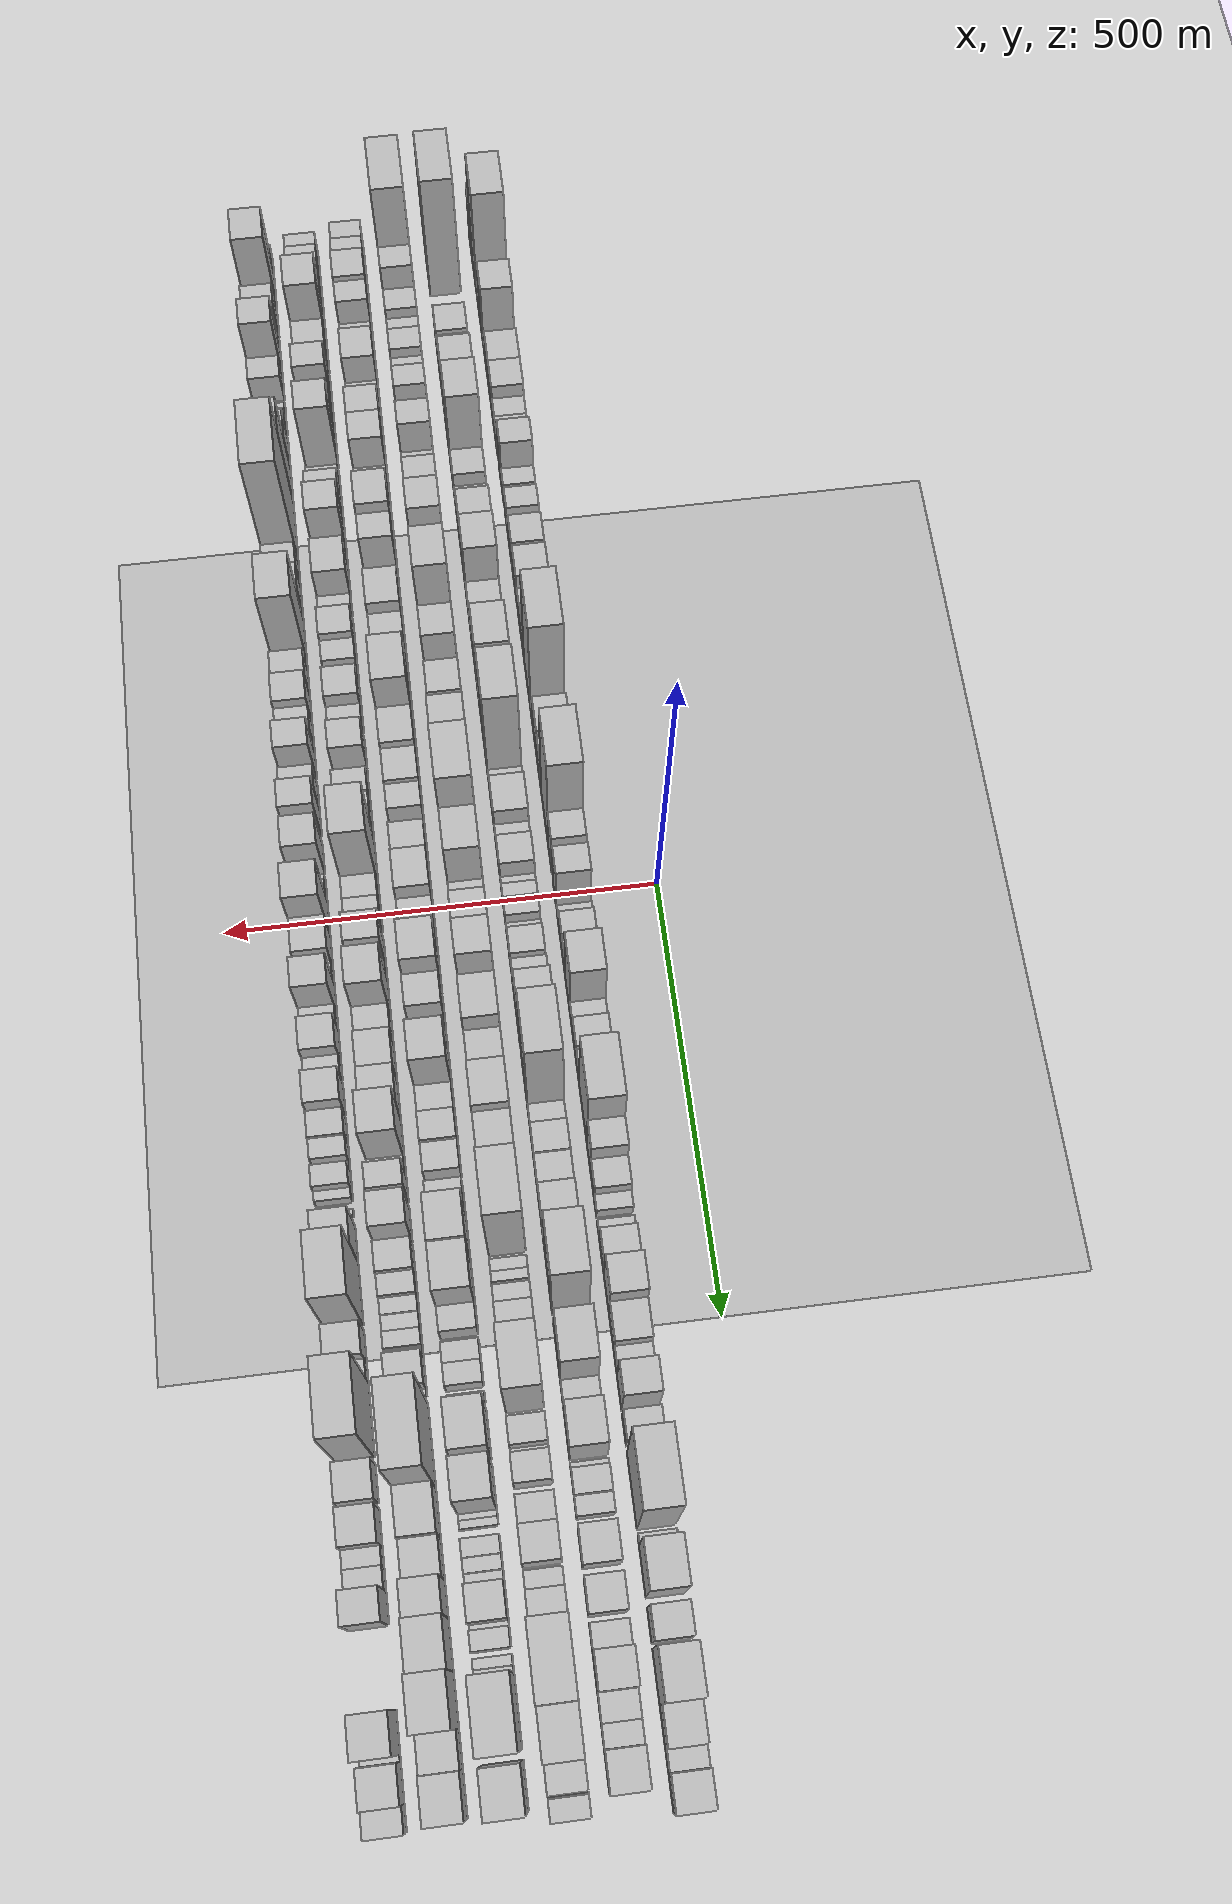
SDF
<?xml version="1.0" encoding="utf-8"?>

<sdf version="1.6">

   <world name="default">

      <gui fullscreen="0">

         <camera name="user_camera">

            <pose>-15 0 4.57585 0 0 0</pose>

            <view_controller>orbit</view_controller>

         </camera>

      </gui>

      <scene>

         <sky>

           <clouds>

             <speed>12</speed>

           </clouds>

         </sky>

         <ambient>0.4 0.4 0.4 1</ambient>

         <background>0.7 0.7 0.7 1</background>

         <shadows>1</shadows>

      </scene>

      <gravity>0 0 -9.8066</gravity>

      <magnetic_field>6e-06 2.3e-05 -4.2e-05</magnetic_field>

      <physics default="0" name="default_physics" type="ode">

         <ode>

            <solver>

               <type>quick</type>

               <iters>10</iters>

               <sor>1.0</sor>

               <use_dynamic_moi_rescaling>0</use_dynamic_moi_rescaling>

            </solver>

            <constraints>

               <cfm>0</cfm>

               <erp>0.2</erp>

               <contact_max_correcting_vel>100</contact_max_correcting_vel>

               <contact_surface_layer>0.001</contact_surface_layer>

            </constraints>

         </ode>

         <max_step_size>0.004</max_step_size>

         <real_time_factor>1</real_time_factor>

         <real_time_update_rate>250</real_time_update_rate>

      </physics>

      <light name="sun" type="directional">

         <cast_shadows>1</cast_shadows>

         <pose>0 0 10 0 0 0</pose>

         <diffuse>0.8 0.8 0.8 1</diffuse>

         <specular>0.2 0.2 0.2 1</specular>

         <attenuation>

            <range>1000</range>

            <constant>0.9</constant>

            <linear>0.01</linear>

            <quadratic>0.001</quadratic>

         </attenuation>

         <direction>-0.5 0.1 -0.9</direction>

      </light>

      <include>

         <name>ground_plane_1</name>

         <uri>model://HANNAS_ground_plane</uri>

         <pose>0 0 0  0 0 0</pose>

      </include>

      <include>

         <name>ground_plane_2</name>

         <uri>model://HANNAS_ground_plane</uri>

         <pose>100 0 0  0 0 0</pose>

      </include>

      <model name="building_1">

         <static>1</static>

         <pose frame="">100.0000 -920.9331 0 0.000000 0.000000 0.000000</pose>

         <link name="link">

            <pose frame="">0 0 54.00 0 0 0</pose>

            <collision name="collision">

               <geometry>

                  <box>

                     <size>40.0000 38.1338 108.0000</size>

                  </box>

               </geometry>

               <max_contacts>10</max_contacts>

               <surface>

                  <contact>

                     <ode/>

                  </contact>

                  <bounce/>

                  <friction>

                     <torsional>

                        <ode/>

                     </torsional>

                     <ode/>

                  </friction>

               </surface>

            </collision>

            <visual name="visual">

               <cast_shadows>0</cast_shadows>

               <geometry>

                  <box>

                     <size>40.0000 38.1338 108.0000</size>

                  </box>

               </geometry>

               <material>

                  <script>

                     <uri>model://HANNAS_wall/materials/scripts</uri>

                     <uri>model://HANNAS_wall/materials/textures</uri>

                     <name>vrc/HANNAS_wall</name>

                  </script>

               </material>

            </visual>

            <self_collide>0</self_collide>

            <enable_wind>0</enable_wind>

            <kinematic>0</kinematic>

         </link>

      </model>

      <model name="building_2">

         <static>1</static>

         <pose frame="">100.0000 -870.1784 0 0.000000 0.000000 0.000000</pose>

         <link name="link">

            <pose frame="">0 0 102.00 0 0 0</pose>

            <collision name="collision">

               <geometry>

                  <box>

                     <size>40.0000 63.3756 204.0000</size>

                  </box>

               </geometry>

               <max_contacts>10</max_contacts>

               <surface>

                  <contact>

                     <ode/>

                  </contact>

                  <bounce/>

                  <friction>

                     <torsional>

                        <ode/>

                     </torsional>

                     <ode/>

                  </friction>

               </surface>

            </collision>

            <visual name="visual">

               <cast_shadows>0</cast_shadows>

               <geometry>

                  <box>

                     <size>40.0000 63.3756 204.0000</size>

                  </box>

               </geometry>

               <material>

                  <script>

                     <uri>model://HANNAS_wall/materials/scripts</uri>

                     <uri>model://HANNAS_wall/materials/textures</uri>

                     <name>vrc/HANNAS_wall</name>

                  </script>

               </material>

            </visual>

            <self_collide>0</self_collide>

            <enable_wind>0</enable_wind>

            <kinematic>0</kinematic>

         </link>

      </model>

      <model name="building_3">

         <static>1</static>

         <pose frame="">100.0000 -817.4583 0 0.000000 0.000000 0.000000</pose>

         <link name="link">

            <pose frame="">0 0 25.50 0 0 0</pose>

            <collision name="collision">

               <geometry>

                  <box>

                     <size>40.0000 26.0645 51.0000</size>

                  </box>

               </geometry>

               <max_contacts>10</max_contacts>

               <surface>

                  <contact>

                     <ode/>

                  </contact>

                  <bounce/>

                  <friction>

                     <torsional>

                        <ode/>

                     </torsional>

                     <ode/>

                  </friction>

               </surface>

            </collision>

            <visual name="visual">

               <cast_shadows>0</cast_shadows>

               <geometry>

                  <box>

                     <size>40.0000 26.0645 51.0000</size>

                  </box>

               </geometry>

               <material>

                  <script>

                     <uri>model://HANNAS_wall/materials/scripts</uri>

                     <uri>model://HANNAS_wall/materials/textures</uri>

                     <name>vrc/HANNAS_wall</name>

                  </script>

               </material>

            </visual>

            <self_collide>0</self_collide>

            <enable_wind>0</enable_wind>

            <kinematic>0</kinematic>

         </link>

      </model>

      <model name="building_4">

         <static>1</static>

         <pose frame="">100.0000 -783.0967 0 0.000000 0.000000 0.000000</pose>

         <link name="link">

            <pose frame="">0 0 61.50 0 0 0</pose>

            <collision name="collision">

               <geometry>

                  <box>

                     <size>40.0000 42.6586 123.0000</size>

                  </box>

               </geometry>

               <max_contacts>10</max_contacts>

               <surface>

                  <contact>

                     <ode/>

                  </contact>

                  <bounce/>

                  <friction>

                     <torsional>

                        <ode/>

                     </torsional>

                     <ode/>

                  </friction>

               </surface>

            </collision>

            <visual name="visual">

               <cast_shadows>0</cast_shadows>

               <geometry>

                  <box>

                     <size>40.0000 42.6586 123.0000</size>

                  </box>

               </geometry>

               <material>

                  <script>

                     <uri>model://HANNAS_wall/materials/scripts</uri>

                     <uri>model://HANNAS_wall/materials/textures</uri>

                     <name>vrc/HANNAS_wall</name>

                  </script>

               </material>

            </visual>

            <self_collide>0</self_collide>

            <enable_wind>0</enable_wind>

            <kinematic>0</kinematic>

         </link>

      </model>

      <model name="building_5">

         <static>1</static>

         <pose frame="">100.0000 -746.5568 0 0.000000 0.000000 0.000000</pose>

         <link name="link">

            <pose frame="">0 0 19.50 0 0 0</pose>

            <collision name="collision">

               <geometry>

                  <box>

                     <size>40.0000 22.4212 39.0000</size>

                  </box>

               </geometry>

               <max_contacts>10</max_contacts>

               <surface>

                  <contact>

                     <ode/>

                  </contact>

                  <bounce/>

                  <friction>

                     <torsional>

                        <ode/>

                     </torsional>

                     <ode/>

                  </friction>

               </surface>

            </collision>

            <visual name="visual">

               <cast_shadows>0</cast_shadows>

               <geometry>

                  <box>

                     <size>40.0000 22.4212 39.0000</size>

                  </box>

               </geometry>

               <material>

                  <script>

                     <uri>model://HANNAS_wall/materials/scripts</uri>

                     <uri>model://HANNAS_wall/materials/textures</uri>

                     <name>vrc/HANNAS_wall</name>

                  </script>

               </material>

            </visual>

            <self_collide>0</self_collide>

            <enable_wind>0</enable_wind>

            <kinematic>0</kinematic>

         </link>

      </model>

      <model name="building_6">

         <static>1</static>

         <pose frame="">100.0000 -713.4626 0 0.000000 0.000000 0.000000</pose>

         <link name="link">

            <pose frame="">0 0 37.50 0 0 0</pose>

            <collision name="collision">

               <geometry>

                  <box>

                     <size>40.0000 43.7672 75.0000</size>

                  </box>

               </geometry>

               <max_contacts>10</max_contacts>

               <surface>

                  <contact>

                     <ode/>

                  </contact>

                  <bounce/>

                  <friction>

                     <torsional>

                        <ode/>

                     </torsional>

                     <ode/>

                  </friction>

               </surface>

            </collision>

            <visual name="visual">

               <cast_shadows>0</cast_shadows>

               <geometry>

                  <box>

                     <size>40.0000 43.7672 75.0000</size>

                  </box>

               </geometry>

               <material>

                  <script>

                     <uri>model://HANNAS_wall/materials/scripts</uri>

                     <uri>model://HANNAS_wall/materials/textures</uri>

                     <name>vrc/HANNAS_wall</name>

                  </script>

               </material>

            </visual>

            <self_collide>0</self_collide>

            <enable_wind>0</enable_wind>

            <kinematic>0</kinematic>

         </link>

      </model>

      <model name="building_7">

         <static>1</static>

         <pose frame="">100.0000 -671.6099 0 0.000000 0.000000 0.000000</pose>

         <link name="link">

            <pose frame="">0 0 37.50 0 0 0</pose>

            <collision name="collision">

               <geometry>

                  <box>

                     <size>40.0000 39.9382 75.0000</size>

                  </box>

               </geometry>

               <max_contacts>10</max_contacts>

               <surface>

                  <contact>

                     <ode/>

                  </contact>

                  <bounce/>

                  <friction>

                     <torsional>

                        <ode/>

                     </torsional>

                     <ode/>

                  </friction>

               </surface>

            </collision>

            <visual name="visual">

               <cast_shadows>0</cast_shadows>

               <geometry>

                  <box>

                     <size>40.0000 39.9382 75.0000</size>

                  </box>

               </geometry>

               <material>

                  <script>

                     <uri>model://HANNAS_wall/materials/scripts</uri>

                     <uri>model://HANNAS_wall/materials/textures</uri>

                     <name>vrc/HANNAS_wall</name>

                  </script>

               </material>

            </visual>

            <self_collide>0</self_collide>

            <enable_wind>0</enable_wind>

            <kinematic>0</kinematic>

         </link>

      </model>

      <model name="building_8">

         <static>1</static>

         <pose frame="">100.0000 -638.3373 0 0.000000 0.000000 0.000000</pose>

         <link name="link">

            <pose frame="">0 0 25.50 0 0 0</pose>

            <collision name="collision">

               <geometry>

                  <box>

                     <size>40.0000 26.6069 51.0000</size>

                  </box>

               </geometry>

               <max_contacts>10</max_contacts>

               <surface>

                  <contact>

                     <ode/>

                  </contact>

                  <bounce/>

                  <friction>

                     <torsional>

                        <ode/>

                     </torsional>

                     <ode/>

                  </friction>

               </surface>

            </collision>

            <visual name="visual">

               <cast_shadows>0</cast_shadows>

               <geometry>

                  <box>

                     <size>40.0000 26.6069 51.0000</size>

                  </box>

               </geometry>

               <material>

                  <script>

                     <uri>model://HANNAS_wall/materials/scripts</uri>

                     <uri>model://HANNAS_wall/materials/textures</uri>

                     <name>vrc/HANNAS_wall</name>

                  </script>

               </material>

            </visual>

            <self_collide>0</self_collide>

            <enable_wind>0</enable_wind>

            <kinematic>0</kinematic>

         </link>

      </model>

      <model name="building_9">

         <static>1</static>

         <pose frame="">100.0000 -609.8108 0 0.000000 0.000000 0.000000</pose>

         <link name="link">

            <pose frame="">0 0 25.50 0 0 0</pose>

            <collision name="collision">

               <geometry>

                  <box>

                     <size>40.0000 30.4461 51.0000</size>

                  </box>

               </geometry>

               <max_contacts>10</max_contacts>

               <surface>

                  <contact>

                     <ode/>

                  </contact>

                  <bounce/>

                  <friction>

                     <torsional>

                        <ode/>

                     </torsional>

                     <ode/>

                  </friction>

               </surface>

            </collision>

            <visual name="visual">

               <cast_shadows>0</cast_shadows>

               <geometry>

                  <box>

                     <size>40.0000 30.4461 51.0000</size>

                  </box>

               </geometry>

               <material>

                  <script>

                     <uri>model://HANNAS_wall/materials/scripts</uri>

                     <uri>model://HANNAS_wall/materials/textures</uri>

                     <name>vrc/HANNAS_wall</name>

                  </script>

               </material>

            </visual>

            <self_collide>0</self_collide>

            <enable_wind>0</enable_wind>

            <kinematic>0</kinematic>

         </link>

      </model>

      <model name="building_10">

         <static>1</static>

         <pose frame="">100.0000 -567.5754 0 0.000000 0.000000 0.000000</pose>

         <link name="link">

            <pose frame="">0 0 51.00 0 0 0</pose>

            <collision name="collision">

               <geometry>

                  <box>

                     <size>40.0000 34.0247 102.0000</size>

                  </box>

               </geometry>

               <max_contacts>10</max_contacts>

               <surface>

                  <contact>

                     <ode/>

                  </contact>

                  <bounce/>

                  <friction>

                     <torsional>

                        <ode/>

                     </torsional>

                     <ode/>

                  </friction>

               </surface>

            </collision>

            <visual name="visual">

               <cast_shadows>0</cast_shadows>

               <geometry>

                  <box>

                     <size>40.0000 34.0247 102.0000</size>

                  </box>

               </geometry>

               <material>

                  <script>

                     <uri>model://HANNAS_wall/materials/scripts</uri>

                     <uri>model://HANNAS_wall/materials/textures</uri>

                     <name>vrc/HANNAS_wall</name>

                  </script>

               </material>

            </visual>

            <self_collide>0</self_collide>

            <enable_wind>0</enable_wind>

            <kinematic>0</kinematic>

         </link>

      </model>

      <model name="building_11">

         <static>1</static>

         <pose frame="">100.0000 -538.4592 0 0.000000 0.000000 0.000000</pose>

         <link name="link">

            <pose frame="">0 0 24.00 0 0 0</pose>

            <collision name="collision">

               <geometry>

                  <box>

                     <size>40.0000 24.2077 48.0000</size>

                  </box>

               </geometry>

               <max_contacts>10</max_contacts>

               <surface>

                  <contact>

                     <ode/>

                  </contact>

                  <bounce/>

                  <friction>

                     <torsional>

                        <ode/>

                     </torsional>

                     <ode/>

                  </friction>

               </surface>

            </collision>

            <visual name="visual">

               <cast_shadows>0</cast_shadows>

               <geometry>

                  <box>

                     <size>40.0000 24.2077 48.0000</size>

                  </box>

               </geometry>

               <material>

                  <script>

                     <uri>model://HANNAS_wall/materials/scripts</uri>

                     <uri>model://HANNAS_wall/materials/textures</uri>

                     <name>vrc/HANNAS_wall</name>

                  </script>

               </material>

            </visual>

            <self_collide>0</self_collide>

            <enable_wind>0</enable_wind>

            <kinematic>0</kinematic>

         </link>

      </model>

      <model name="building_12">

         <static>1</static>

         <pose frame="">100.0000 -504.6289 0 0.000000 0.000000 0.000000</pose>

         <link name="link">

            <pose frame="">0 0 27.00 0 0 0</pose>

            <collision name="collision">

               <geometry>

                  <box>

                     <size>40.0000 29.4530 54.0000</size>

                  </box>

               </geometry>

               <max_contacts>10</max_contacts>

               <surface>

                  <contact>

                     <ode/>

                  </contact>

                  <bounce/>

                  <friction>

                     <torsional>

                        <ode/>

                     </torsional>

                     <ode/>

                  </friction>

               </surface>

            </collision>

            <visual name="visual">

               <cast_shadows>0</cast_shadows>

               <geometry>

                  <box>

                     <size>40.0000 29.4530 54.0000</size>

                  </box>

               </geometry>

               <material>

                  <script>

                     <uri>model://HANNAS_wall/materials/scripts</uri>

                     <uri>model://HANNAS_wall/materials/textures</uri>

                     <name>vrc/HANNAS_wall</name>

                  </script>

               </material>

            </visual>

            <self_collide>0</self_collide>

            <enable_wind>0</enable_wind>

            <kinematic>0</kinematic>

         </link>

      </model>

      <model name="building_13">

         <static>1</static>

         <pose frame="">100.0000 -481.1156 0 0.000000 0.000000 0.000000</pose>

         <link name="link">

            <pose frame="">0 0 15.00 0 0 0</pose>

            <collision name="collision">

               <geometry>

                  <box>

                     <size>40.0000 17.5735 30.0000</size>

                  </box>

               </geometry>

               <max_contacts>10</max_contacts>

               <surface>

                  <contact>

                     <ode/>

                  </contact>

                  <bounce/>

                  <friction>

                     <torsional>

                        <ode/>

                     </torsional>

                     <ode/>

                  </friction>

               </surface>

            </collision>

            <visual name="visual">

               <cast_shadows>0</cast_shadows>

               <geometry>

                  <box>

                     <size>40.0000 17.5735 30.0000</size>

                  </box>

               </geometry>

               <material>

                  <script>

                     <uri>model://HANNAS_wall/materials/scripts</uri>

                     <uri>model://HANNAS_wall/materials/textures</uri>

                     <name>vrc/HANNAS_wall</name>

                  </script>

               </material>

            </visual>

            <self_collide>0</self_collide>

            <enable_wind>0</enable_wind>

            <kinematic>0</kinematic>

         </link>

      </model>

      <model name="building_14">

         <static>1</static>

         <pose frame="">100.0000 -452.6875 0 0.000000 0.000000 0.000000</pose>

         <link name="link">

            <pose frame="">0 0 33.00 0 0 0</pose>

            <collision name="collision">

               <geometry>

                  <box>

                     <size>40.0000 39.2828 66.0000</size>

                  </box>

               </geometry>

               <max_contacts>10</max_contacts>

               <surface>

                  <contact>

                     <ode/>

                  </contact>

                  <bounce/>

                  <friction>

                     <torsional>

                        <ode/>

                     </torsional>

                     <ode/>

                  </friction>

               </surface>

            </collision>

            <visual name="visual">

               <cast_shadows>0</cast_shadows>

               <geometry>

                  <box>

                     <size>40.0000 39.2828 66.0000</size>

                  </box>

               </geometry>

               <material>

                  <script>

                     <uri>model://HANNAS_wall/materials/scripts</uri>

                     <uri>model://HANNAS_wall/materials/textures</uri>

                     <name>vrc/HANNAS_wall</name>

                  </script>

               </material>

            </visual>

            <self_collide>0</self_collide>

            <enable_wind>0</enable_wind>

            <kinematic>0</kinematic>

         </link>

      </model>

      <model name="building_15">

         <static>1</static>

         <pose frame="">100.0000 -404.6036 0 0.000000 0.000000 0.000000</pose>

         <link name="link">

            <pose frame="">0 0 36.00 0 0 0</pose>

            <collision name="collision">

               <geometry>

                  <box>

                     <size>40.0000 42.8849 72.0000</size>

                  </box>

               </geometry>

               <max_contacts>10</max_contacts>

               <surface>

                  <contact>

                     <ode/>

                  </contact>

                  <bounce/>

                  <friction>

                     <torsional>

                        <ode/>

                     </torsional>

                     <ode/>

                  </friction>

               </surface>

            </collision>

            <visual name="visual">

               <cast_shadows>0</cast_shadows>

               <geometry>

                  <box>

                     <size>40.0000 42.8849 72.0000</size>

                  </box>

               </geometry>

               <material>

                  <script>

                     <uri>model://HANNAS_wall/materials/scripts</uri>

                     <uri>model://HANNAS_wall/materials/textures</uri>

                     <name>vrc/HANNAS_wall</name>

                  </script>

               </material>

            </visual>

            <self_collide>0</self_collide>

            <enable_wind>0</enable_wind>

            <kinematic>0</kinematic>

         </link>

      </model>

      <model name="building_16">

         <static>1</static>

         <pose frame="">100.0000 -362.6627 0 0.000000 0.000000 0.000000</pose>

         <link name="link">

            <pose frame="">0 0 27.00 0 0 0</pose>

            <collision name="collision">

               <geometry>

                  <box>

                     <size>40.0000 28.9970 54.0000</size>

                  </box>

               </geometry>

               <max_contacts>10</max_contacts>

               <surface>

                  <contact>

                     <ode/>

                  </contact>

                  <bounce/>

                  <friction>

                     <torsional>

                        <ode/>

                     </torsional>

                     <ode/>

                  </friction>

               </surface>

            </collision>

            <visual name="visual">

               <cast_shadows>0</cast_shadows>

               <geometry>

                  <box>

                     <size>40.0000 28.9970 54.0000</size>

                  </box>

               </geometry>

               <material>

                  <script>

                     <uri>model://HANNAS_wall/materials/scripts</uri>

                     <uri>model://HANNAS_wall/materials/textures</uri>

                     <name>vrc/HANNAS_wall</name>

                  </script>

               </material>

            </visual>

            <self_collide>0</self_collide>

            <enable_wind>0</enable_wind>

            <kinematic>0</kinematic>

         </link>

      </model>

      <model name="building_17">

         <static>1</static>

         <pose frame="">100.0000 -329.0223 0 0.000000 0.000000 0.000000</pose>

         <link name="link">

            <pose frame="">0 0 34.50 0 0 0</pose>

            <collision name="collision">

               <geometry>

                  <box>

                     <size>40.0000 38.2836 69.0000</size>

                  </box>

               </geometry>

               <max_contacts>10</max_contacts>

               <surface>

                  <contact>

                     <ode/>

                  </contact>

                  <bounce/>

                  <friction>

                     <torsional>

                        <ode/>

                     </torsional>

                     <ode/>

                  </friction>

               </surface>

            </collision>

            <visual name="visual">

               <cast_shadows>0</cast_shadows>

               <geometry>

                  <box>

                     <size>40.0000 38.2836 69.0000</size>

                  </box>

               </geometry>

               <material>

                  <script>

                     <uri>model://HANNAS_wall/materials/scripts</uri>

                     <uri>model://HANNAS_wall/materials/textures</uri>

                     <name>vrc/HANNAS_wall</name>

                  </script>

               </material>

            </visual>

            <self_collide>0</self_collide>

            <enable_wind>0</enable_wind>

            <kinematic>0</kinematic>

         </link>

      </model>

      <model name="building_18">

         <static>1</static>

         <pose frame="">100.0000 -272.8453 0 0.000000 0.000000 0.000000</pose>

         <link name="link">

            <pose frame="">0 0 105.00 0 0 0</pose>

            <collision name="collision">

               <geometry>

                  <box>

                     <size>40.0000 74.0705 210.0000</size>

                  </box>

               </geometry>

               <max_contacts>10</max_contacts>

               <surface>

                  <contact>

                     <ode/>

                  </contact>

                  <bounce/>

                  <friction>

                     <torsional>

                        <ode/>

                     </torsional>

                     <ode/>

                  </friction>

               </surface>

            </collision>

            <visual name="visual">

               <cast_shadows>0</cast_shadows>

               <geometry>

                  <box>

                     <size>40.0000 74.0705 210.0000</size>

                  </box>

               </geometry>

               <material>

                  <script>

                     <uri>model://HANNAS_wall/materials/scripts</uri>

                     <uri>model://HANNAS_wall/materials/textures</uri>

                     <name>vrc/HANNAS_wall</name>

                  </script>

               </material>

            </visual>

            <self_collide>0</self_collide>

            <enable_wind>0</enable_wind>

            <kinematic>0</kinematic>

         </link>

      </model>

      <model name="building_19">

         <static>1</static>

         <pose frame="">100.0000 -226.6563 0 0.000000 0.000000 0.000000</pose>

         <link name="link">

            <pose frame="">0 0 16.50 0 0 0</pose>

            <collision name="collision">

               <geometry>

                  <box>

                     <size>40.0000 18.3076 33.0000</size>

                  </box>

               </geometry>

               <max_contacts>10</max_contacts>

               <surface>

                  <contact>

                     <ode/>

                  </contact>

                  <bounce/>

                  <friction>

                     <torsional>

                        <ode/>

                     </torsional>

                     <ode/>

                  </friction>

               </surface>

            </collision>

            <visual name="visual">

               <cast_shadows>0</cast_shadows>

               <geometry>

                  <box>

                     <size>40.0000 18.3076 33.0000</size>

                  </box>

               </geometry>

               <material>

                  <script>

                     <uri>model://HANNAS_wall/materials/scripts</uri>

                     <uri>model://HANNAS_wall/materials/textures</uri>

                     <name>vrc/HANNAS_wall</name>

                  </script>

               </material>

            </visual>

            <self_collide>0</self_collide>

            <enable_wind>0</enable_wind>

            <kinematic>0</kinematic>

         </link>

      </model>

      <model name="building_20">

         <static>1</static>

         <pose frame="">100.0000 -195.0285 0 0.000000 0.000000 0.000000</pose>

         <link name="link">

            <pose frame="">0 0 40.50 0 0 0</pose>

            <collision name="collision">

               <geometry>

                  <box>

                     <size>40.0000 44.9481 81.0000</size>

                  </box>

               </geometry>

               <max_contacts>10</max_contacts>

               <surface>

                  <contact>

                     <ode/>

                  </contact>

                  <bounce/>

                  <friction>

                     <torsional>

                        <ode/>

                     </torsional>

                     <ode/>

                  </friction>

               </surface>

            </collision>

            <visual name="visual">

               <cast_shadows>0</cast_shadows>

               <geometry>

                  <box>

                     <size>40.0000 44.9481 81.0000</size>

                  </box>

               </geometry>

               <material>

                  <script>

                     <uri>model://HANNAS_wall/materials/scripts</uri>

                     <uri>model://HANNAS_wall/materials/textures</uri>

                     <name>vrc/HANNAS_wall</name>

                  </script>

               </material>

            </visual>

            <self_collide>0</self_collide>

            <enable_wind>0</enable_wind>

            <kinematic>0</kinematic>

         </link>

      </model>

      <model name="building_21">

         <static>1</static>

         <pose frame="">100.0000 -154.0968 0 0.000000 0.000000 0.000000</pose>

         <link name="link">

            <pose frame="">0 0 36.00 0 0 0</pose>

            <collision name="collision">

               <geometry>

                  <box>

                     <size>40.0000 36.9153 72.0000</size>

                  </box>

               </geometry>

               <max_contacts>10</max_contacts>

               <surface>

                  <contact>

                     <ode/>

                  </contact>

                  <bounce/>

                  <friction>

                     <torsional>

                        <ode/>

                     </torsional>

                     <ode/>

                  </friction>

               </surface>

            </collision>

            <visual name="visual">

               <cast_shadows>0</cast_shadows>

               <geometry>

                  <box>

                     <size>40.0000 36.9153 72.0000</size>

                  </box>

               </geometry>

               <material>

                  <script>

                     <uri>model://HANNAS_wall/materials/scripts</uri>

                     <uri>model://HANNAS_wall/materials/textures</uri>

                     <name>vrc/HANNAS_wall</name>

                  </script>

               </material>

            </visual>

            <self_collide>0</self_collide>

            <enable_wind>0</enable_wind>

            <kinematic>0</kinematic>

         </link>

      </model>

      <model name="building_22">

         <static>1</static>

         <pose frame="">100.0000 -95.8828 0 0.000000 0.000000 0.000000</pose>

         <link name="link">

            <pose frame="">0 0 111.00 0 0 0</pose>

            <collision name="collision">

               <geometry>

                  <box>

                     <size>40.0000 69.5129 222.0000</size>

                  </box>

               </geometry>

               <max_contacts>10</max_contacts>

               <surface>

                  <contact>

                     <ode/>

                  </contact>

                  <bounce/>

                  <friction>

                     <torsional>

                        <ode/>

                     </torsional>

                     <ode/>

                  </friction>

               </surface>

            </collision>

            <visual name="visual">

               <cast_shadows>0</cast_shadows>

               <geometry>

                  <box>

                     <size>40.0000 69.5129 222.0000</size>

                  </box>

               </geometry>

               <material>

                  <script>

                     <uri>model://HANNAS_wall/materials/scripts</uri>

                     <uri>model://HANNAS_wall/materials/textures</uri>

                     <name>vrc/HANNAS_wall</name>

                  </script>

               </material>

            </visual>

            <self_collide>0</self_collide>

            <enable_wind>0</enable_wind>

            <kinematic>0</kinematic>

         </link>

      </model>

      <model name="building_23">

         <static>1</static>

         <pose frame="">100.0000 -44.6378 0 0.000000 0.000000 0.000000</pose>

         <link name="link">

            <pose frame="">0 0 51.00 0 0 0</pose>

            <collision name="collision">

               <geometry>

                  <box>

                     <size>40.0000 32.9771 102.0000</size>

                  </box>

               </geometry>

               <max_contacts>10</max_contacts>

               <surface>

                  <contact>

                     <ode/>

                  </contact>

                  <bounce/>

                  <friction>

                     <torsional>

                        <ode/>

                     </torsional>

                     <ode/>

                  </friction>

               </surface>

            </collision>

            <visual name="visual">

               <cast_shadows>0</cast_shadows>

               <geometry>

                  <box>

                     <size>40.0000 32.9771 102.0000</size>

                  </box>

               </geometry>

               <material>

                  <script>

                     <uri>model://HANNAS_wall/materials/scripts</uri>

                     <uri>model://HANNAS_wall/materials/textures</uri>

                     <name>vrc/HANNAS_wall</name>

                  </script>

               </material>

            </visual>

            <self_collide>0</self_collide>

            <enable_wind>0</enable_wind>

            <kinematic>0</kinematic>

         </link>

      </model>

      <model name="building_24">

         <static>1</static>

         <pose frame="">100.0000 -1.5808 0 0.000000 0.000000 0.000000</pose>

         <link name="link">

            <pose frame="">0 0 52.50 0 0 0</pose>

            <collision name="collision">

               <geometry>

                  <box>

                     <size>40.0000 33.1368 105.0000</size>

                  </box>

               </geometry>

               <max_contacts>10</max_contacts>

               <surface>

                  <contact>

                     <ode/>

                  </contact>

                  <bounce/>

                  <friction>

                     <torsional>

                        <ode/>

                     </torsional>

                     <ode/>

                  </friction>

               </surface>

            </collision>

            <visual name="visual">

               <cast_shadows>0</cast_shadows>

               <geometry>

                  <box>

                     <size>40.0000 33.1368 105.0000</size>

                  </box>

               </geometry>

               <material>

                  <script>

                     <uri>model://HANNAS_wall/materials/scripts</uri>

                     <uri>model://HANNAS_wall/materials/textures</uri>

                     <name>vrc/HANNAS_wall</name>

                  </script>

               </material>

            </visual>

            <self_collide>0</self_collide>

            <enable_wind>0</enable_wind>

            <kinematic>0</kinematic>

         </link>

      </model>

      <model name="building_25">

         <static>1</static>

         <pose frame="">100.0000 31.3695 0 0.000000 0.000000 0.000000</pose>

         <link name="link">

            <pose frame="">0 0 15.00 0 0 0</pose>

            <collision name="collision">

               <geometry>

                  <box>

                     <size>40.0000 16.7637 30.0000</size>

                  </box>

               </geometry>

               <max_contacts>10</max_contacts>

               <surface>

                  <contact>

                     <ode/>

                  </contact>

                  <bounce/>

                  <friction>

                     <torsional>

                        <ode/>

                     </torsional>

                     <ode/>

                  </friction>

               </surface>

            </collision>

            <visual name="visual">

               <cast_shadows>0</cast_shadows>

               <geometry>

                  <box>

                     <size>40.0000 16.7637 30.0000</size>

                  </box>

               </geometry>

               <material>

                  <script>

                     <uri>model://HANNAS_wall/materials/scripts</uri>

                     <uri>model://HANNAS_wall/materials/textures</uri>

                     <name>vrc/HANNAS_wall</name>

                  </script>

               </material>

            </visual>

            <self_collide>0</self_collide>

            <enable_wind>0</enable_wind>

            <kinematic>0</kinematic>

         </link>

      </model>

      <model name="building_26">

         <static>1</static>

         <pose frame="">100.0000 53.5185 0 0.000000 0.000000 0.000000</pose>

         <link name="link">

            <pose frame="">0 0 27.00 0 0 0</pose>

            <collision name="collision">

               <geometry>

                  <box>

                     <size>40.0000 27.5342 54.0000</size>

                  </box>

               </geometry>

               <max_contacts>10</max_contacts>

               <surface>

                  <contact>

                     <ode/>

                  </contact>

                  <bounce/>

                  <friction>

                     <torsional>

                        <ode/>

                     </torsional>

                     <ode/>

                  </friction>

               </surface>

            </collision>

            <visual name="visual">

               <cast_shadows>0</cast_shadows>

               <geometry>

                  <box>

                     <size>40.0000 27.5342 54.0000</size>

                  </box>

               </geometry>

               <material>

                  <script>

                     <uri>model://HANNAS_wall/materials/scripts</uri>

                     <uri>model://HANNAS_wall/materials/textures</uri>

                     <name>vrc/HANNAS_wall</name>

                  </script>

               </material>

            </visual>

            <self_collide>0</self_collide>

            <enable_wind>0</enable_wind>

            <kinematic>0</kinematic>

         </link>

      </model>

      <model name="building_27">

         <static>1</static>

         <pose frame="">100.0000 81.8426 0 0.000000 0.000000 0.000000</pose>

         <link name="link">

            <pose frame="">0 0 25.50 0 0 0</pose>

            <collision name="collision">

               <geometry>

                  <box>

                     <size>40.0000 29.1141 51.0000</size>

                  </box>

               </geometry>

               <max_contacts>10</max_contacts>

               <surface>

                  <contact>

                     <ode/>

                  </contact>

                  <bounce/>

                  <friction>

                     <torsional>

                        <ode/>

                     </torsional>

                     <ode/>

                  </friction>

               </surface>

            </collision>

            <visual name="visual">

               <cast_shadows>0</cast_shadows>

               <geometry>

                  <box>

                     <size>40.0000 29.1141 51.0000</size>

                  </box>

               </geometry>

               <material>

                  <script>

                     <uri>model://HANNAS_wall/materials/scripts</uri>

                     <uri>model://HANNAS_wall/materials/textures</uri>

                     <name>vrc/HANNAS_wall</name>

                  </script>

               </material>

            </visual>

            <self_collide>0</self_collide>

            <enable_wind>0</enable_wind>

            <kinematic>0</kinematic>

         </link>

      </model>

      <model name="building_28">

         <static>1</static>

         <pose frame="">100.0000 120.0571 0 0.000000 0.000000 0.000000</pose>

         <link name="link">

            <pose frame="">0 0 69.00 0 0 0</pose>

            <collision name="collision">

               <geometry>

                  <box>

                     <size>40.0000 47.3147 138.0000</size>

                  </box>

               </geometry>

               <max_contacts>10</max_contacts>

               <surface>

                  <contact>

                     <ode/>

                  </contact>

                  <bounce/>

                  <friction>

                     <torsional>

                        <ode/>

                     </torsional>

                     <ode/>

                  </friction>

               </surface>

            </collision>

            <visual name="visual">

               <cast_shadows>0</cast_shadows>

               <geometry>

                  <box>

                     <size>40.0000 47.3147 138.0000</size>

                  </box>

               </geometry>

               <material>

                  <script>

                     <uri>model://HANNAS_wall/materials/scripts</uri>

                     <uri>model://HANNAS_wall/materials/textures</uri>

                     <name>vrc/HANNAS_wall</name>

                  </script>

               </material>

            </visual>

            <self_collide>0</self_collide>

            <enable_wind>0</enable_wind>

            <kinematic>0</kinematic>

         </link>

      </model>

      <model name="building_29">

         <static>1</static>

         <pose frame="">100.0000 154.8591 0 0.000000 0.000000 0.000000</pose>

         <link name="link">

            <pose frame="">0 0 21.00 0 0 0</pose>

            <collision name="collision">

               <geometry>

                  <box>

                     <size>40.0000 22.2893 42.0000</size>

                  </box>

               </geometry>

               <max_contacts>10</max_contacts>

               <surface>

                  <contact>

                     <ode/>

                  </contact>

                  <bounce/>

                  <friction>

                     <torsional>

                        <ode/>

                     </torsional>

                     <ode/>

                  </friction>

               </surface>

            </collision>

            <visual name="visual">

               <cast_shadows>0</cast_shadows>

               <geometry>

                  <box>

                     <size>40.0000 22.2893 42.0000</size>

                  </box>

               </geometry>

               <material>

                  <script>

                     <uri>model://HANNAS_wall/materials/scripts</uri>

                     <uri>model://HANNAS_wall/materials/textures</uri>

                     <name>vrc/HANNAS_wall</name>

                  </script>

               </material>

            </visual>

            <self_collide>0</self_collide>

            <enable_wind>0</enable_wind>

            <kinematic>0</kinematic>

         </link>

      </model>

      <model name="building_30">

         <static>1</static>

         <pose frame="">100.0000 183.0013 0 0.000000 0.000000 0.000000</pose>

         <link name="link">

            <pose frame="">0 0 28.50 0 0 0</pose>

            <collision name="collision">

               <geometry>

                  <box>

                     <size>40.0000 33.9953 57.0000</size>

                  </box>

               </geometry>

               <max_contacts>10</max_contacts>

               <surface>

                  <contact>

                     <ode/>

                  </contact>

                  <bounce/>

                  <friction>

                     <torsional>

                        <ode/>

                     </torsional>

                     <ode/>

                  </friction>

               </surface>

            </collision>

            <visual name="visual">

               <cast_shadows>0</cast_shadows>

               <geometry>

                  <box>

                     <size>40.0000 33.9953 57.0000</size>

                  </box>

               </geometry>

               <material>

                  <script>

                     <uri>model://HANNAS_wall/materials/scripts</uri>

                     <uri>model://HANNAS_wall/materials/textures</uri>

                     <name>vrc/HANNAS_wall</name>

                  </script>

               </material>

            </visual>

            <self_collide>0</self_collide>

            <enable_wind>0</enable_wind>

            <kinematic>0</kinematic>

         </link>

      </model>

      <model name="building_31">

         <static>1</static>

         <pose frame="">100.0000 212.3279 0 0.000000 0.000000 0.000000</pose>

         <link name="link">

            <pose frame="">0 0 24.00 0 0 0</pose>

            <collision name="collision">

               <geometry>

                  <box>

                     <size>40.0000 24.6578 48.0000</size>

                  </box>

               </geometry>

               <max_contacts>10</max_contacts>

               <surface>

                  <contact>

                     <ode/>

                  </contact>

                  <bounce/>

                  <friction>

                     <torsional>

                        <ode/>

                     </torsional>

                     <ode/>

                  </friction>

               </surface>

            </collision>

            <visual name="visual">

               <cast_shadows>0</cast_shadows>

               <geometry>

                  <box>

                     <size>40.0000 24.6578 48.0000</size>

                  </box>

               </geometry>

               <material>

                  <script>

                     <uri>model://HANNAS_wall/materials/scripts</uri>

                     <uri>model://HANNAS_wall/materials/textures</uri>

                     <name>vrc/HANNAS_wall</name>

                  </script>

               </material>

            </visual>

            <self_collide>0</self_collide>

            <enable_wind>0</enable_wind>

            <kinematic>0</kinematic>

         </link>

      </model>

      <model name="building_32">

         <static>1</static>

         <pose frame="">100.0000 261.7838 0 0.000000 0.000000 0.000000</pose>

         <link name="link">

            <pose frame="">0 0 90.00 0 0 0</pose>

            <collision name="collision">

               <geometry>

                  <box>

                     <size>40.0000 68.2540 180.0000</size>

                  </box>

               </geometry>

               <max_contacts>10</max_contacts>

               <surface>

                  <contact>

                     <ode/>

                  </contact>

                  <bounce/>

                  <friction>

                     <torsional>

                        <ode/>

                     </torsional>

                     <ode/>

                  </friction>

               </surface>

            </collision>

            <visual name="visual">

               <cast_shadows>0</cast_shadows>

               <geometry>

                  <box>

                     <size>40.0000 68.2540 180.0000</size>

                  </box>

               </geometry>

               <material>

                  <script>

                     <uri>model://HANNAS_wall/materials/scripts</uri>

                     <uri>model://HANNAS_wall/materials/textures</uri>

                     <name>vrc/HANNAS_wall</name>

                  </script>

               </material>

            </visual>

            <self_collide>0</self_collide>

            <enable_wind>0</enable_wind>

            <kinematic>0</kinematic>

         </link>

      </model>

      <model name="building_33">

         <static>1</static>

         <pose frame="">100.0000 311.6807 0 0.000000 0.000000 0.000000</pose>

         <link name="link">

            <pose frame="">0 0 51.00 0 0 0</pose>

            <collision name="collision">

               <geometry>

                  <box>

                     <size>40.0000 31.5397 102.0000</size>

                  </box>

               </geometry>

               <max_contacts>10</max_contacts>

               <surface>

                  <contact>

                     <ode/>

                  </contact>

                  <bounce/>

                  <friction>

                     <torsional>

                        <ode/>

                     </torsional>

                     <ode/>

                  </friction>

               </surface>

            </collision>

            <visual name="visual">

               <cast_shadows>0</cast_shadows>

               <geometry>

                  <box>

                     <size>40.0000 31.5397 102.0000</size>

                  </box>

               </geometry>

               <material>

                  <script>

                     <uri>model://HANNAS_wall/materials/scripts</uri>

                     <uri>model://HANNAS_wall/materials/textures</uri>

                     <name>vrc/HANNAS_wall</name>

                  </script>

               </material>

            </visual>

            <self_collide>0</self_collide>

            <enable_wind>0</enable_wind>

            <kinematic>0</kinematic>

         </link>

      </model>

      <model name="building_34">

         <static>1</static>

         <pose frame="">100.0000 343.4627 0 0.000000 0.000000 0.000000</pose>

         <link name="link">

            <pose frame="">0 0 30.00 0 0 0</pose>

            <collision name="collision">

               <geometry>

                  <box>

                     <size>40.0000 32.0243 60.0000</size>

                  </box>

               </geometry>

               <max_contacts>10</max_contacts>

               <surface>

                  <contact>

                     <ode/>

                  </contact>

                  <bounce/>

                  <friction>

                     <torsional>

                        <ode/>

                     </torsional>

                     <ode/>

                  </friction>

               </surface>

            </collision>

            <visual name="visual">

               <cast_shadows>0</cast_shadows>

               <geometry>

                  <box>

                     <size>40.0000 32.0243 60.0000</size>

                  </box>

               </geometry>

               <material>

                  <script>

                     <uri>model://HANNAS_wall/materials/scripts</uri>

                     <uri>model://HANNAS_wall/materials/textures</uri>

                     <name>vrc/HANNAS_wall</name>

                  </script>

               </material>

            </visual>

            <self_collide>0</self_collide>

            <enable_wind>0</enable_wind>

            <kinematic>0</kinematic>

         </link>

      </model>

      <model name="building_35">

         <static>1</static>

         <pose frame="">100.0000 368.5396 0 0.000000 0.000000 0.000000</pose>

         <link name="link">

            <pose frame="">0 0 16.50 0 0 0</pose>

            <collision name="collision">

               <geometry>

                  <box>

                     <size>40.0000 18.1296 33.0000</size>

                  </box>

               </geometry>

               <max_contacts>10</max_contacts>

               <surface>

                  <contact>

                     <ode/>

                  </contact>

                  <bounce/>

                  <friction>

                     <torsional>

                        <ode/>

                     </torsional>

                     <ode/>

                  </friction>

               </surface>

            </collision>

            <visual name="visual">

               <cast_shadows>0</cast_shadows>

               <geometry>

                  <box>

                     <size>40.0000 18.1296 33.0000</size>

                  </box>

               </geometry>

               <material>

                  <script>

                     <uri>model://HANNAS_wall/materials/scripts</uri>

                     <uri>model://HANNAS_wall/materials/textures</uri>

                     <name>vrc/HANNAS_wall</name>

                  </script>

               </material>

            </visual>

            <self_collide>0</self_collide>

            <enable_wind>0</enable_wind>

            <kinematic>0</kinematic>

         </link>

      </model>

      <model name="building_36">

         <static>1</static>

         <pose frame="">100.0000 391.9266 0 0.000000 0.000000 0.000000</pose>

         <link name="link">

            <pose frame="">0 0 13.50 0 0 0</pose>

            <collision name="collision">

               <geometry>

                  <box>

                     <size>40.0000 12.6444 27.0000</size>

                  </box>

               </geometry>

               <max_contacts>10</max_contacts>

               <surface>

                  <contact>

                     <ode/>

                  </contact>

                  <bounce/>

                  <friction>

                     <torsional>

                        <ode/>

                     </torsional>

                     <ode/>

                  </friction>

               </surface>

            </collision>

            <visual name="visual">

               <cast_shadows>0</cast_shadows>

               <geometry>

                  <box>

                     <size>40.0000 12.6444 27.0000</size>

                  </box>

               </geometry>

               <material>

                  <script>

                     <uri>model://HANNAS_wall/materials/scripts</uri>

                     <uri>model://HANNAS_wall/materials/textures</uri>

                     <name>vrc/HANNAS_wall</name>

                  </script>

               </material>

            </visual>

            <self_collide>0</self_collide>

            <enable_wind>0</enable_wind>

            <kinematic>0</kinematic>

         </link>

      </model>

      <model name="building_37">

         <static>1</static>

         <pose frame="">100.0000 420.4541 0 0.000000 0.000000 0.000000</pose>

         <link name="link">

            <pose frame="">0 0 31.50 0 0 0</pose>

            <collision name="collision">

               <geometry>

                  <box>

                     <size>40.0000 36.4104 63.0000</size>

                  </box>

               </geometry>

               <max_contacts>10</max_contacts>

               <surface>

                  <contact>

                     <ode/>

                  </contact>

                  <bounce/>

                  <friction>

                     <torsional>

                        <ode/>

                     </torsional>

                     <ode/>

                  </friction>

               </surface>

            </collision>

            <visual name="visual">

               <cast_shadows>0</cast_shadows>

               <geometry>

                  <box>

                     <size>40.0000 36.4104 63.0000</size>

                  </box>

               </geometry>

               <material>

                  <script>

                     <uri>model://HANNAS_wall/materials/scripts</uri>

                     <uri>model://HANNAS_wall/materials/textures</uri>

                     <name>vrc/HANNAS_wall</name>

                  </script>

               </material>

            </visual>

            <self_collide>0</self_collide>

            <enable_wind>0</enable_wind>

            <kinematic>0</kinematic>

         </link>

      </model>

      <model name="building_38">

         <static>1</static>

         <pose frame="">100.0000 461.8608 0 0.000000 0.000000 0.000000</pose>

         <link name="link">

            <pose frame="">0 0 57.00 0 0 0</pose>

            <collision name="collision">

               <geometry>

                  <box>

                     <size>40.0000 40.4030 114.0000</size>

                  </box>

               </geometry>

               <max_contacts>10</max_contacts>

               <surface>

                  <contact>

                     <ode/>

                  </contact>

                  <bounce/>

                  <friction>

                     <torsional>

                        <ode/>

                     </torsional>

                     <ode/>

                  </friction>

               </surface>

            </collision>

            <visual name="visual">

               <cast_shadows>0</cast_shadows>

               <geometry>

                  <box>

                     <size>40.0000 40.4030 114.0000</size>

                  </box>

               </geometry>

               <material>

                  <script>

                     <uri>model://HANNAS_wall/materials/scripts</uri>

                     <uri>model://HANNAS_wall/materials/textures</uri>

                     <name>vrc/HANNAS_wall</name>

                  </script>

               </material>

            </visual>

            <self_collide>0</self_collide>

            <enable_wind>0</enable_wind>

            <kinematic>0</kinematic>

         </link>

      </model>

      <model name="building_39">

         <static>1</static>

         <pose frame="">100.0000 502.6495 0 0.000000 0.000000 0.000000</pose>

         <link name="link">

            <pose frame="">0 0 36.00 0 0 0</pose>

            <collision name="collision">

               <geometry>

                  <box>

                     <size>40.0000 41.1744 72.0000</size>

                  </box>

               </geometry>

               <max_contacts>10</max_contacts>

               <surface>

                  <contact>

                     <ode/>

                  </contact>

                  <bounce/>

                  <friction>

                     <torsional>

                        <ode/>

                     </torsional>

                     <ode/>

                  </friction>

               </surface>

            </collision>

            <visual name="visual">

               <cast_shadows>0</cast_shadows>

               <geometry>

                  <box>

                     <size>40.0000 41.1744 72.0000</size>

                  </box>

               </geometry>

               <material>

                  <script>

                     <uri>model://HANNAS_wall/materials/scripts</uri>

                     <uri>model://HANNAS_wall/materials/textures</uri>

                     <name>vrc/HANNAS_wall</name>

                  </script>

               </material>

            </visual>

            <self_collide>0</self_collide>

            <enable_wind>0</enable_wind>

            <kinematic>0</kinematic>

         </link>

      </model>

      <model name="building_40">

         <static>1</static>

         <pose frame="">100.0000 535.8775 0 0.000000 0.000000 0.000000</pose>

         <link name="link">

            <pose frame="">0 0 22.50 0 0 0</pose>

            <collision name="collision">

               <geometry>

                  <box>

                     <size>40.0000 25.2815 45.0000</size>

                  </box>

               </geometry>

               <max_contacts>10</max_contacts>

               <surface>

                  <contact>

                     <ode/>

                  </contact>

                  <bounce/>

                  <friction>

                     <torsional>

                        <ode/>

                     </torsional>

                     <ode/>

                  </friction>

               </surface>

            </collision>

            <visual name="visual">

               <cast_shadows>0</cast_shadows>

               <geometry>

                  <box>

                     <size>40.0000 25.2815 45.0000</size>

                  </box>

               </geometry>

               <material>

                  <script>

                     <uri>model://HANNAS_wall/materials/scripts</uri>

                     <uri>model://HANNAS_wall/materials/textures</uri>

                     <name>vrc/HANNAS_wall</name>

                  </script>

               </material>

            </visual>

            <self_collide>0</self_collide>

            <enable_wind>0</enable_wind>

            <kinematic>0</kinematic>

         </link>

      </model>

      <model name="building_41">

         <static>1</static>

         <pose frame="">100.0000 566.3018 0 0.000000 0.000000 0.000000</pose>

         <link name="link">

            <pose frame="">0 0 57.00 0 0 0</pose>

            <collision name="collision">

               <geometry>

                  <box>

                     <size>40.0000 35.5671 114.0000</size>

                  </box>

               </geometry>

               <max_contacts>10</max_contacts>

               <surface>

                  <contact>

                     <ode/>

                  </contact>

                  <bounce/>

                  <friction>

                     <torsional>

                        <ode/>

                     </torsional>

                     <ode/>

                  </friction>

               </surface>

            </collision>

            <visual name="visual">

               <cast_shadows>0</cast_shadows>

               <geometry>

                  <box>

                     <size>40.0000 35.5671 114.0000</size>

                  </box>

               </geometry>

               <material>

                  <script>

                     <uri>model://HANNAS_wall/materials/scripts</uri>

                     <uri>model://HANNAS_wall/materials/textures</uri>

                     <name>vrc/HANNAS_wall</name>

                  </script>

               </material>

            </visual>

            <self_collide>0</self_collide>

            <enable_wind>0</enable_wind>

            <kinematic>0</kinematic>

         </link>

      </model>

      <model name="building_42">

         <static>1</static>

         <pose frame="">100.0000 604.6033 0 0.000000 0.000000 0.000000</pose>

         <link name="link">

            <pose frame="">0 0 27.00 0 0 0</pose>

            <collision name="collision">

               <geometry>

                  <box>

                     <size>40.0000 31.0360 54.0000</size>

                  </box>

               </geometry>

               <max_contacts>10</max_contacts>

               <surface>

                  <contact>

                     <ode/>

                  </contact>

                  <bounce/>

                  <friction>

                     <torsional>

                        <ode/>

                     </torsional>

                     <ode/>

                  </friction>

               </surface>

            </collision>

            <visual name="visual">

               <cast_shadows>0</cast_shadows>

               <geometry>

                  <box>

                     <size>40.0000 31.0360 54.0000</size>

                  </box>

               </geometry>

               <material>

                  <script>

                     <uri>model://HANNAS_wall/materials/scripts</uri>

                     <uri>model://HANNAS_wall/materials/textures</uri>

                     <name>vrc/HANNAS_wall</name>

                  </script>

               </material>

            </visual>

            <self_collide>0</self_collide>

            <enable_wind>0</enable_wind>

            <kinematic>0</kinematic>

         </link>

      </model>

      <model name="building_43">

         <static>1</static>

         <pose frame="">100.0000 665.5144 0 0.000000 0.000000 0.000000</pose>

         <link name="link">

            <pose frame="">0 0 108.00 0 0 0</pose>

            <collision name="collision">

               <geometry>

                  <box>

                     <size>40.0000 76.7862 216.0000</size>

                  </box>

               </geometry>

               <max_contacts>10</max_contacts>

               <surface>

                  <contact>

                     <ode/>

                  </contact>

                  <bounce/>

                  <friction>

                     <torsional>

                        <ode/>

                     </torsional>

                     <ode/>

                  </friction>

               </surface>

            </collision>

            <visual name="visual">

               <cast_shadows>0</cast_shadows>

               <geometry>

                  <box>

                     <size>40.0000 76.7862 216.0000</size>

                  </box>

               </geometry>

               <material>

                  <script>

                     <uri>model://HANNAS_wall/materials/scripts</uri>

                     <uri>model://HANNAS_wall/materials/textures</uri>

                     <name>vrc/HANNAS_wall</name>

                  </script>

               </material>

            </visual>

            <self_collide>0</self_collide>

            <enable_wind>0</enable_wind>

            <kinematic>0</kinematic>

         </link>

      </model>

      <model name="building_44">

         <static>1</static>

         <pose frame="">100.0000 714.7416 0 0.000000 0.000000 0.000000</pose>

         <link name="link">

            <pose frame="">0 0 12.00 0 0 0</pose>

            <collision name="collision">

               <geometry>

                  <box>

                     <size>40.0000 11.6681 24.0000</size>

                  </box>

               </geometry>

               <max_contacts>10</max_contacts>

               <surface>

                  <contact>

                     <ode/>

                  </contact>

                  <bounce/>

                  <friction>

                     <torsional>

                        <ode/>

                     </torsional>

                     <ode/>

                  </friction>

               </surface>

            </collision>

            <visual name="visual">

               <cast_shadows>0</cast_shadows>

               <geometry>

                  <box>

                     <size>40.0000 11.6681 24.0000</size>

                  </box>

               </geometry>

               <material>

                  <script>

                     <uri>model://HANNAS_wall/materials/scripts</uri>

                     <uri>model://HANNAS_wall/materials/textures</uri>

                     <name>vrc/HANNAS_wall</name>

                  </script>

               </material>

            </visual>

            <self_collide>0</self_collide>

            <enable_wind>0</enable_wind>

            <kinematic>0</kinematic>

         </link>

      </model>

      <model name="building_45">

         <static>1</static>

         <pose frame="">100.0000 745.6814 0 0.000000 0.000000 0.000000</pose>

         <link name="link">

            <pose frame="">0 0 66.00 0 0 0</pose>

            <collision name="collision">

               <geometry>

                  <box>

                     <size>40.0000 50.2116 132.0000</size>

                  </box>

               </geometry>

               <max_contacts>10</max_contacts>

               <surface>

                  <contact>

                     <ode/>

                  </contact>

                  <bounce/>

                  <friction>

                     <torsional>

                        <ode/>

                     </torsional>

                     <ode/>

                  </friction>

               </surface>

            </collision>

            <visual name="visual">

               <cast_shadows>0</cast_shadows>

               <geometry>

                  <box>

                     <size>40.0000 50.2116 132.0000</size>

                  </box>

               </geometry>

               <material>

                  <script>

                     <uri>model://HANNAS_wall/materials/scripts</uri>

                     <uri>model://HANNAS_wall/materials/textures</uri>

                     <name>vrc/HANNAS_wall</name>

                  </script>

               </material>

            </visual>

            <self_collide>0</self_collide>

            <enable_wind>0</enable_wind>

            <kinematic>0</kinematic>

         </link>

      </model>

      <model name="building_46">

         <static>1</static>

         <pose frame="">100.0000 797.6529 0 0.000000 0.000000 0.000000</pose>

         <link name="link">

            <pose frame="">0 0 46.50 0 0 0</pose>

            <collision name="collision">

               <geometry>

                  <box>

                     <size>40.0000 33.7313 93.0000</size>

                  </box>

               </geometry>

               <max_contacts>10</max_contacts>

               <surface>

                  <contact>

                     <ode/>

                  </contact>

                  <bounce/>

                  <friction>

                     <torsional>

                        <ode/>

                     </torsional>

                     <ode/>

                  </friction>

               </surface>

            </collision>

            <visual name="visual">

               <cast_shadows>0</cast_shadows>

               <geometry>

                  <box>

                     <size>40.0000 33.7313 93.0000</size>

                  </box>

               </geometry>

               <material>

                  <script>

                     <uri>model://HANNAS_wall/materials/scripts</uri>

                     <uri>model://HANNAS_wall/materials/textures</uri>

                     <name>vrc/HANNAS_wall</name>

                  </script>

               </material>

            </visual>

            <self_collide>0</self_collide>

            <enable_wind>0</enable_wind>

            <kinematic>0</kinematic>

         </link>

      </model>

      <model name="building_47">

         <static>1</static>

         <pose frame="">100.0000 845.2225 0 0.000000 0.000000 0.000000</pose>

         <link name="link">

            <pose frame="">0 0 73.50 0 0 0</pose>

            <collision name="collision">

               <geometry>

                  <box>

                     <size>40.0000 51.4080 147.0000</size>

                  </box>

               </geometry>

               <max_contacts>10</max_contacts>

               <surface>

                  <contact>

                     <ode/>

                  </contact>

                  <bounce/>

                  <friction>

                     <torsional>

                        <ode/>

                     </torsional>

                     <ode/>

                  </friction>

               </surface>

            </collision>

            <visual name="visual">

               <cast_shadows>0</cast_shadows>

               <geometry>

                  <box>

                     <size>40.0000 51.4080 147.0000</size>

                  </box>

               </geometry>

               <material>

                  <script>

                     <uri>model://HANNAS_wall/materials/scripts</uri>

                     <uri>model://HANNAS_wall/materials/textures</uri>

                     <name>vrc/HANNAS_wall</name>

                  </script>

               </material>

            </visual>

            <self_collide>0</self_collide>

            <enable_wind>0</enable_wind>

            <kinematic>0</kinematic>

         </link>

      </model>

      <model name="building_48">

         <static>1</static>

         <pose frame="">100.0000 891.3155 0 0.000000 0.000000 0.000000</pose>

         <link name="link">

            <pose frame="">0 0 36.00 0 0 0</pose>

            <collision name="collision">

               <geometry>

                  <box>

                     <size>40.0000 40.7779 72.0000</size>

                  </box>

               </geometry>

               <max_contacts>10</max_contacts>

               <surface>

                  <contact>

                     <ode/>

                  </contact>

                  <bounce/>

                  <friction>

                     <torsional>

                        <ode/>

                     </torsional>

                     <ode/>

                  </friction>

               </surface>

            </collision>

            <visual name="visual">

               <cast_shadows>0</cast_shadows>

               <geometry>

                  <box>

                     <size>40.0000 40.7779 72.0000</size>

                  </box>

               </geometry>

               <material>

                  <script>

                     <uri>model://HANNAS_wall/materials/scripts</uri>

                     <uri>model://HANNAS_wall/materials/textures</uri>

                     <name>vrc/HANNAS_wall</name>

                  </script>

               </material>

            </visual>

            <self_collide>0</self_collide>

            <enable_wind>0</enable_wind>

            <kinematic>0</kinematic>

         </link>

      </model>

      <model name="building_49">

         <static>1</static>

         <pose frame="">100.0000 922.5424 0 0.000000 0.000000 0.000000</pose>

         <link name="link">

            <pose frame="">0 0 19.50 0 0 0</pose>

            <collision name="collision">

               <geometry>

                  <box>

                     <size>40.0000 21.6759 39.0000</size>

                  </box>

               </geometry>

               <max_contacts>10</max_contacts>

               <surface>

                  <contact>

                     <ode/>

                  </contact>

                  <bounce/>

                  <friction>

                     <torsional>

                        <ode/>

                     </torsional>

                     <ode/>

                  </friction>

               </surface>

            </collision>

            <visual name="visual">

               <cast_shadows>0</cast_shadows>

               <geometry>

                  <box>

                     <size>40.0000 21.6759 39.0000</size>

                  </box>

               </geometry>

               <material>

                  <script>

                     <uri>model://HANNAS_wall/materials/scripts</uri>

                     <uri>model://HANNAS_wall/materials/textures</uri>

                     <name>vrc/HANNAS_wall</name>

                  </script>

               </material>

            </visual>

            <self_collide>0</self_collide>

            <enable_wind>0</enable_wind>

            <kinematic>0</kinematic>

         </link>

      </model>

      <model name="building_50">

         <static>1</static>

         <pose frame="">100.0000 952.0744 0 0.000000 0.000000 0.000000</pose>

         <link name="link">

            <pose frame="">0 0 31.50 0 0 0</pose>

            <collision name="collision">

               <geometry>

                  <box>

                     <size>40.0000 37.3882 63.0000</size>

                  </box>

               </geometry>

               <max_contacts>10</max_contacts>

               <surface>

                  <contact>

                     <ode/>

                  </contact>

                  <bounce/>

                  <friction>

                     <torsional>

                        <ode/>

                     </torsional>

                     <ode/>

                  </friction>

               </surface>

            </collision>

            <visual name="visual">

               <cast_shadows>0</cast_shadows>

               <geometry>

                  <box>

                     <size>40.0000 37.3882 63.0000</size>

                  </box>

               </geometry>

               <material>

                  <script>

                     <uri>model://HANNAS_wall/materials/scripts</uri>

                     <uri>model://HANNAS_wall/materials/textures</uri>

                     <name>vrc/HANNAS_wall</name>

                  </script>

               </material>

            </visual>

            <self_collide>0</self_collide>

            <enable_wind>0</enable_wind>

            <kinematic>0</kinematic>

         </link>

      </model>

      <model name="building_51">

         <static>1</static>

         <pose frame="">160.0000 -894.3487 0 0.000000 0.000000 0.000000</pose>

         <link name="link">

            <pose frame="">0 0 108.00 0 0 0</pose>

            <collision name="collision">

               <geometry>

                  <box>

                     <size>40.0000 77.3025 216.0000</size>

                  </box>

               </geometry>

               <max_contacts>10</max_contacts>

               <surface>

                  <contact>

                     <ode/>

                  </contact>

                  <bounce/>

                  <friction>

                     <torsional>

                        <ode/>

                     </torsional>

                     <ode/>

                  </friction>

               </surface>

            </collision>

            <visual name="visual">

               <cast_shadows>0</cast_shadows>

               <geometry>

                  <box>

                     <size>40.0000 77.3025 216.0000</size>

                  </box>

               </geometry>

               <material>

                  <script>

                     <uri>model://HANNAS_wall/materials/scripts</uri>

                     <uri>model://HANNAS_wall/materials/textures</uri>

                     <name>vrc/HANNAS_wall</name>

                  </script>

               </material>

            </visual>

            <self_collide>0</self_collide>

            <enable_wind>0</enable_wind>

            <kinematic>0</kinematic>

         </link>

      </model>

      <model name="building_52">

         <static>1</static>

         <pose frame="">160.0000 -765.2357 0 0.000000 0.000000 0.000000</pose>

         <link name="link">

            <pose frame="">0 0 36.00 0 0 0</pose>

            <collision name="collision">

               <geometry>

                  <box>

                     <size>40.0000 39.6412 72.0000</size>

                  </box>

               </geometry>

               <max_contacts>10</max_contacts>

               <surface>

                  <contact>

                     <ode/>

                  </contact>

                  <bounce/>

                  <friction>

                     <torsional>

                        <ode/>

                     </torsional>

                     <ode/>

                  </friction>

               </surface>

            </collision>

            <visual name="visual">

               <cast_shadows>0</cast_shadows>

               <geometry>

                  <box>

                     <size>40.0000 39.6412 72.0000</size>

                  </box>

               </geometry>

               <material>

                  <script>

                     <uri>model://HANNAS_wall/materials/scripts</uri>

                     <uri>model://HANNAS_wall/materials/textures</uri>

                     <name>vrc/HANNAS_wall</name>

                  </script>

               </material>

            </visual>

            <self_collide>0</self_collide>

            <enable_wind>0</enable_wind>

            <kinematic>0</kinematic>

         </link>

      </model>

      <model name="building_53">

         <static>1</static>

         <pose frame="">160.0000 -721.2154 0 0.000000 0.000000 0.000000</pose>

         <link name="link">

            <pose frame="">0 0 36.00 0 0 0</pose>

            <collision name="collision">

               <geometry>

                  <box>

                     <size>40.0000 36.3995 72.0000</size>

                  </box>

               </geometry>

               <max_contacts>10</max_contacts>

               <surface>

                  <contact>

                     <ode/>

                  </contact>

                  <bounce/>

                  <friction>

                     <torsional>

                        <ode/>

                     </torsional>

                     <ode/>

                  </friction>

               </surface>

            </collision>

            <visual name="visual">

               <cast_shadows>0</cast_shadows>

               <geometry>

                  <box>

                     <size>40.0000 36.3995 72.0000</size>

                  </box>

               </geometry>

               <material>

                  <script>

                     <uri>model://HANNAS_wall/materials/scripts</uri>

                     <uri>model://HANNAS_wall/materials/textures</uri>

                     <name>vrc/HANNAS_wall</name>

                  </script>

               </material>

            </visual>

            <self_collide>0</self_collide>

            <enable_wind>0</enable_wind>

            <kinematic>0</kinematic>

         </link>

      </model>

      <model name="building_54">

         <static>1</static>

         <pose frame="">160.0000 -674.3821 0 0.000000 0.000000 0.000000</pose>

         <link name="link">

            <pose frame="">0 0 63.00 0 0 0</pose>

            <collision name="collision">

               <geometry>

                  <box>

                     <size>40.0000 45.2671 126.0000</size>

                  </box>

               </geometry>

               <max_contacts>10</max_contacts>

               <surface>

                  <contact>

                     <ode/>

                  </contact>

                  <bounce/>

                  <friction>

                     <torsional>

                        <ode/>

                     </torsional>

                     <ode/>

                  </friction>

               </surface>

            </collision>

            <visual name="visual">

               <cast_shadows>0</cast_shadows>

               <geometry>

                  <box>

                     <size>40.0000 45.2671 126.0000</size>

                  </box>

               </geometry>

               <material>

                  <script>

                     <uri>model://HANNAS_wall/materials/scripts</uri>

                     <uri>model://HANNAS_wall/materials/textures</uri>

                     <name>vrc/HANNAS_wall</name>

                  </script>

               </material>

            </visual>

            <self_collide>0</self_collide>

            <enable_wind>0</enable_wind>

            <kinematic>0</kinematic>

         </link>

      </model>

      <model name="building_55">

         <static>1</static>

         <pose frame="">160.0000 -638.8087 0 0.000000 0.000000 0.000000</pose>

         <link name="link">

            <pose frame="">0 0 25.50 0 0 0</pose>

            <collision name="collision">

               <geometry>

                  <box>

                     <size>40.0000 25.8797 51.0000</size>

                  </box>

               </geometry>

               <max_contacts>10</max_contacts>

               <surface>

                  <contact>

                     <ode/>

                  </contact>

                  <bounce/>

                  <friction>

                     <torsional>

                        <ode/>

                     </torsional>

                     <ode/>

                  </friction>

               </surface>

            </collision>

            <visual name="visual">

               <cast_shadows>0</cast_shadows>

               <geometry>

                  <box>

                     <size>40.0000 25.8797 51.0000</size>

                  </box>

               </geometry>

               <material>

                  <script>

                     <uri>model://HANNAS_wall/materials/scripts</uri>

                     <uri>model://HANNAS_wall/materials/textures</uri>

                     <name>vrc/HANNAS_wall</name>

                  </script>

               </material>

            </visual>

            <self_collide>0</self_collide>

            <enable_wind>0</enable_wind>

            <kinematic>0</kinematic>

         </link>

      </model>

      <model name="building_56">

         <static>1</static>

         <pose frame="">160.0000 -599.5471 0 0.000000 0.000000 0.000000</pose>

         <link name="link">

            <pose frame="">0 0 87.00 0 0 0</pose>

            <collision name="collision">

               <geometry>

                  <box>

                     <size>40.0000 52.6436 174.0000</size>

                  </box>

               </geometry>

               <max_contacts>10</max_contacts>

               <surface>

                  <contact>

                     <ode/>

                  </contact>

                  <bounce/>

                  <friction>

                     <torsional>

                        <ode/>

                     </torsional>

                     <ode/>

                  </friction>

               </surface>

            </collision>

            <visual name="visual">

               <cast_shadows>0</cast_shadows>

               <geometry>

                  <box>

                     <size>40.0000 52.6436 174.0000</size>

                  </box>

               </geometry>

               <material>

                  <script>

                     <uri>model://HANNAS_wall/materials/scripts</uri>

                     <uri>model://HANNAS_wall/materials/textures</uri>

                     <name>vrc/HANNAS_wall</name>

                  </script>

               </material>

            </visual>

            <self_collide>0</self_collide>

            <enable_wind>0</enable_wind>

            <kinematic>0</kinematic>

         </link>

      </model>

      <model name="building_57">

         <static>1</static>

         <pose frame="">160.0000 -555.0836 0 0.000000 0.000000 0.000000</pose>

         <link name="link">

            <pose frame="">0 0 33.00 0 0 0</pose>

            <collision name="collision">

               <geometry>

                  <box>

                     <size>40.0000 36.2835 66.0000</size>

                  </box>

               </geometry>

               <max_contacts>10</max_contacts>

               <surface>

                  <contact>

                     <ode/>

                  </contact>

                  <bounce/>

                  <friction>

                     <torsional>

                        <ode/>

                     </torsional>

                     <ode/>

                  </friction>

               </surface>

            </collision>

            <visual name="visual">

               <cast_shadows>0</cast_shadows>

               <geometry>

                  <box>

                     <size>40.0000 36.2835 66.0000</size>

                  </box>

               </geometry>

               <material>

                  <script>

                     <uri>model://HANNAS_wall/materials/scripts</uri>

                     <uri>model://HANNAS_wall/materials/textures</uri>

                     <name>vrc/HANNAS_wall</name>

                  </script>

               </material>

            </visual>

            <self_collide>0</self_collide>

            <enable_wind>0</enable_wind>

            <kinematic>0</kinematic>

         </link>

      </model>

      <model name="building_58">

         <static>1</static>

         <pose frame="">160.0000 -512.9259 0 0.000000 0.000000 0.000000</pose>

         <link name="link">

            <pose frame="">0 0 27.00 0 0 0</pose>

            <collision name="collision">

               <geometry>

                  <box>

                     <size>40.0000 30.0320 54.0000</size>

                  </box>

               </geometry>

               <max_contacts>10</max_contacts>

               <surface>

                  <contact>

                     <ode/>

                  </contact>

                  <bounce/>

                  <friction>

                     <torsional>

                        <ode/>

                     </torsional>

                     <ode/>

                  </friction>

               </surface>

            </collision>

            <visual name="visual">

               <cast_shadows>0</cast_shadows>

               <geometry>

                  <box>

                     <size>40.0000 30.0320 54.0000</size>

                  </box>

               </geometry>

               <material>

                  <script>

                     <uri>model://HANNAS_wall/materials/scripts</uri>

                     <uri>model://HANNAS_wall/materials/textures</uri>

                     <name>vrc/HANNAS_wall</name>

                  </script>

               </material>

            </visual>

            <self_collide>0</self_collide>

            <enable_wind>0</enable_wind>

            <kinematic>0</kinematic>

         </link>

      </model>

      <model name="building_59">

         <static>1</static>

         <pose frame="">160.0000 -494.8144 0 0.000000 0.000000 0.000000</pose>

         <link name="link">

            <pose frame="">0 0 7.50 0 0 0</pose>

            <collision name="collision">

               <geometry>

                  <box>

                     <size>40.0000 6.1911 15.0000</size>

                  </box>

               </geometry>

               <max_contacts>10</max_contacts>

               <surface>

                  <contact>

                     <ode/>

                  </contact>

                  <bounce/>

                  <friction>

                     <torsional>

                        <ode/>

                     </torsional>

                     <ode/>

                  </friction>

               </surface>

            </collision>

            <visual name="visual">

               <cast_shadows>0</cast_shadows>

               <geometry>

                  <box>

                     <size>40.0000 6.1911 15.0000</size>

                  </box>

               </geometry>

               <material>

                  <script>

                     <uri>model://HANNAS_wall/materials/scripts</uri>

                     <uri>model://HANNAS_wall/materials/textures</uri>

                     <name>vrc/HANNAS_wall</name>

                  </script>

               </material>

            </visual>

            <self_collide>0</self_collide>

            <enable_wind>0</enable_wind>

            <kinematic>0</kinematic>

         </link>

      </model>

      <model name="building_60">

         <static>1</static>

         <pose frame="">160.0000 -466.1857 0 0.000000 0.000000 0.000000</pose>

         <link name="link">

            <pose frame="">0 0 55.50 0 0 0</pose>

            <collision name="collision">

               <geometry>

                  <box>

                     <size>40.0000 43.0663 111.0000</size>

                  </box>

               </geometry>

               <max_contacts>10</max_contacts>

               <surface>

                  <contact>

                     <ode/>

                  </contact>

                  <bounce/>

                  <friction>

                     <torsional>

                        <ode/>

                     </torsional>

                     <ode/>

                  </friction>

               </surface>

            </collision>

            <visual name="visual">

               <cast_shadows>0</cast_shadows>

               <geometry>

                  <box>

                     <size>40.0000 43.0663 111.0000</size>

                  </box>

               </geometry>

               <material>

                  <script>

                     <uri>model://HANNAS_wall/materials/scripts</uri>

                     <uri>model://HANNAS_wall/materials/textures</uri>

                     <name>vrc/HANNAS_wall</name>

                  </script>

               </material>

            </visual>

            <self_collide>0</self_collide>

            <enable_wind>0</enable_wind>

            <kinematic>0</kinematic>

         </link>

      </model>

      <model name="building_61">

         <static>1</static>

         <pose frame="">160.0000 -411.9523 0 0.000000 0.000000 0.000000</pose>

         <link name="link">

            <pose frame="">0 0 69.00 0 0 0</pose>

            <collision name="collision">

               <geometry>

                  <box>

                     <size>40.0000 47.4004 138.0000</size>

                  </box>

               </geometry>

               <max_contacts>10</max_contacts>

               <surface>

                  <contact>

                     <ode/>

                  </contact>

                  <bounce/>

                  <friction>

                     <torsional>

                        <ode/>

                     </torsional>

                     <ode/>

                  </friction>

               </surface>

            </collision>

            <visual name="visual">

               <cast_shadows>0</cast_shadows>

               <geometry>

                  <box>

                     <size>40.0000 47.4004 138.0000</size>

                  </box>

               </geometry>

               <material>

                  <script>

                     <uri>model://HANNAS_wall/materials/scripts</uri>

                     <uri>model://HANNAS_wall/materials/textures</uri>

                     <name>vrc/HANNAS_wall</name>

                  </script>

               </material>

            </visual>

            <self_collide>0</self_collide>

            <enable_wind>0</enable_wind>

            <kinematic>0</kinematic>

         </link>

      </model>

      <model name="building_62">

         <static>1</static>

         <pose frame="">160.0000 -369.3961 0 0.000000 0.000000 0.000000</pose>

         <link name="link">

            <pose frame="">0 0 31.50 0 0 0</pose>

            <collision name="collision">

               <geometry>

                  <box>

                     <size>40.0000 37.7121 63.0000</size>

                  </box>

               </geometry>

               <max_contacts>10</max_contacts>

               <surface>

                  <contact>

                     <ode/>

                  </contact>

                  <bounce/>

                  <friction>

                     <torsional>

                        <ode/>

                     </torsional>

                     <ode/>

                  </friction>

               </surface>

            </collision>

            <visual name="visual">

               <cast_shadows>0</cast_shadows>

               <geometry>

                  <box>

                     <size>40.0000 37.7121 63.0000</size>

                  </box>

               </geometry>

               <material>

                  <script>

                     <uri>model://HANNAS_wall/materials/scripts</uri>

                     <uri>model://HANNAS_wall/materials/textures</uri>

                     <name>vrc/HANNAS_wall</name>

                  </script>

               </material>

            </visual>

            <self_collide>0</self_collide>

            <enable_wind>0</enable_wind>

            <kinematic>0</kinematic>

         </link>

      </model>

      <model name="building_63">

         <static>1</static>

         <pose frame="">160.0000 -333.7263 0 0.000000 0.000000 0.000000</pose>

         <link name="link">

            <pose frame="">0 0 28.50 0 0 0</pose>

            <collision name="collision">

               <geometry>

                  <box>

                     <size>40.0000 33.6275 57.0000</size>

                  </box>

               </geometry>

               <max_contacts>10</max_contacts>

               <surface>

                  <contact>

                     <ode/>

                  </contact>

                  <bounce/>

                  <friction>

                     <torsional>

                        <ode/>

                     </torsional>

                     <ode/>

                  </friction>

               </surface>

            </collision>

            <visual name="visual">

               <cast_shadows>0</cast_shadows>

               <geometry>

                  <box>

                     <size>40.0000 33.6275 57.0000</size>

                  </box>

               </geometry>

               <material>

                  <script>

                     <uri>model://HANNAS_wall/materials/scripts</uri>

                     <uri>model://HANNAS_wall/materials/textures</uri>

                     <name>vrc/HANNAS_wall</name>

                  </script>

               </material>

            </visual>

            <self_collide>0</self_collide>

            <enable_wind>0</enable_wind>

            <kinematic>0</kinematic>

         </link>

      </model>

      <model name="building_64">

         <static>1</static>

         <pose frame="">160.0000 -282.1806 0 0.000000 0.000000 0.000000</pose>

         <link name="link">

            <pose frame="">0 0 75.00 0 0 0</pose>

            <collision name="collision">

               <geometry>

                  <box>

                     <size>40.0000 53.4639 150.0000</size>

                  </box>

               </geometry>

               <max_contacts>10</max_contacts>

               <surface>

                  <contact>

                     <ode/>

                  </contact>

                  <bounce/>

                  <friction>

                     <torsional>

                        <ode/>

                     </torsional>

                     <ode/>

                  </friction>

               </surface>

            </collision>

            <visual name="visual">

               <cast_shadows>0</cast_shadows>

               <geometry>

                  <box>

                     <size>40.0000 53.4639 150.0000</size>

                  </box>

               </geometry>

               <material>

                  <script>

                     <uri>model://HANNAS_wall/materials/scripts</uri>

                     <uri>model://HANNAS_wall/materials/textures</uri>

                     <name>vrc/HANNAS_wall</name>

                  </script>

               </material>

            </visual>

            <self_collide>0</self_collide>

            <enable_wind>0</enable_wind>

            <kinematic>0</kinematic>

         </link>

      </model>

      <model name="building_65">

         <static>1</static>

         <pose frame="">160.0000 -237.9200 0 0.000000 0.000000 0.000000</pose>

         <link name="link">

            <pose frame="">0 0 30.00 0 0 0</pose>

            <collision name="collision">

               <geometry>

                  <box>

                     <size>40.0000 35.0573 60.0000</size>

                  </box>

               </geometry>

               <max_contacts>10</max_contacts>

               <surface>

                  <contact>

                     <ode/>

                  </contact>

                  <bounce/>

                  <friction>

                     <torsional>

                        <ode/>

                     </torsional>

                     <ode/>

                  </friction>

               </surface>

            </collision>

            <visual name="visual">

               <cast_shadows>0</cast_shadows>

               <geometry>

                  <box>

                     <size>40.0000 35.0573 60.0000</size>

                  </box>

               </geometry>

               <material>

                  <script>

                     <uri>model://HANNAS_wall/materials/scripts</uri>

                     <uri>model://HANNAS_wall/materials/textures</uri>

                     <name>vrc/HANNAS_wall</name>

                  </script>

               </material>

            </visual>

            <self_collide>0</self_collide>

            <enable_wind>0</enable_wind>

            <kinematic>0</kinematic>

         </link>

      </model>

      <model name="building_66">

         <static>1</static>

         <pose frame="">160.0000 -188.2253 0 0.000000 0.000000 0.000000</pose>

         <link name="link">

            <pose frame="">0 0 103.50 0 0 0</pose>

            <collision name="collision">

               <geometry>

                  <box>

                     <size>40.0000 64.3321 207.0000</size>

                  </box>

               </geometry>

               <max_contacts>10</max_contacts>

               <surface>

                  <contact>

                     <ode/>

                  </contact>

                  <bounce/>

                  <friction>

                     <torsional>

                        <ode/>

                     </torsional>

                     <ode/>

                  </friction>

               </surface>

            </collision>

            <visual name="visual">

               <cast_shadows>0</cast_shadows>

               <geometry>

                  <box>

                     <size>40.0000 64.3321 207.0000</size>

                  </box>

               </geometry>

               <material>

                  <script>

                     <uri>model://HANNAS_wall/materials/scripts</uri>

                     <uri>model://HANNAS_wall/materials/textures</uri>

                     <name>vrc/HANNAS_wall</name>

                  </script>

               </material>

            </visual>

            <self_collide>0</self_collide>

            <enable_wind>0</enable_wind>

            <kinematic>0</kinematic>

         </link>

      </model>

      <model name="building_67">

         <static>1</static>

         <pose frame="">160.0000 -136.6846 0 0.000000 0.000000 0.000000</pose>

         <link name="link">

            <pose frame="">0 0 22.50 0 0 0</pose>

            <collision name="collision">

               <geometry>

                  <box>

                     <size>40.0000 22.7494 45.0000</size>

                  </box>

               </geometry>

               <max_contacts>10</max_contacts>

               <surface>

                  <contact>

                     <ode/>

                  </contact>

                  <bounce/>

                  <friction>

                     <torsional>

                        <ode/>

                     </torsional>

                     <ode/>

                  </friction>

               </surface>

            </collision>

            <visual name="visual">

               <cast_shadows>0</cast_shadows>

               <geometry>

                  <box>

                     <size>40.0000 22.7494 45.0000</size>

                  </box>

               </geometry>

               <material>

                  <script>

                     <uri>model://HANNAS_wall/materials/scripts</uri>

                     <uri>model://HANNAS_wall/materials/textures</uri>

                     <name>vrc/HANNAS_wall</name>

                  </script>

               </material>

            </visual>

            <self_collide>0</self_collide>

            <enable_wind>0</enable_wind>

            <kinematic>0</kinematic>

         </link>

      </model>

      <model name="building_68">

         <static>1</static>

         <pose frame="">160.0000 -102.4697 0 0.000000 0.000000 0.000000</pose>

         <link name="link">

            <pose frame="">0 0 39.00 0 0 0</pose>

            <collision name="collision">

               <geometry>

                  <box>

                     <size>40.0000 45.6802 78.0000</size>

                  </box>

               </geometry>

               <max_contacts>10</max_contacts>

               <surface>

                  <contact>

                     <ode/>

                  </contact>

                  <bounce/>

                  <friction>

                     <torsional>

                        <ode/>

                     </torsional>

                     <ode/>

                  </friction>

               </surface>

            </collision>

            <visual name="visual">

               <cast_shadows>0</cast_shadows>

               <geometry>

                  <box>

                     <size>40.0000 45.6802 78.0000</size>

                  </box>

               </geometry>

               <material>

                  <script>

                     <uri>model://HANNAS_wall/materials/scripts</uri>

                     <uri>model://HANNAS_wall/materials/textures</uri>

                     <name>vrc/HANNAS_wall</name>

                  </script>

               </material>

            </visual>

            <self_collide>0</self_collide>

            <enable_wind>0</enable_wind>

            <kinematic>0</kinematic>

         </link>

      </model>

      <model name="building_69">

         <static>1</static>

         <pose frame="">160.0000 -67.9614 0 0.000000 0.000000 0.000000</pose>

         <link name="link">

            <pose frame="">0 0 21.00 0 0 0</pose>

            <collision name="collision">

               <geometry>

                  <box>

                     <size>40.0000 23.3363 42.0000</size>

                  </box>

               </geometry>

               <max_contacts>10</max_contacts>

               <surface>

                  <contact>

                     <ode/>

                  </contact>

                  <bounce/>

                  <friction>

                     <torsional>

                        <ode/>

                     </torsional>

                     <ode/>

                  </friction>

               </surface>

            </collision>

            <visual name="visual">

               <cast_shadows>0</cast_shadows>

               <geometry>

                  <box>

                     <size>40.0000 23.3363 42.0000</size>

                  </box>

               </geometry>

               <material>

                  <script>

                     <uri>model://HANNAS_wall/materials/scripts</uri>

                     <uri>model://HANNAS_wall/materials/textures</uri>

                     <name>vrc/HANNAS_wall</name>

                  </script>

               </material>

            </visual>

            <self_collide>0</self_collide>

            <enable_wind>0</enable_wind>

            <kinematic>0</kinematic>

         </link>

      </model>

      <model name="building_70">

         <static>1</static>

         <pose frame="">160.0000 -38.4464 0 0.000000 0.000000 0.000000</pose>

         <link name="link">

            <pose frame="">0 0 33.00 0 0 0</pose>

            <collision name="collision">

               <geometry>

                  <box>

                     <size>40.0000 35.6937 66.0000</size>

                  </box>

               </geometry>

               <max_contacts>10</max_contacts>

               <surface>

                  <contact>

                     <ode/>

                  </contact>

                  <bounce/>

                  <friction>

                     <torsional>

                        <ode/>

                     </torsional>

                     <ode/>

                  </friction>

               </surface>

            </collision>

            <visual name="visual">

               <cast_shadows>0</cast_shadows>

               <geometry>

                  <box>

                     <size>40.0000 35.6937 66.0000</size>

                  </box>

               </geometry>

               <material>

                  <script>

                     <uri>model://HANNAS_wall/materials/scripts</uri>

                     <uri>model://HANNAS_wall/materials/textures</uri>

                     <name>vrc/HANNAS_wall</name>

                  </script>

               </material>

            </visual>

            <self_collide>0</self_collide>

            <enable_wind>0</enable_wind>

            <kinematic>0</kinematic>

         </link>

      </model>

      <model name="building_71">

         <static>1</static>

         <pose frame="">160.0000 -14.7528 0 0.000000 0.000000 0.000000</pose>

         <link name="link">

            <pose frame="">0 0 13.50 0 0 0</pose>

            <collision name="collision">

               <geometry>

                  <box>

                     <size>40.0000 11.6936 27.0000</size>

                  </box>

               </geometry>

               <max_contacts>10</max_contacts>

               <surface>

                  <contact>

                     <ode/>

                  </contact>

                  <bounce/>

                  <friction>

                     <torsional>

                        <ode/>

                     </torsional>

                     <ode/>

                  </friction>

               </surface>

            </collision>

            <visual name="visual">

               <cast_shadows>0</cast_shadows>

               <geometry>

                  <box>

                     <size>40.0000 11.6936 27.0000</size>

                  </box>

               </geometry>

               <material>

                  <script>

                     <uri>model://HANNAS_wall/materials/scripts</uri>

                     <uri>model://HANNAS_wall/materials/textures</uri>

                     <name>vrc/HANNAS_wall</name>

                  </script>

               </material>

            </visual>

            <self_collide>0</self_collide>

            <enable_wind>0</enable_wind>

            <kinematic>0</kinematic>

         </link>

      </model>

      <model name="building_72">

         <static>1</static>

         <pose frame="">160.0000 0.5937 0 0.000000 0.000000 0.000000</pose>

         <link name="link">

            <pose frame="">0 0 18.00 0 0 0</pose>

            <collision name="collision">

               <geometry>

                  <box>

                     <size>40.0000 18.9995 36.0000</size>

                  </box>

               </geometry>

               <max_contacts>10</max_contacts>

               <surface>

                  <contact>

                     <ode/>

                  </contact>

                  <bounce/>

                  <friction>

                     <torsional>

                        <ode/>

                     </torsional>

                     <ode/>

                  </friction>

               </surface>

            </collision>

            <visual name="visual">

               <cast_shadows>0</cast_shadows>

               <geometry>

                  <box>

                     <size>40.0000 18.9995 36.0000</size>

                  </box>

               </geometry>

               <material>

                  <script>

                     <uri>model://HANNAS_wall/materials/scripts</uri>

                     <uri>model://HANNAS_wall/materials/textures</uri>

                     <name>vrc/HANNAS_wall</name>

                  </script>

               </material>

            </visual>

            <self_collide>0</self_collide>

            <enable_wind>0</enable_wind>

            <kinematic>0</kinematic>

         </link>

      </model>

      <model name="building_73">

         <static>1</static>

         <pose frame="">160.0000 21.3343 0 0.000000 0.000000 0.000000</pose>

         <link name="link">

            <pose frame="">0 0 21.00 0 0 0</pose>

            <collision name="collision">

               <geometry>

                  <box>

                     <size>40.0000 22.4817 42.0000</size>

                  </box>

               </geometry>

               <max_contacts>10</max_contacts>

               <surface>

                  <contact>

                     <ode/>

                  </contact>

                  <bounce/>

                  <friction>

                     <torsional>

                        <ode/>

                     </torsional>

                     <ode/>

                  </friction>

               </surface>

            </collision>

            <visual name="visual">

               <cast_shadows>0</cast_shadows>

               <geometry>

                  <box>

                     <size>40.0000 22.4817 42.0000</size>

                  </box>

               </geometry>

               <material>

                  <script>

                     <uri>model://HANNAS_wall/materials/scripts</uri>

                     <uri>model://HANNAS_wall/materials/textures</uri>

                     <name>vrc/HANNAS_wall</name>

                  </script>

               </material>

            </visual>

            <self_collide>0</self_collide>

            <enable_wind>0</enable_wind>

            <kinematic>0</kinematic>

         </link>

      </model>

      <model name="building_74">

         <static>1</static>

         <pose frame="">160.0000 36.9012 0 0.000000 0.000000 0.000000</pose>

         <link name="link">

            <pose frame="">0 0 9.00 0 0 0</pose>

            <collision name="collision">

               <geometry>

                  <box>

                     <size>40.0000 8.6519 18.0000</size>

                  </box>

               </geometry>

               <max_contacts>10</max_contacts>

               <surface>

                  <contact>

                     <ode/>

                  </contact>

                  <bounce/>

                  <friction>

                     <torsional>

                        <ode/>

                     </torsional>

                     <ode/>

                  </friction>

               </surface>

            </collision>

            <visual name="visual">

               <cast_shadows>0</cast_shadows>

               <geometry>

                  <box>

                     <size>40.0000 8.6519 18.0000</size>

                  </box>

               </geometry>

               <material>

                  <script>

                     <uri>model://HANNAS_wall/materials/scripts</uri>

                     <uri>model://HANNAS_wall/materials/textures</uri>

                     <name>vrc/HANNAS_wall</name>

                  </script>

               </material>

            </visual>

            <self_collide>0</self_collide>

            <enable_wind>0</enable_wind>

            <kinematic>0</kinematic>

         </link>

      </model>

      <model name="building_75">

         <static>1</static>

         <pose frame="">160.0000 67.1810 0 0.000000 0.000000 0.000000</pose>

         <link name="link">

            <pose frame="">0 0 27.00 0 0 0</pose>

            <collision name="collision">

               <geometry>

                  <box>

                     <size>40.0000 31.9078 54.0000</size>

                  </box>

               </geometry>

               <max_contacts>10</max_contacts>

               <surface>

                  <contact>

                     <ode/>

                  </contact>

                  <bounce/>

                  <friction>

                     <torsional>

                        <ode/>

                     </torsional>

                     <ode/>

                  </friction>

               </surface>

            </collision>

            <visual name="visual">

               <cast_shadows>0</cast_shadows>

               <geometry>

                  <box>

                     <size>40.0000 31.9078 54.0000</size>

                  </box>

               </geometry>

               <material>

                  <script>

                     <uri>model://HANNAS_wall/materials/scripts</uri>

                     <uri>model://HANNAS_wall/materials/textures</uri>

                     <name>vrc/HANNAS_wall</name>

                  </script>

               </material>

            </visual>

            <self_collide>0</self_collide>

            <enable_wind>0</enable_wind>

            <kinematic>0</kinematic>

         </link>

      </model>

      <model name="building_76">

         <static>1</static>

         <pose frame="">160.0000 111.5208 0 0.000000 0.000000 0.000000</pose>

         <link name="link">

            <pose frame="">0 0 33.00 0 0 0</pose>

            <collision name="collision">

               <geometry>

                  <box>

                     <size>40.0000 36.7718 66.0000</size>

                  </box>

               </geometry>

               <max_contacts>10</max_contacts>

               <surface>

                  <contact>

                     <ode/>

                  </contact>

                  <bounce/>

                  <friction>

                     <torsional>

                        <ode/>

                     </torsional>

                     <ode/>

                  </friction>

               </surface>

            </collision>

            <visual name="visual">

               <cast_shadows>0</cast_shadows>

               <geometry>

                  <box>

                     <size>40.0000 36.7718 66.0000</size>

                  </box>

               </geometry>

               <material>

                  <script>

                     <uri>model://HANNAS_wall/materials/scripts</uri>

                     <uri>model://HANNAS_wall/materials/textures</uri>

                     <name>vrc/HANNAS_wall</name>

                  </script>

               </material>

            </visual>

            <self_collide>0</self_collide>

            <enable_wind>0</enable_wind>

            <kinematic>0</kinematic>

         </link>

      </model>

      <model name="building_77">

         <static>1</static>

         <pose frame="">160.0000 152.9654 0 0.000000 0.000000 0.000000</pose>

         <link name="link">

            <pose frame="">0 0 66.00 0 0 0</pose>

            <collision name="collision">

               <geometry>

                  <box>

                     <size>40.0000 46.1174 132.0000</size>

                  </box>

               </geometry>

               <max_contacts>10</max_contacts>

               <surface>

                  <contact>

                     <ode/>

                  </contact>

                  <bounce/>

                  <friction>

                     <torsional>

                        <ode/>

                     </torsional>

                     <ode/>

                  </friction>

               </surface>

            </collision>

            <visual name="visual">

               <cast_shadows>0</cast_shadows>

               <geometry>

                  <box>

                     <size>40.0000 46.1174 132.0000</size>

                  </box>

               </geometry>

               <material>

                  <script>

                     <uri>model://HANNAS_wall/materials/scripts</uri>

                     <uri>model://HANNAS_wall/materials/textures</uri>

                     <name>vrc/HANNAS_wall</name>

                  </script>

               </material>

            </visual>

            <self_collide>0</self_collide>

            <enable_wind>0</enable_wind>

            <kinematic>0</kinematic>

         </link>

      </model>

      <model name="building_78">

         <static>1</static>

         <pose frame="">160.0000 218.8067 0 0.000000 0.000000 0.000000</pose>

         <link name="link">

            <pose frame="">0 0 112.50 0 0 0</pose>

            <collision name="collision">

               <geometry>

                  <box>

                     <size>40.0000 69.5653 225.0000</size>

                  </box>

               </geometry>

               <max_contacts>10</max_contacts>

               <surface>

                  <contact>

                     <ode/>

                  </contact>

                  <bounce/>

                  <friction>

                     <torsional>

                        <ode/>

                     </torsional>

                     <ode/>

                  </friction>

               </surface>

            </collision>

            <visual name="visual">

               <cast_shadows>0</cast_shadows>

               <geometry>

                  <box>

                     <size>40.0000 69.5653 225.0000</size>

                  </box>

               </geometry>

               <material>

                  <script>

                     <uri>model://HANNAS_wall/materials/scripts</uri>

                     <uri>model://HANNAS_wall/materials/textures</uri>

                     <name>vrc/HANNAS_wall</name>

                  </script>

               </material>

            </visual>

            <self_collide>0</self_collide>

            <enable_wind>0</enable_wind>

            <kinematic>0</kinematic>

         </link>

      </model>

      <model name="building_79">

         <static>1</static>

         <pose frame="">160.0000 265.9566 0 0.000000 0.000000 0.000000</pose>

         <link name="link">

            <pose frame="">0 0 21.00 0 0 0</pose>

            <collision name="collision">

               <geometry>

                  <box>

                     <size>40.0000 24.7344 42.0000</size>

                  </box>

               </geometry>

               <max_contacts>10</max_contacts>

               <surface>

                  <contact>

                     <ode/>

                  </contact>

                  <bounce/>

                  <friction>

                     <torsional>

                        <ode/>

                     </torsional>

                     <ode/>

                  </friction>

               </surface>

            </collision>

            <visual name="visual">

               <cast_shadows>0</cast_shadows>

               <geometry>

                  <box>

                     <size>40.0000 24.7344 42.0000</size>

                  </box>

               </geometry>

               <material>

                  <script>

                     <uri>model://HANNAS_wall/materials/scripts</uri>

                     <uri>model://HANNAS_wall/materials/textures</uri>

                     <name>vrc/HANNAS_wall</name>

                  </script>

               </material>

            </visual>

            <self_collide>0</self_collide>

            <enable_wind>0</enable_wind>

            <kinematic>0</kinematic>

         </link>

      </model>

      <model name="building_80">

         <static>1</static>

         <pose frame="">160.0000 295.2602 0 0.000000 0.000000 0.000000</pose>

         <link name="link">

            <pose frame="">0 0 28.50 0 0 0</pose>

            <collision name="collision">

               <geometry>

                  <box>

                     <size>40.0000 33.8728 57.0000</size>

                  </box>

               </geometry>

               <max_contacts>10</max_contacts>

               <surface>

                  <contact>

                     <ode/>

                  </contact>

                  <bounce/>

                  <friction>

                     <torsional>

                        <ode/>

                     </torsional>

                     <ode/>

                  </friction>

               </surface>

            </collision>

            <visual name="visual">

               <cast_shadows>0</cast_shadows>

               <geometry>

                  <box>

                     <size>40.0000 33.8728 57.0000</size>

                  </box>

               </geometry>

               <material>

                  <script>

                     <uri>model://HANNAS_wall/materials/scripts</uri>

                     <uri>model://HANNAS_wall/materials/textures</uri>

                     <name>vrc/HANNAS_wall</name>

                  </script>

               </material>

            </visual>

            <self_collide>0</self_collide>

            <enable_wind>0</enable_wind>

            <kinematic>0</kinematic>

         </link>

      </model>

      <model name="building_81">

         <static>1</static>

         <pose frame="">160.0000 327.9938 0 0.000000 0.000000 0.000000</pose>

         <link name="link">

            <pose frame="">0 0 27.00 0 0 0</pose>

            <collision name="collision">

               <geometry>

                  <box>

                     <size>40.0000 31.5945 54.0000</size>

                  </box>

               </geometry>

               <max_contacts>10</max_contacts>

               <surface>

                  <contact>

                     <ode/>

                  </contact>

                  <bounce/>

                  <friction>

                     <torsional>

                        <ode/>

                     </torsional>

                     <ode/>

                  </friction>

               </surface>

            </collision>

            <visual name="visual">

               <cast_shadows>0</cast_shadows>

               <geometry>

                  <box>

                     <size>40.0000 31.5945 54.0000</size>

                  </box>

               </geometry>

               <material>

                  <script>

                     <uri>model://HANNAS_wall/materials/scripts</uri>

                     <uri>model://HANNAS_wall/materials/textures</uri>

                     <name>vrc/HANNAS_wall</name>

                  </script>

               </material>

            </visual>

            <self_collide>0</self_collide>

            <enable_wind>0</enable_wind>

            <kinematic>0</kinematic>

         </link>

      </model>

      <model name="building_82">

         <static>1</static>

         <pose frame="">160.0000 369.8762 0 0.000000 0.000000 0.000000</pose>

         <link name="link">

            <pose frame="">0 0 39.00 0 0 0</pose>

            <collision name="collision">

               <geometry>

                  <box>

                     <size>40.0000 40.1702 78.0000</size>

                  </box>

               </geometry>

               <max_contacts>10</max_contacts>

               <surface>

                  <contact>

                     <ode/>

                  </contact>

                  <bounce/>

                  <friction>

                     <torsional>

                        <ode/>

                     </torsional>

                     <ode/>

                  </friction>

               </surface>

            </collision>

            <visual name="visual">

               <cast_shadows>0</cast_shadows>

               <geometry>

                  <box>

                     <size>40.0000 40.1702 78.0000</size>

                  </box>

               </geometry>

               <material>

                  <script>

                     <uri>model://HANNAS_wall/materials/scripts</uri>

                     <uri>model://HANNAS_wall/materials/textures</uri>

                     <name>vrc/HANNAS_wall</name>

                  </script>

               </material>

            </visual>

            <self_collide>0</self_collide>

            <enable_wind>0</enable_wind>

            <kinematic>0</kinematic>

         </link>

      </model>

      <model name="building_83">

         <static>1</static>

         <pose frame="">160.0000 400.6297 0 0.000000 0.000000 0.000000</pose>

         <link name="link">

            <pose frame="">0 0 19.50 0 0 0</pose>

            <collision name="collision">

               <geometry>

                  <box>

                     <size>40.0000 21.3368 39.0000</size>

                  </box>

               </geometry>

               <max_contacts>10</max_contacts>

               <surface>

                  <contact>

                     <ode/>

                  </contact>

                  <bounce/>

                  <friction>

                     <torsional>

                        <ode/>

                     </torsional>

                     <ode/>

                  </friction>

               </surface>

            </collision>

            <visual name="visual">

               <cast_shadows>0</cast_shadows>

               <geometry>

                  <box>

                     <size>40.0000 21.3368 39.0000</size>

                  </box>

               </geometry>

               <material>

                  <script>

                     <uri>model://HANNAS_wall/materials/scripts</uri>

                     <uri>model://HANNAS_wall/materials/textures</uri>

                     <name>vrc/HANNAS_wall</name>

                  </script>

               </material>

            </visual>

            <self_collide>0</self_collide>

            <enable_wind>0</enable_wind>

            <kinematic>0</kinematic>

         </link>

      </model>

      <model name="building_84">

         <static>1</static>

         <pose frame="">160.0000 443.4979 0 0.000000 0.000000 0.000000</pose>

         <link name="link">

            <pose frame="">0 0 106.50 0 0 0</pose>

            <collision name="collision">

               <geometry>

                  <box>

                     <size>40.0000 64.3995 213.0000</size>

                  </box>

               </geometry>

               <max_contacts>10</max_contacts>

               <surface>

                  <contact>

                     <ode/>

                  </contact>

                  <bounce/>

                  <friction>

                     <torsional>

                        <ode/>

                     </torsional>

                     <ode/>

                  </friction>

               </surface>

            </collision>

            <visual name="visual">

               <cast_shadows>0</cast_shadows>

               <geometry>

                  <box>

                     <size>40.0000 64.3995 213.0000</size>

                  </box>

               </geometry>

               <material>

                  <script>

                     <uri>model://HANNAS_wall/materials/scripts</uri>

                     <uri>model://HANNAS_wall/materials/textures</uri>

                     <name>vrc/HANNAS_wall</name>

                  </script>

               </material>

            </visual>

            <self_collide>0</self_collide>

            <enable_wind>0</enable_wind>

            <kinematic>0</kinematic>

         </link>

      </model>

      <model name="building_85">

         <static>1</static>

         <pose frame="">160.0000 488.1386 0 0.000000 0.000000 0.000000</pose>

         <link name="link">

            <pose frame="">0 0 12.00 0 0 0</pose>

            <collision name="collision">

               <geometry>

                  <box>

                     <size>40.0000 10.8820 24.0000</size>

                  </box>

               </geometry>

               <max_contacts>10</max_contacts>

               <surface>

                  <contact>

                     <ode/>

                  </contact>

                  <bounce/>

                  <friction>

                     <torsional>

                        <ode/>

                     </torsional>

                     <ode/>

                  </friction>

               </surface>

            </collision>

            <visual name="visual">

               <cast_shadows>0</cast_shadows>

               <geometry>

                  <box>

                     <size>40.0000 10.8820 24.0000</size>

                  </box>

               </geometry>

               <material>

                  <script>

                     <uri>model://HANNAS_wall/materials/scripts</uri>

                     <uri>model://HANNAS_wall/materials/textures</uri>

                     <name>vrc/HANNAS_wall</name>

                  </script>

               </material>

            </visual>

            <self_collide>0</self_collide>

            <enable_wind>0</enable_wind>

            <kinematic>0</kinematic>

         </link>

      </model>

      <model name="building_86">

         <static>1</static>

         <pose frame="">160.0000 523.9547 0 0.000000 0.000000 0.000000</pose>

         <link name="link">

            <pose frame="">0 0 79.50 0 0 0</pose>

            <collision name="collision">

               <geometry>

                  <box>

                     <size>40.0000 52.7502 159.0000</size>

                  </box>

               </geometry>

               <max_contacts>10</max_contacts>

               <surface>

                  <contact>

                     <ode/>

                  </contact>

                  <bounce/>

                  <friction>

                     <torsional>

                        <ode/>

                     </torsional>

                     <ode/>

                  </friction>

               </surface>

            </collision>

            <visual name="visual">

               <cast_shadows>0</cast_shadows>

               <geometry>

                  <box>

                     <size>40.0000 52.7502 159.0000</size>

                  </box>

               </geometry>

               <material>

                  <script>

                     <uri>model://HANNAS_wall/materials/scripts</uri>

                     <uri>model://HANNAS_wall/materials/textures</uri>

                     <name>vrc/HANNAS_wall</name>

                  </script>

               </material>

            </visual>

            <self_collide>0</self_collide>

            <enable_wind>0</enable_wind>

            <kinematic>0</kinematic>

         </link>

      </model>

      <model name="building_87">

         <static>1</static>

         <pose frame="">160.0000 561.3710 0 0.000000 0.000000 0.000000</pose>

         <link name="link">

            <pose frame="">0 0 21.00 0 0 0</pose>

            <collision name="collision">

               <geometry>

                  <box>

                     <size>40.0000 22.0824 42.0000</size>

                  </box>

               </geometry>

               <max_contacts>10</max_contacts>

               <surface>

                  <contact>

                     <ode/>

                  </contact>

                  <bounce/>

                  <friction>

                     <torsional>

                        <ode/>

                     </torsional>

                     <ode/>

                  </friction>

               </surface>

            </collision>

            <visual name="visual">

               <cast_shadows>0</cast_shadows>

               <geometry>

                  <box>

                     <size>40.0000 22.0824 42.0000</size>

                  </box>

               </geometry>

               <material>

                  <script>

                     <uri>model://HANNAS_wall/materials/scripts</uri>

                     <uri>model://HANNAS_wall/materials/textures</uri>

                     <name>vrc/HANNAS_wall</name>

                  </script>

               </material>

            </visual>

            <self_collide>0</self_collide>

            <enable_wind>0</enable_wind>

            <kinematic>0</kinematic>

         </link>

      </model>

      <model name="building_88">

         <static>1</static>

         <pose frame="">160.0000 576.6413 0 0.000000 0.000000 0.000000</pose>

         <link name="link">

            <pose frame="">0 0 9.00 0 0 0</pose>

            <collision name="collision">

               <geometry>

                  <box>

                     <size>40.0000 8.4582 18.0000</size>

                  </box>

               </geometry>

               <max_contacts>10</max_contacts>

               <surface>

                  <contact>

                     <ode/>

                  </contact>

                  <bounce/>

                  <friction>

                     <torsional>

                        <ode/>

                     </torsional>

                     <ode/>

                  </friction>

               </surface>

            </collision>

            <visual name="visual">

               <cast_shadows>0</cast_shadows>

               <geometry>

                  <box>

                     <size>40.0000 8.4582 18.0000</size>

                  </box>

               </geometry>

               <material>

                  <script>

                     <uri>model://HANNAS_wall/materials/scripts</uri>

                     <uri>model://HANNAS_wall/materials/textures</uri>

                     <name>vrc/HANNAS_wall</name>

                  </script>

               </material>

            </visual>

            <self_collide>0</self_collide>

            <enable_wind>0</enable_wind>

            <kinematic>0</kinematic>

         </link>

      </model>

      <model name="building_89">

         <static>1</static>

         <pose frame="">160.0000 603.9337 0 0.000000 0.000000 0.000000</pose>

         <link name="link">

            <pose frame="">0 0 58.50 0 0 0</pose>

            <collision name="collision">

               <geometry>

                  <box>

                     <size>40.0000 46.1266 117.0000</size>

                  </box>

               </geometry>

               <max_contacts>10</max_contacts>

               <surface>

                  <contact>

                     <ode/>

                  </contact>

                  <bounce/>

                  <friction>

                     <torsional>

                        <ode/>

                     </torsional>

                     <ode/>

                  </friction>

               </surface>

            </collision>

            <visual name="visual">

               <cast_shadows>0</cast_shadows>

               <geometry>

                  <box>

                     <size>40.0000 46.1266 117.0000</size>

                  </box>

               </geometry>

               <material>

                  <script>

                     <uri>model://HANNAS_wall/materials/scripts</uri>

                     <uri>model://HANNAS_wall/materials/textures</uri>

                     <name>vrc/HANNAS_wall</name>

                  </script>

               </material>

            </visual>

            <self_collide>0</self_collide>

            <enable_wind>0</enable_wind>

            <kinematic>0</kinematic>

         </link>

      </model>

      <model name="building_90">

         <static>1</static>

         <pose frame="">160.0000 634.9736 0 0.000000 0.000000 0.000000</pose>

         <link name="link">

            <pose frame="">0 0 9.00 0 0 0</pose>

            <collision name="collision">

               <geometry>

                  <box>

                     <size>40.0000 7.9532 18.0000</size>

                  </box>

               </geometry>

               <max_contacts>10</max_contacts>

               <surface>

                  <contact>

                     <ode/>

                  </contact>

                  <bounce/>

                  <friction>

                     <torsional>

                        <ode/>

                     </torsional>

                     <ode/>

                  </friction>

               </surface>

            </collision>

            <visual name="visual">

               <cast_shadows>0</cast_shadows>

               <geometry>

                  <box>

                     <size>40.0000 7.9532 18.0000</size>

                  </box>

               </geometry>

               <material>

                  <script>

                     <uri>model://HANNAS_wall/materials/scripts</uri>

                     <uri>model://HANNAS_wall/materials/textures</uri>

                     <name>vrc/HANNAS_wall</name>

                  </script>

               </material>

            </visual>

            <self_collide>0</self_collide>

            <enable_wind>0</enable_wind>

            <kinematic>0</kinematic>

         </link>

      </model>

      <model name="building_91">

         <static>1</static>

         <pose frame="">160.0000 652.3972 0 0.000000 0.000000 0.000000</pose>

         <link name="link">

            <pose frame="">0 0 22.50 0 0 0</pose>

            <collision name="collision">

               <geometry>

                  <box>

                     <size>40.0000 26.8939 45.0000</size>

                  </box>

               </geometry>

               <max_contacts>10</max_contacts>

               <surface>

                  <contact>

                     <ode/>

                  </contact>

                  <bounce/>

                  <friction>

                     <torsional>

                        <ode/>

                     </torsional>

                     <ode/>

                  </friction>

               </surface>

            </collision>

            <visual name="visual">

               <cast_shadows>0</cast_shadows>

               <geometry>

                  <box>

                     <size>40.0000 26.8939 45.0000</size>

                  </box>

               </geometry>

               <material>

                  <script>

                     <uri>model://HANNAS_wall/materials/scripts</uri>

                     <uri>model://HANNAS_wall/materials/textures</uri>

                     <name>vrc/HANNAS_wall</name>

                  </script>

               </material>

            </visual>

            <self_collide>0</self_collide>

            <enable_wind>0</enable_wind>

            <kinematic>0</kinematic>

         </link>

      </model>

      <model name="building_92">

         <static>1</static>

         <pose frame="">160.0000 676.0614 0 0.000000 0.000000 0.000000</pose>

         <link name="link">

            <pose frame="">0 0 18.00 0 0 0</pose>

            <collision name="collision">

               <geometry>

                  <box>

                     <size>40.0000 20.4345 36.0000</size>

                  </box>

               </geometry>

               <max_contacts>10</max_contacts>

               <surface>

                  <contact>

                     <ode/>

                  </contact>

                  <bounce/>

                  <friction>

                     <torsional>

                        <ode/>

                     </torsional>

                     <ode/>

                  </friction>

               </surface>

            </collision>

            <visual name="visual">

               <cast_shadows>0</cast_shadows>

               <geometry>

                  <box>

                     <size>40.0000 20.4345 36.0000</size>

                  </box>

               </geometry>

               <material>

                  <script>

                     <uri>model://HANNAS_wall/materials/scripts</uri>

                     <uri>model://HANNAS_wall/materials/textures</uri>

                     <name>vrc/HANNAS_wall</name>

                  </script>

               </material>

            </visual>

            <self_collide>0</self_collide>

            <enable_wind>0</enable_wind>

            <kinematic>0</kinematic>

         </link>

      </model>

      <model name="building_93">

         <static>1</static>

         <pose frame="">160.0000 715.0774 0 0.000000 0.000000 0.000000</pose>

         <link name="link">

            <pose frame="">0 0 33.00 0 0 0</pose>

            <collision name="collision">

               <geometry>

                  <box>

                     <size>40.0000 39.5974 66.0000</size>

                  </box>

               </geometry>

               <max_contacts>10</max_contacts>

               <surface>

                  <contact>

                     <ode/>

                  </contact>

                  <bounce/>

                  <friction>

                     <torsional>

                        <ode/>

                     </torsional>

                     <ode/>

                  </friction>

               </surface>

            </collision>

            <visual name="visual">

               <cast_shadows>0</cast_shadows>

               <geometry>

                  <box>

                     <size>40.0000 39.5974 66.0000</size>

                  </box>

               </geometry>

               <material>

                  <script>

                     <uri>model://HANNAS_wall/materials/scripts</uri>

                     <uri>model://HANNAS_wall/materials/textures</uri>

                     <name>vrc/HANNAS_wall</name>

                  </script>

               </material>

            </visual>

            <self_collide>0</self_collide>

            <enable_wind>0</enable_wind>

            <kinematic>0</kinematic>

         </link>

      </model>

      <model name="building_94">

         <static>1</static>

         <pose frame="">160.0000 763.1741 0 0.000000 0.000000 0.000000</pose>

         <link name="link">

            <pose frame="">0 0 34.50 0 0 0</pose>

            <collision name="collision">

               <geometry>

                  <box>

                     <size>40.0000 36.5960 69.0000</size>

                  </box>

               </geometry>

               <max_contacts>10</max_contacts>

               <surface>

                  <contact>

                     <ode/>

                  </contact>

                  <bounce/>

                  <friction>

                     <torsional>

                        <ode/>

                     </torsional>

                     <ode/>

                  </friction>

               </surface>

            </collision>

            <visual name="visual">

               <cast_shadows>0</cast_shadows>

               <geometry>

                  <box>

                     <size>40.0000 36.5960 69.0000</size>

                  </box>

               </geometry>

               <material>

                  <script>

                     <uri>model://HANNAS_wall/materials/scripts</uri>

                     <uri>model://HANNAS_wall/materials/textures</uri>

                     <name>vrc/HANNAS_wall</name>

                  </script>

               </material>

            </visual>

            <self_collide>0</self_collide>

            <enable_wind>0</enable_wind>

            <kinematic>0</kinematic>

         </link>

      </model>

      <model name="building_95">

         <static>1</static>

         <pose frame="">160.0000 801.8391 0 0.000000 0.000000 0.000000</pose>

         <link name="link">

            <pose frame="">0 0 24.00 0 0 0</pose>

            <collision name="collision">

               <geometry>

                  <box>

                     <size>40.0000 26.7340 48.0000</size>

                  </box>

               </geometry>

               <max_contacts>10</max_contacts>

               <surface>

                  <contact>

                     <ode/>

                  </contact>

                  <bounce/>

                  <friction>

                     <torsional>

                        <ode/>

                     </torsional>

                     <ode/>

                  </friction>

               </surface>

            </collision>

            <visual name="visual">

               <cast_shadows>0</cast_shadows>

               <geometry>

                  <box>

                     <size>40.0000 26.7340 48.0000</size>

                  </box>

               </geometry>

               <material>

                  <script>

                     <uri>model://HANNAS_wall/materials/scripts</uri>

                     <uri>model://HANNAS_wall/materials/textures</uri>

                     <name>vrc/HANNAS_wall</name>

                  </script>

               </material>

            </visual>

            <self_collide>0</self_collide>

            <enable_wind>0</enable_wind>

            <kinematic>0</kinematic>

         </link>

      </model>

      <model name="building_96">

         <static>1</static>

         <pose frame="">160.0000 834.2113 0 0.000000 0.000000 0.000000</pose>

         <link name="link">

            <pose frame="">0 0 57.00 0 0 0</pose>

            <collision name="collision">

               <geometry>

                  <box>

                     <size>40.0000 38.0105 114.0000</size>

                  </box>

               </geometry>

               <max_contacts>10</max_contacts>

               <surface>

                  <contact>

                     <ode/>

                  </contact>

                  <bounce/>

                  <friction>

                     <torsional>

                        <ode/>

                     </torsional>

                     <ode/>

                  </friction>

               </surface>

            </collision>

            <visual name="visual">

               <cast_shadows>0</cast_shadows>

               <geometry>

                  <box>

                     <size>40.0000 38.0105 114.0000</size>

                  </box>

               </geometry>

               <material>

                  <script>

                     <uri>model://HANNAS_wall/materials/scripts</uri>

                     <uri>model://HANNAS_wall/materials/textures</uri>

                     <name>vrc/HANNAS_wall</name>

                  </script>

               </material>

            </visual>

            <self_collide>0</self_collide>

            <enable_wind>0</enable_wind>

            <kinematic>0</kinematic>

         </link>

      </model>

      <model name="building_97">

         <static>1</static>

         <pose frame="">160.0000 867.4318 0 0.000000 0.000000 0.000000</pose>

         <link name="link">

            <pose frame="">0 0 25.50 0 0 0</pose>

            <collision name="collision">

               <geometry>

                  <box>

                     <size>40.0000 28.4305 51.0000</size>

                  </box>

               </geometry>

               <max_contacts>10</max_contacts>

               <surface>

                  <contact>

                     <ode/>

                  </contact>

                  <bounce/>

                  <friction>

                     <torsional>

                        <ode/>

                     </torsional>

                     <ode/>

                  </friction>

               </surface>

            </collision>

            <visual name="visual">

               <cast_shadows>0</cast_shadows>

               <geometry>

                  <box>

                     <size>40.0000 28.4305 51.0000</size>

                  </box>

               </geometry>

               <material>

                  <script>

                     <uri>model://HANNAS_wall/materials/scripts</uri>

                     <uri>model://HANNAS_wall/materials/textures</uri>

                     <name>vrc/HANNAS_wall</name>

                  </script>

               </material>

            </visual>

            <self_collide>0</self_collide>

            <enable_wind>0</enable_wind>

            <kinematic>0</kinematic>

         </link>

      </model>

      <model name="building_98">

         <static>1</static>

         <pose frame="">160.0000 893.3154 0 0.000000 0.000000 0.000000</pose>

         <link name="link">

            <pose frame="">0 0 21.00 0 0 0</pose>

            <collision name="collision">

               <geometry>

                  <box>

                     <size>40.0000 23.3367 42.0000</size>

                  </box>

               </geometry>

               <max_contacts>10</max_contacts>

               <surface>

                  <contact>

                     <ode/>

                  </contact>

                  <bounce/>

                  <friction>

                     <torsional>

                        <ode/>

                     </torsional>

                     <ode/>

                  </friction>

               </surface>

            </collision>

            <visual name="visual">

               <cast_shadows>0</cast_shadows>

               <geometry>

                  <box>

                     <size>40.0000 23.3367 42.0000</size>

                  </box>

               </geometry>

               <material>

                  <script>

                     <uri>model://HANNAS_wall/materials/scripts</uri>

                     <uri>model://HANNAS_wall/materials/textures</uri>

                     <name>vrc/HANNAS_wall</name>

                  </script>

               </material>

            </visual>

            <self_collide>0</self_collide>

            <enable_wind>0</enable_wind>

            <kinematic>0</kinematic>

         </link>

      </model>

      <model name="building_99">

         <static>1</static>

         <pose frame="">160.0000 925.3493 0 0.000000 0.000000 0.000000</pose>

         <link name="link">

            <pose frame="">0 0 34.50 0 0 0</pose>

            <collision name="collision">

               <geometry>

                  <box>

                     <size>40.0000 40.7311 69.0000</size>

                  </box>

               </geometry>

               <max_contacts>10</max_contacts>

               <surface>

                  <contact>

                     <ode/>

                  </contact>

                  <bounce/>

                  <friction>

                     <torsional>

                        <ode/>

                     </torsional>

                     <ode/>

                  </friction>

               </surface>

            </collision>

            <visual name="visual">

               <cast_shadows>0</cast_shadows>

               <geometry>

                  <box>

                     <size>40.0000 40.7311 69.0000</size>

                  </box>

               </geometry>

               <material>

                  <script>

                     <uri>model://HANNAS_wall/materials/scripts</uri>

                     <uri>model://HANNAS_wall/materials/textures</uri>

                     <name>vrc/HANNAS_wall</name>

                  </script>

               </material>

            </visual>

            <self_collide>0</self_collide>

            <enable_wind>0</enable_wind>

            <kinematic>0</kinematic>

         </link>

      </model>

      <model name="building_100">

         <static>1</static>

         <pose frame="">220.0000 -896.0025 0 0.000000 0.000000 0.000000</pose>

         <link name="link">

            <pose frame="">0 0 105.00 0 0 0</pose>

            <collision name="collision">

               <geometry>

                  <box>

                     <size>40.0000 79.9950 210.0000</size>

                  </box>

               </geometry>

               <max_contacts>10</max_contacts>

               <surface>

                  <contact>

                     <ode/>

                  </contact>

                  <bounce/>

                  <friction>

                     <torsional>

                        <ode/>

                     </torsional>

                     <ode/>

                  </friction>

               </surface>

            </collision>

            <visual name="visual">

               <cast_shadows>0</cast_shadows>

               <geometry>

                  <box>

                     <size>40.0000 79.9950 210.0000</size>

                  </box>

               </geometry>

               <material>

                  <script>

                     <uri>model://HANNAS_wall/materials/scripts</uri>

                     <uri>model://HANNAS_wall/materials/textures</uri>

                     <name>vrc/HANNAS_wall</name>

                  </script>

               </material>

            </visual>

            <self_collide>0</self_collide>

            <enable_wind>0</enable_wind>

            <kinematic>0</kinematic>

         </link>

      </model>

      <model name="building_101">

         <static>1</static>

         <pose frame="">220.0000 -839.9253 0 0.000000 0.000000 0.000000</pose>

         <link name="link">

            <pose frame="">0 0 52.50 0 0 0</pose>

            <collision name="collision">

               <geometry>

                  <box>

                     <size>40.0000 32.1594 105.0000</size>

                  </box>

               </geometry>

               <max_contacts>10</max_contacts>

               <surface>

                  <contact>

                     <ode/>

                  </contact>

                  <bounce/>

                  <friction>

                     <torsional>

                        <ode/>

                     </torsional>

                     <ode/>

                  </friction>

               </surface>

            </collision>

            <visual name="visual">

               <cast_shadows>0</cast_shadows>

               <geometry>

                  <box>

                     <size>40.0000 32.1594 105.0000</size>

                  </box>

               </geometry>

               <material>

                  <script>

                     <uri>model://HANNAS_wall/materials/scripts</uri>

                     <uri>model://HANNAS_wall/materials/textures</uri>

                     <name>vrc/HANNAS_wall</name>

                  </script>

               </material>

            </visual>

            <self_collide>0</self_collide>

            <enable_wind>0</enable_wind>

            <kinematic>0</kinematic>

         </link>

      </model>

      <model name="building_102">

         <static>1</static>

         <pose frame="">220.0000 -808.0137 0 0.000000 0.000000 0.000000</pose>

         <link name="link">

            <pose frame="">0 0 31.50 0 0 0</pose>

            <collision name="collision">

               <geometry>

                  <box>

                     <size>40.0000 31.6637 63.0000</size>

                  </box>

               </geometry>

               <max_contacts>10</max_contacts>

               <surface>

                  <contact>

                     <ode/>

                  </contact>

                  <bounce/>

                  <friction>

                     <torsional>

                        <ode/>

                     </torsional>

                     <ode/>

                  </friction>

               </surface>

            </collision>

            <visual name="visual">

               <cast_shadows>0</cast_shadows>

               <geometry>

                  <box>

                     <size>40.0000 31.6637 63.0000</size>

                  </box>

               </geometry>

               <material>

                  <script>

                     <uri>model://HANNAS_wall/materials/scripts</uri>

                     <uri>model://HANNAS_wall/materials/textures</uri>

                     <name>vrc/HANNAS_wall</name>

                  </script>

               </material>

            </visual>

            <self_collide>0</self_collide>

            <enable_wind>0</enable_wind>

            <kinematic>0</kinematic>

         </link>

      </model>

      <model name="building_103">

         <static>1</static>

         <pose frame="">220.0000 -778.7525 0 0.000000 0.000000 0.000000</pose>

         <link name="link">

            <pose frame="">0 0 22.50 0 0 0</pose>

            <collision name="collision">

               <geometry>

                  <box>

                     <size>40.0000 26.8587 45.0000</size>

                  </box>

               </geometry>

               <max_contacts>10</max_contacts>

               <surface>

                  <contact>

                     <ode/>

                  </contact>

                  <bounce/>

                  <friction>

                     <torsional>

                        <ode/>

                     </torsional>

                     <ode/>

                  </friction>

               </surface>

            </collision>

            <visual name="visual">

               <cast_shadows>0</cast_shadows>

               <geometry>

                  <box>

                     <size>40.0000 26.8587 45.0000</size>

                  </box>

               </geometry>

               <material>

                  <script>

                     <uri>model://HANNAS_wall/materials/scripts</uri>

                     <uri>model://HANNAS_wall/materials/textures</uri>

                     <name>vrc/HANNAS_wall</name>

                  </script>

               </material>

            </visual>

            <self_collide>0</self_collide>

            <enable_wind>0</enable_wind>

            <kinematic>0</kinematic>

         </link>

      </model>

      <model name="building_104">

         <static>1</static>

         <pose frame="">220.0000 -749.6276 0 0.000000 0.000000 0.000000</pose>

         <link name="link">

            <pose frame="">0 0 30.00 0 0 0</pose>

            <collision name="collision">

               <geometry>

                  <box>

                     <size>40.0000 31.3912 60.0000</size>

                  </box>

               </geometry>

               <max_contacts>10</max_contacts>

               <surface>

                  <contact>

                     <ode/>

                  </contact>

                  <bounce/>

                  <friction>

                     <torsional>

                        <ode/>

                     </torsional>

                     <ode/>

                  </friction>

               </surface>

            </collision>

            <visual name="visual">

               <cast_shadows>0</cast_shadows>

               <geometry>

                  <box>

                     <size>40.0000 31.3912 60.0000</size>

                  </box>

               </geometry>

               <material>

                  <script>

                     <uri>model://HANNAS_wall/materials/scripts</uri>

                     <uri>model://HANNAS_wall/materials/textures</uri>

                     <name>vrc/HANNAS_wall</name>

                  </script>

               </material>

            </visual>

            <self_collide>0</self_collide>

            <enable_wind>0</enable_wind>

            <kinematic>0</kinematic>

         </link>

      </model>

      <model name="building_105">

         <static>1</static>

         <pose frame="">220.0000 -721.5933 0 0.000000 0.000000 0.000000</pose>

         <link name="link">

            <pose frame="">0 0 21.00 0 0 0</pose>

            <collision name="collision">

               <geometry>

                  <box>

                     <size>40.0000 24.6773 42.0000</size>

                  </box>

               </geometry>

               <max_contacts>10</max_contacts>

               <surface>

                  <contact>

                     <ode/>

                  </contact>

                  <bounce/>

                  <friction>

                     <torsional>

                        <ode/>

                     </torsional>

                     <ode/>

                  </friction>

               </surface>

            </collision>

            <visual name="visual">

               <cast_shadows>0</cast_shadows>

               <geometry>

                  <box>

                     <size>40.0000 24.6773 42.0000</size>

                  </box>

               </geometry>

               <material>

                  <script>

                     <uri>model://HANNAS_wall/materials/scripts</uri>

                     <uri>model://HANNAS_wall/materials/textures</uri>

                     <name>vrc/HANNAS_wall</name>

                  </script>

               </material>

            </visual>

            <self_collide>0</self_collide>

            <enable_wind>0</enable_wind>

            <kinematic>0</kinematic>

         </link>

      </model>

      <model name="building_106">

         <static>1</static>

         <pose frame="">220.0000 -693.9186 0 0.000000 0.000000 0.000000</pose>

         <link name="link">

            <pose frame="">0 0 30.00 0 0 0</pose>

            <collision name="collision">

               <geometry>

                  <box>

                     <size>40.0000 30.6721 60.0000</size>

                  </box>

               </geometry>

               <max_contacts>10</max_contacts>

               <surface>

                  <contact>

                     <ode/>

                  </contact>

                  <bounce/>

                  <friction>

                     <torsional>

                        <ode/>

                     </torsional>

                     <ode/>

                  </friction>

               </surface>

            </collision>

            <visual name="visual">

               <cast_shadows>0</cast_shadows>

               <geometry>

                  <box>

                     <size>40.0000 30.6721 60.0000</size>

                  </box>

               </geometry>

               <material>

                  <script>

                     <uri>model://HANNAS_wall/materials/scripts</uri>

                     <uri>model://HANNAS_wall/materials/textures</uri>

                     <name>vrc/HANNAS_wall</name>

                  </script>

               </material>

            </visual>

            <self_collide>0</self_collide>

            <enable_wind>0</enable_wind>

            <kinematic>0</kinematic>

         </link>

      </model>

      <model name="building_107">

         <static>1</static>

         <pose frame="">220.0000 -660.5510 0 0.000000 0.000000 0.000000</pose>

         <link name="link">

            <pose frame="">0 0 18.00 0 0 0</pose>

            <collision name="collision">

               <geometry>

                  <box>

                     <size>40.0000 20.0631 36.0000</size>

                  </box>

               </geometry>

               <max_contacts>10</max_contacts>

               <surface>

                  <contact>

                     <ode/>

                  </contact>

                  <bounce/>

                  <friction>

                     <torsional>

                        <ode/>

                     </torsional>

                     <ode/>

                  </friction>

               </surface>

            </collision>

            <visual name="visual">

               <cast_shadows>0</cast_shadows>

               <geometry>

                  <box>

                     <size>40.0000 20.0631 36.0000</size>

                  </box>

               </geometry>

               <material>

                  <script>

                     <uri>model://HANNAS_wall/materials/scripts</uri>

                     <uri>model://HANNAS_wall/materials/textures</uri>

                     <name>vrc/HANNAS_wall</name>

                  </script>

               </material>

            </visual>

            <self_collide>0</self_collide>

            <enable_wind>0</enable_wind>

            <kinematic>0</kinematic>

         </link>

      </model>

      <model name="building_108">

         <static>1</static>

         <pose frame="">220.0000 -639.8064 0 0.000000 0.000000 0.000000</pose>

         <link name="link">

            <pose frame="">0 0 21.00 0 0 0</pose>

            <collision name="collision">

               <geometry>

                  <box>

                     <size>40.0000 21.4262 42.0000</size>

                  </box>

               </geometry>

               <max_contacts>10</max_contacts>

               <surface>

                  <contact>

                     <ode/>

                  </contact>

                  <bounce/>

                  <friction>

                     <torsional>

                        <ode/>

                     </torsional>

                     <ode/>

                  </friction>

               </surface>

            </collision>

            <visual name="visual">

               <cast_shadows>0</cast_shadows>

               <geometry>

                  <box>

                     <size>40.0000 21.4262 42.0000</size>

                  </box>

               </geometry>

               <material>

                  <script>

                     <uri>model://HANNAS_wall/materials/scripts</uri>

                     <uri>model://HANNAS_wall/materials/textures</uri>

                     <name>vrc/HANNAS_wall</name>

                  </script>

               </material>

            </visual>

            <self_collide>0</self_collide>

            <enable_wind>0</enable_wind>

            <kinematic>0</kinematic>

         </link>

      </model>

      <model name="building_109">

         <static>1</static>

         <pose frame="">220.0000 -611.8949 0 0.000000 0.000000 0.000000</pose>

         <link name="link">

            <pose frame="">0 0 49.50 0 0 0</pose>

            <collision name="collision">

               <geometry>

                  <box>

                     <size>40.0000 34.3967 99.0000</size>

                  </box>

               </geometry>

               <max_contacts>10</max_contacts>

               <surface>

                  <contact>

                     <ode/>

                  </contact>

                  <bounce/>

                  <friction>

                     <torsional>

                        <ode/>

                     </torsional>

                     <ode/>

                  </friction>

               </surface>

            </collision>

            <visual name="visual">

               <cast_shadows>0</cast_shadows>

               <geometry>

                  <box>

                     <size>40.0000 34.3967 99.0000</size>

                  </box>

               </geometry>

               <material>

                  <script>

                     <uri>model://HANNAS_wall/materials/scripts</uri>

                     <uri>model://HANNAS_wall/materials/textures</uri>

                     <name>vrc/HANNAS_wall</name>

                  </script>

               </material>

            </visual>

            <self_collide>0</self_collide>

            <enable_wind>0</enable_wind>

            <kinematic>0</kinematic>

         </link>

      </model>

      <model name="building_110">

         <static>1</static>

         <pose frame="">220.0000 -584.3962 0 0.000000 0.000000 0.000000</pose>

         <link name="link">

            <pose frame="">0 0 19.50 0 0 0</pose>

            <collision name="collision">

               <geometry>

                  <box>

                     <size>40.0000 20.6007 39.0000</size>

                  </box>

               </geometry>

               <max_contacts>10</max_contacts>

               <surface>

                  <contact>

                     <ode/>

                  </contact>

                  <bounce/>

                  <friction>

                     <torsional>

                        <ode/>

                     </torsional>

                     <ode/>

                  </friction>

               </surface>

            </collision>

            <visual name="visual">

               <cast_shadows>0</cast_shadows>

               <geometry>

                  <box>

                     <size>40.0000 20.6007 39.0000</size>

                  </box>

               </geometry>

               <material>

                  <script>

                     <uri>model://HANNAS_wall/materials/scripts</uri>

                     <uri>model://HANNAS_wall/materials/textures</uri>

                     <name>vrc/HANNAS_wall</name>

                  </script>

               </material>

            </visual>

            <self_collide>0</self_collide>

            <enable_wind>0</enable_wind>

            <kinematic>0</kinematic>

         </link>

      </model>

      <model name="building_111">

         <static>1</static>

         <pose frame="">220.0000 -556.8330 0 0.000000 0.000000 0.000000</pose>

         <link name="link">

            <pose frame="">0 0 30.00 0 0 0</pose>

            <collision name="collision">

               <geometry>

                  <box>

                     <size>40.0000 34.5257 60.0000</size>

                  </box>

               </geometry>

               <max_contacts>10</max_contacts>

               <surface>

                  <contact>

                     <ode/>

                  </contact>

                  <bounce/>

                  <friction>

                     <torsional>

                        <ode/>

                     </torsional>

                     <ode/>

                  </friction>

               </surface>

            </collision>

            <visual name="visual">

               <cast_shadows>0</cast_shadows>

               <geometry>

                  <box>

                     <size>40.0000 34.5257 60.0000</size>

                  </box>

               </geometry>

               <material>

                  <script>

                     <uri>model://HANNAS_wall/materials/scripts</uri>

                     <uri>model://HANNAS_wall/materials/textures</uri>

                     <name>vrc/HANNAS_wall</name>

                  </script>

               </material>

            </visual>

            <self_collide>0</self_collide>

            <enable_wind>0</enable_wind>

            <kinematic>0</kinematic>

         </link>

      </model>

      <model name="building_112">

         <static>1</static>

         <pose frame="">220.0000 -524.3067 0 0.000000 0.000000 0.000000</pose>

         <link name="link">

            <pose frame="">0 0 12.00 0 0 0</pose>

            <collision name="collision">

               <geometry>

                  <box>

                     <size>40.0000 10.5270 24.0000</size>

                  </box>

               </geometry>

               <max_contacts>10</max_contacts>

               <surface>

                  <contact>

                     <ode/>

                  </contact>

                  <bounce/>

                  <friction>

                     <torsional>

                        <ode/>

                     </torsional>

                     <ode/>

                  </friction>

               </surface>

            </collision>

            <visual name="visual">

               <cast_shadows>0</cast_shadows>

               <geometry>

                  <box>

                     <size>40.0000 10.5270 24.0000</size>

                  </box>

               </geometry>

               <material>

                  <script>

                     <uri>model://HANNAS_wall/materials/scripts</uri>

                     <uri>model://HANNAS_wall/materials/textures</uri>

                     <name>vrc/HANNAS_wall</name>

                  </script>

               </material>

            </visual>

            <self_collide>0</self_collide>

            <enable_wind>0</enable_wind>

            <kinematic>0</kinematic>

         </link>

      </model>

      <model name="building_113">

         <static>1</static>

         <pose frame="">220.0000 -488.6460 0 0.000000 0.000000 0.000000</pose>

         <link name="link">

            <pose frame="">0 0 55.50 0 0 0</pose>

            <collision name="collision">

               <geometry>

                  <box>

                     <size>40.0000 42.7943 111.0000</size>

                  </box>

               </geometry>

               <max_contacts>10</max_contacts>

               <surface>

                  <contact>

                     <ode/>

                  </contact>

                  <bounce/>

                  <friction>

                     <torsional>

                        <ode/>

                     </torsional>

                     <ode/>

                  </friction>

               </surface>

            </collision>

            <visual name="visual">

               <cast_shadows>0</cast_shadows>

               <geometry>

                  <box>

                     <size>40.0000 42.7943 111.0000</size>

                  </box>

               </geometry>

               <material>

                  <script>

                     <uri>model://HANNAS_wall/materials/scripts</uri>

                     <uri>model://HANNAS_wall/materials/textures</uri>

                     <name>vrc/HANNAS_wall</name>

                  </script>

               </material>

            </visual>

            <self_collide>0</self_collide>

            <enable_wind>0</enable_wind>

            <kinematic>0</kinematic>

         </link>

      </model>

      <model name="building_114">

         <static>1</static>

         <pose frame="">220.0000 -452.2804 0 0.000000 0.000000 0.000000</pose>

         <link name="link">

            <pose frame="">0 0 28.50 0 0 0</pose>

            <collision name="collision">

               <geometry>

                  <box>

                     <size>40.0000 29.9370 57.0000</size>

                  </box>

               </geometry>

               <max_contacts>10</max_contacts>

               <surface>

                  <contact>

                     <ode/>

                  </contact>

                  <bounce/>

                  <friction>

                     <torsional>

                        <ode/>

                     </torsional>

                     <ode/>

                  </friction>

               </surface>

            </collision>

            <visual name="visual">

               <cast_shadows>0</cast_shadows>

               <geometry>

                  <box>

                     <size>40.0000 29.9370 57.0000</size>

                  </box>

               </geometry>

               <material>

                  <script>

                     <uri>model://HANNAS_wall/materials/scripts</uri>

                     <uri>model://HANNAS_wall/materials/textures</uri>

                     <name>vrc/HANNAS_wall</name>

                  </script>

               </material>

            </visual>

            <self_collide>0</self_collide>

            <enable_wind>0</enable_wind>

            <kinematic>0</kinematic>

         </link>

      </model>

      <model name="building_115">

         <static>1</static>

         <pose frame="">220.0000 -430.7302 0 0.000000 0.000000 0.000000</pose>

         <link name="link">

            <pose frame="">0 0 13.50 0 0 0</pose>

            <collision name="collision">

               <geometry>

                  <box>

                     <size>40.0000 13.1634 27.0000</size>

                  </box>

               </geometry>

               <max_contacts>10</max_contacts>

               <surface>

                  <contact>

                     <ode/>

                  </contact>

                  <bounce/>

                  <friction>

                     <torsional>

                        <ode/>

                     </torsional>

                     <ode/>

                  </friction>

               </surface>

            </collision>

            <visual name="visual">

               <cast_shadows>0</cast_shadows>

               <geometry>

                  <box>

                     <size>40.0000 13.1634 27.0000</size>

                  </box>

               </geometry>

               <material>

                  <script>

                     <uri>model://HANNAS_wall/materials/scripts</uri>

                     <uri>model://HANNAS_wall/materials/textures</uri>

                     <name>vrc/HANNAS_wall</name>

                  </script>

               </material>

            </visual>

            <self_collide>0</self_collide>

            <enable_wind>0</enable_wind>

            <kinematic>0</kinematic>

         </link>

      </model>

      <model name="building_116">

         <static>1</static>

         <pose frame="">220.0000 -397.0003 0 0.000000 0.000000 0.000000</pose>

         <link name="link">

            <pose frame="">0 0 70.50 0 0 0</pose>

            <collision name="collision">

               <geometry>

                  <box>

                     <size>40.0000 54.2964 141.0000</size>

                  </box>

               </geometry>

               <max_contacts>10</max_contacts>

               <surface>

                  <contact>

                     <ode/>

                  </contact>

                  <bounce/>

                  <friction>

                     <torsional>

                        <ode/>

                     </torsional>

                     <ode/>

                  </friction>

               </surface>

            </collision>

            <visual name="visual">

               <cast_shadows>0</cast_shadows>

               <geometry>

                  <box>

                     <size>40.0000 54.2964 141.0000</size>

                  </box>

               </geometry>

               <material>

                  <script>

                     <uri>model://HANNAS_wall/materials/scripts</uri>

                     <uri>model://HANNAS_wall/materials/textures</uri>

                     <name>vrc/HANNAS_wall</name>

                  </script>

               </material>

            </visual>

            <self_collide>0</self_collide>

            <enable_wind>0</enable_wind>

            <kinematic>0</kinematic>

         </link>

      </model>

      <model name="building_117">

         <static>1</static>

         <pose frame="">220.0000 -339.4129 0 0.000000 0.000000 0.000000</pose>

         <link name="link">

            <pose frame="">0 0 34.50 0 0 0</pose>

            <collision name="collision">

               <geometry>

                  <box>

                     <size>40.0000 40.8785 69.0000</size>

                  </box>

               </geometry>

               <max_contacts>10</max_contacts>

               <surface>

                  <contact>

                     <ode/>

                  </contact>

                  <bounce/>

                  <friction>

                     <torsional>

                        <ode/>

                     </torsional>

                     <ode/>

                  </friction>

               </surface>

            </collision>

            <visual name="visual">

               <cast_shadows>0</cast_shadows>

               <geometry>

                  <box>

                     <size>40.0000 40.8785 69.0000</size>

                  </box>

               </geometry>

               <material>

                  <script>

                     <uri>model://HANNAS_wall/materials/scripts</uri>

                     <uri>model://HANNAS_wall/materials/textures</uri>

                     <name>vrc/HANNAS_wall</name>

                  </script>

               </material>

            </visual>

            <self_collide>0</self_collide>

            <enable_wind>0</enable_wind>

            <kinematic>0</kinematic>

         </link>

      </model>

      <model name="building_118">

         <static>1</static>

         <pose frame="">220.0000 -306.2017 0 0.000000 0.000000 0.000000</pose>

         <link name="link">

            <pose frame="">0 0 9.00 0 0 0</pose>

            <collision name="collision">

               <geometry>

                  <box>

                     <size>40.0000 7.5439 18.0000</size>

                  </box>

               </geometry>

               <max_contacts>10</max_contacts>

               <surface>

                  <contact>

                     <ode/>

                  </contact>

                  <bounce/>

                  <friction>

                     <torsional>

                        <ode/>

                     </torsional>

                     <ode/>

                  </friction>

               </surface>

            </collision>

            <visual name="visual">

               <cast_shadows>0</cast_shadows>

               <geometry>

                  <box>

                     <size>40.0000 7.5439 18.0000</size>

                  </box>

               </geometry>

               <material>

                  <script>

                     <uri>model://HANNAS_wall/materials/scripts</uri>

                     <uri>model://HANNAS_wall/materials/textures</uri>

                     <name>vrc/HANNAS_wall</name>

                  </script>

               </material>

            </visual>

            <self_collide>0</self_collide>

            <enable_wind>0</enable_wind>

            <kinematic>0</kinematic>

         </link>

      </model>

      <model name="building_119">

         <static>1</static>

         <pose frame="">220.0000 -293.2437 0 0.000000 0.000000 0.000000</pose>

         <link name="link">

            <pose frame="">0 0 16.50 0 0 0</pose>

            <collision name="collision">

               <geometry>

                  <box>

                     <size>40.0000 18.3721 33.0000</size>

                  </box>

               </geometry>

               <max_contacts>10</max_contacts>

               <surface>

                  <contact>

                     <ode/>

                  </contact>

                  <bounce/>

                  <friction>

                     <torsional>

                        <ode/>

                     </torsional>

                     <ode/>

                  </friction>

               </surface>

            </collision>

            <visual name="visual">

               <cast_shadows>0</cast_shadows>

               <geometry>

                  <box>

                     <size>40.0000 18.3721 33.0000</size>

                  </box>

               </geometry>

               <material>

                  <script>

                     <uri>model://HANNAS_wall/materials/scripts</uri>

                     <uri>model://HANNAS_wall/materials/textures</uri>

                     <name>vrc/HANNAS_wall</name>

                  </script>

               </material>

            </visual>

            <self_collide>0</self_collide>

            <enable_wind>0</enable_wind>

            <kinematic>0</kinematic>

         </link>

      </model>

      <model name="building_120">

         <static>1</static>

         <pose frame="">220.0000 -263.0654 0 0.000000 0.000000 0.000000</pose>

         <link name="link">

            <pose frame="">0 0 36.00 0 0 0</pose>

            <collision name="collision">

               <geometry>

                  <box>

                     <size>40.0000 41.9844 72.0000</size>

                  </box>

               </geometry>

               <max_contacts>10</max_contacts>

               <surface>

                  <contact>

                     <ode/>

                  </contact>

                  <bounce/>

                  <friction>

                     <torsional>

                        <ode/>

                     </torsional>

                     <ode/>

                  </friction>

               </surface>

            </collision>

            <visual name="visual">

               <cast_shadows>0</cast_shadows>

               <geometry>

                  <box>

                     <size>40.0000 41.9844 72.0000</size>

                  </box>

               </geometry>

               <material>

                  <script>

                     <uri>model://HANNAS_wall/materials/scripts</uri>

                     <uri>model://HANNAS_wall/materials/textures</uri>

                     <name>vrc/HANNAS_wall</name>

                  </script>

               </material>

            </visual>

            <self_collide>0</self_collide>

            <enable_wind>0</enable_wind>

            <kinematic>0</kinematic>

         </link>

      </model>

      <model name="building_121">

         <static>1</static>

         <pose frame="">220.0000 -218.3381 0 0.000000 0.000000 0.000000</pose>

         <link name="link">

            <pose frame="">0 0 24.00 0 0 0</pose>

            <collision name="collision">

               <geometry>

                  <box>

                     <size>40.0000 27.4703 48.0000</size>

                  </box>

               </geometry>

               <max_contacts>10</max_contacts>

               <surface>

                  <contact>

                     <ode/>

                  </contact>

                  <bounce/>

                  <friction>

                     <torsional>

                        <ode/>

                     </torsional>

                     <ode/>

                  </friction>

               </surface>

            </collision>

            <visual name="visual">

               <cast_shadows>0</cast_shadows>

               <geometry>

                  <box>

                     <size>40.0000 27.4703 48.0000</size>

                  </box>

               </geometry>

               <material>

                  <script>

                     <uri>model://HANNAS_wall/materials/scripts</uri>

                     <uri>model://HANNAS_wall/materials/textures</uri>

                     <name>vrc/HANNAS_wall</name>

                  </script>

               </material>

            </visual>

            <self_collide>0</self_collide>

            <enable_wind>0</enable_wind>

            <kinematic>0</kinematic>

         </link>

      </model>

      <model name="building_122">

         <static>1</static>

         <pose frame="">220.0000 -194.5430 0 0.000000 0.000000 0.000000</pose>

         <link name="link">

            <pose frame="">0 0 9.00 0 0 0</pose>

            <collision name="collision">

               <geometry>

                  <box>

                     <size>40.0000 8.1200 18.0000</size>

                  </box>

               </geometry>

               <max_contacts>10</max_contacts>

               <surface>

                  <contact>

                     <ode/>

                  </contact>

                  <bounce/>

                  <friction>

                     <torsional>

                        <ode/>

                     </torsional>

                     <ode/>

                  </friction>

               </surface>

            </collision>

            <visual name="visual">

               <cast_shadows>0</cast_shadows>

               <geometry>

                  <box>

                     <size>40.0000 8.1200 18.0000</size>

                  </box>

               </geometry>

               <material>

                  <script>

                     <uri>model://HANNAS_wall/materials/scripts</uri>

                     <uri>model://HANNAS_wall/materials/textures</uri>

                     <name>vrc/HANNAS_wall</name>

                  </script>

               </material>

            </visual>

            <self_collide>0</self_collide>

            <enable_wind>0</enable_wind>

            <kinematic>0</kinematic>

         </link>

      </model>

      <model name="building_123">

         <static>1</static>

         <pose frame="">220.0000 -165.6311 0 0.000000 0.000000 0.000000</pose>

         <link name="link">

            <pose frame="">0 0 82.50 0 0 0</pose>

            <collision name="collision">

               <geometry>

                  <box>

                     <size>40.0000 49.7036 165.0000</size>

                  </box>

               </geometry>

               <max_contacts>10</max_contacts>

               <surface>

                  <contact>

                     <ode/>

                  </contact>

                  <bounce/>

                  <friction>

                     <torsional>

                        <ode/>

                     </torsional>

                     <ode/>

                  </friction>

               </surface>

            </collision>

            <visual name="visual">

               <cast_shadows>0</cast_shadows>

               <geometry>

                  <box>

                     <size>40.0000 49.7036 165.0000</size>

                  </box>

               </geometry>

               <material>

                  <script>

                     <uri>model://HANNAS_wall/materials/scripts</uri>

                     <uri>model://HANNAS_wall/materials/textures</uri>

                     <name>vrc/HANNAS_wall</name>

                  </script>

               </material>

            </visual>

            <self_collide>0</self_collide>

            <enable_wind>0</enable_wind>

            <kinematic>0</kinematic>

         </link>

      </model>

      <model name="building_124">

         <static>1</static>

         <pose frame="">220.0000 -98.4068 0 0.000000 0.000000 0.000000</pose>

         <link name="link">

            <pose frame="">0 0 106.50 0 0 0</pose>

            <collision name="collision">

               <geometry>

                  <box>

                     <size>40.0000 66.7451 213.0000</size>

                  </box>

               </geometry>

               <max_contacts>10</max_contacts>

               <surface>

                  <contact>

                     <ode/>

                  </contact>

                  <bounce/>

                  <friction>

                     <torsional>

                        <ode/>

                     </torsional>

                     <ode/>

                  </friction>

               </surface>

            </collision>

            <visual name="visual">

               <cast_shadows>0</cast_shadows>

               <geometry>

                  <box>

                     <size>40.0000 66.7451 213.0000</size>

                  </box>

               </geometry>

               <material>

                  <script>

                     <uri>model://HANNAS_wall/materials/scripts</uri>

                     <uri>model://HANNAS_wall/materials/textures</uri>

                     <name>vrc/HANNAS_wall</name>

                  </script>

               </material>

            </visual>

            <self_collide>0</self_collide>

            <enable_wind>0</enable_wind>

            <kinematic>0</kinematic>

         </link>

      </model>

      <model name="building_125">

         <static>1</static>

         <pose frame="">220.0000 -39.5486 0 0.000000 0.000000 0.000000</pose>

         <link name="link">

            <pose frame="">0 0 69.00 0 0 0</pose>

            <collision name="collision">

               <geometry>

                  <box>

                     <size>40.0000 50.9713 138.0000</size>

                  </box>

               </geometry>

               <max_contacts>10</max_contacts>

               <surface>

                  <contact>

                     <ode/>

                  </contact>

                  <bounce/>

                  <friction>

                     <torsional>

                        <ode/>

                     </torsional>

                     <ode/>

                  </friction>

               </surface>

            </collision>

            <visual name="visual">

               <cast_shadows>0</cast_shadows>

               <geometry>

                  <box>

                     <size>40.0000 50.9713 138.0000</size>

                  </box>

               </geometry>

               <material>

                  <script>

                     <uri>model://HANNAS_wall/materials/scripts</uri>

                     <uri>model://HANNAS_wall/materials/textures</uri>

                     <name>vrc/HANNAS_wall</name>

                  </script>

               </material>

            </visual>

            <self_collide>0</self_collide>

            <enable_wind>0</enable_wind>

            <kinematic>0</kinematic>

         </link>

      </model>

      <model name="building_126">

         <static>1</static>

         <pose frame="">220.0000 5.5678 0 0.000000 0.000000 0.000000</pose>

         <link name="link">

            <pose frame="">0 0 28.50 0 0 0</pose>

            <collision name="collision">

               <geometry>

                  <box>

                     <size>40.0000 29.2616 57.0000</size>

                  </box>

               </geometry>

               <max_contacts>10</max_contacts>

               <surface>

                  <contact>

                     <ode/>

                  </contact>

                  <bounce/>

                  <friction>

                     <torsional>

                        <ode/>

                     </torsional>

                     <ode/>

                  </friction>

               </surface>

            </collision>

            <visual name="visual">

               <cast_shadows>0</cast_shadows>

               <geometry>

                  <box>

                     <size>40.0000 29.2616 57.0000</size>

                  </box>

               </geometry>

               <material>

                  <script>

                     <uri>model://HANNAS_wall/materials/scripts</uri>

                     <uri>model://HANNAS_wall/materials/textures</uri>

                     <name>vrc/HANNAS_wall</name>

                  </script>

               </material>

            </visual>

            <self_collide>0</self_collide>

            <enable_wind>0</enable_wind>

            <kinematic>0</kinematic>

         </link>

      </model>

      <model name="building_127">

         <static>1</static>

         <pose frame="">220.0000 41.1750 0 0.000000 0.000000 0.000000</pose>

         <link name="link">

            <pose frame="">0 0 52.50 0 0 0</pose>

            <collision name="collision">

               <geometry>

                  <box>

                     <size>40.0000 41.9528 105.0000</size>

                  </box>

               </geometry>

               <max_contacts>10</max_contacts>

               <surface>

                  <contact>

                     <ode/>

                  </contact>

                  <bounce/>

                  <friction>

                     <torsional>

                        <ode/>

                     </torsional>

                     <ode/>

                  </friction>

               </surface>

            </collision>

            <visual name="visual">

               <cast_shadows>0</cast_shadows>

               <geometry>

                  <box>

                     <size>40.0000 41.9528 105.0000</size>

                  </box>

               </geometry>

               <material>

                  <script>

                     <uri>model://HANNAS_wall/materials/scripts</uri>

                     <uri>model://HANNAS_wall/materials/textures</uri>

                     <name>vrc/HANNAS_wall</name>

                  </script>

               </material>

            </visual>

            <self_collide>0</self_collide>

            <enable_wind>0</enable_wind>

            <kinematic>0</kinematic>

         </link>

      </model>

      <model name="building_128">

         <static>1</static>

         <pose frame="">220.0000 83.3244 0 0.000000 0.000000 0.000000</pose>

         <link name="link">

            <pose frame="">0 0 64.50 0 0 0</pose>

            <collision name="collision">

               <geometry>

                  <box>

                     <size>40.0000 42.3461 129.0000</size>

                  </box>

               </geometry>

               <max_contacts>10</max_contacts>

               <surface>

                  <contact>

                     <ode/>

                  </contact>

                  <bounce/>

                  <friction>

                     <torsional>

                        <ode/>

                     </torsional>

                     <ode/>

                  </friction>

               </surface>

            </collision>

            <visual name="visual">

               <cast_shadows>0</cast_shadows>

               <geometry>

                  <box>

                     <size>40.0000 42.3461 129.0000</size>

                  </box>

               </geometry>

               <material>

                  <script>

                     <uri>model://HANNAS_wall/materials/scripts</uri>

                     <uri>model://HANNAS_wall/materials/textures</uri>

                     <name>vrc/HANNAS_wall</name>

                  </script>

               </material>

            </visual>

            <self_collide>0</self_collide>

            <enable_wind>0</enable_wind>

            <kinematic>0</kinematic>

         </link>

      </model>

      <model name="building_129">

         <static>1</static>

         <pose frame="">220.0000 112.3163 0 0.000000 0.000000 0.000000</pose>

         <link name="link">

            <pose frame="">0 0 15.00 0 0 0</pose>

            <collision name="collision">

               <geometry>

                  <box>

                     <size>40.0000 15.6376 30.0000</size>

                  </box>

               </geometry>

               <max_contacts>10</max_contacts>

               <surface>

                  <contact>

                     <ode/>

                  </contact>

                  <bounce/>

                  <friction>

                     <torsional>

                        <ode/>

                     </torsional>

                     <ode/>

                  </friction>

               </surface>

            </collision>

            <visual name="visual">

               <cast_shadows>0</cast_shadows>

               <geometry>

                  <box>

                     <size>40.0000 15.6376 30.0000</size>

                  </box>

               </geometry>

               <material>

                  <script>

                     <uri>model://HANNAS_wall/materials/scripts</uri>

                     <uri>model://HANNAS_wall/materials/textures</uri>

                     <name>vrc/HANNAS_wall</name>

                  </script>

               </material>

            </visual>

            <self_collide>0</self_collide>

            <enable_wind>0</enable_wind>

            <kinematic>0</kinematic>

         </link>

      </model>

      <model name="building_130">

         <static>1</static>

         <pose frame="">220.0000 150.8957 0 0.000000 0.000000 0.000000</pose>

         <link name="link">

            <pose frame="">0 0 63.00 0 0 0</pose>

            <collision name="collision">

               <geometry>

                  <box>

                     <size>40.0000 49.5213 126.0000</size>

                  </box>

               </geometry>

               <max_contacts>10</max_contacts>

               <surface>

                  <contact>

                     <ode/>

                  </contact>

                  <bounce/>

                  <friction>

                     <torsional>

                        <ode/>

                     </torsional>

                     <ode/>

                  </friction>

               </surface>

            </collision>

            <visual name="visual">

               <cast_shadows>0</cast_shadows>

               <geometry>

                  <box>

                     <size>40.0000 49.5213 126.0000</size>

                  </box>

               </geometry>

               <material>

                  <script>

                     <uri>model://HANNAS_wall/materials/scripts</uri>

                     <uri>model://HANNAS_wall/materials/textures</uri>

                     <name>vrc/HANNAS_wall</name>

                  </script>

               </material>

            </visual>

            <self_collide>0</self_collide>

            <enable_wind>0</enable_wind>

            <kinematic>0</kinematic>

         </link>

      </model>

      <model name="building_131">

         <static>1</static>

         <pose frame="">220.0000 198.3036 0 0.000000 0.000000 0.000000</pose>

         <link name="link">

            <pose frame="">0 0 42.00 0 0 0</pose>

            <collision name="collision">

               <geometry>

                  <box>

                     <size>40.0000 45.2945 84.0000</size>

                  </box>

               </geometry>

               <max_contacts>10</max_contacts>

               <surface>

                  <contact>

                     <ode/>

                  </contact>

                  <bounce/>

                  <friction>

                     <torsional>

                        <ode/>

                     </torsional>

                     <ode/>

                  </friction>

               </surface>

            </collision>

            <visual name="visual">

               <cast_shadows>0</cast_shadows>

               <geometry>

                  <box>

                     <size>40.0000 45.2945 84.0000</size>

                  </box>

               </geometry>

               <material>

                  <script>

                     <uri>model://HANNAS_wall/materials/scripts</uri>

                     <uri>model://HANNAS_wall/materials/textures</uri>

                     <name>vrc/HANNAS_wall</name>

                  </script>

               </material>

            </visual>

            <self_collide>0</self_collide>

            <enable_wind>0</enable_wind>

            <kinematic>0</kinematic>

         </link>

      </model>

      <model name="building_132">

         <static>1</static>

         <pose frame="">220.0000 250.7997 0 0.000000 0.000000 0.000000</pose>

         <link name="link">

            <pose frame="">0 0 69.00 0 0 0</pose>

            <collision name="collision">

               <geometry>

                  <box>

                     <size>40.0000 49.6976 138.0000</size>

                  </box>

               </geometry>

               <max_contacts>10</max_contacts>

               <surface>

                  <contact>

                     <ode/>

                  </contact>

                  <bounce/>

                  <friction>

                     <torsional>

                        <ode/>

                     </torsional>

                     <ode/>

                  </friction>

               </surface>

            </collision>

            <visual name="visual">

               <cast_shadows>0</cast_shadows>

               <geometry>

                  <box>

                     <size>40.0000 49.6976 138.0000</size>

                  </box>

               </geometry>

               <material>

                  <script>

                     <uri>model://HANNAS_wall/materials/scripts</uri>

                     <uri>model://HANNAS_wall/materials/textures</uri>

                     <name>vrc/HANNAS_wall</name>

                  </script>

               </material>

            </visual>

            <self_collide>0</self_collide>

            <enable_wind>0</enable_wind>

            <kinematic>0</kinematic>

         </link>

      </model>

      <model name="building_133">

         <static>1</static>

         <pose frame="">220.0000 295.0781 0 0.000000 0.000000 0.000000</pose>

         <link name="link">

            <pose frame="">0 0 57.00 0 0 0</pose>

            <collision name="collision">

               <geometry>

                  <box>

                     <size>40.0000 38.8592 114.0000</size>

                  </box>

               </geometry>

               <max_contacts>10</max_contacts>

               <surface>

                  <contact>

                     <ode/>

                  </contact>

                  <bounce/>

                  <friction>

                     <torsional>

                        <ode/>

                     </torsional>

                     <ode/>

                  </friction>

               </surface>

            </collision>

            <visual name="visual">

               <cast_shadows>0</cast_shadows>

               <geometry>

                  <box>

                     <size>40.0000 38.8592 114.0000</size>

                  </box>

               </geometry>

               <material>

                  <script>

                     <uri>model://HANNAS_wall/materials/scripts</uri>

                     <uri>model://HANNAS_wall/materials/textures</uri>

                     <name>vrc/HANNAS_wall</name>

                  </script>

               </material>

            </visual>

            <self_collide>0</self_collide>

            <enable_wind>0</enable_wind>

            <kinematic>0</kinematic>

         </link>

      </model>

      <model name="building_134">

         <static>1</static>

         <pose frame="">220.0000 325.2966 0 0.000000 0.000000 0.000000</pose>

         <link name="link">

            <pose frame="">0 0 18.00 0 0 0</pose>

            <collision name="collision">

               <geometry>

                  <box>

                     <size>40.0000 21.5778 36.0000</size>

                  </box>

               </geometry>

               <max_contacts>10</max_contacts>

               <surface>

                  <contact>

                     <ode/>

                  </contact>

                  <bounce/>

                  <friction>

                     <torsional>

                        <ode/>

                     </torsional>

                     <ode/>

                  </friction>

               </surface>

            </collision>

            <visual name="visual">

               <cast_shadows>0</cast_shadows>

               <geometry>

                  <box>

                     <size>40.0000 21.5778 36.0000</size>

                  </box>

               </geometry>

               <material>

                  <script>

                     <uri>model://HANNAS_wall/materials/scripts</uri>

                     <uri>model://HANNAS_wall/materials/textures</uri>

                     <name>vrc/HANNAS_wall</name>

                  </script>

               </material>

            </visual>

            <self_collide>0</self_collide>

            <enable_wind>0</enable_wind>

            <kinematic>0</kinematic>

         </link>

      </model>

      <model name="building_135">

         <static>1</static>

         <pose frame="">220.0000 370.8183 0 0.000000 0.000000 0.000000</pose>

         <link name="link">

            <pose frame="">0 0 99.00 0 0 0</pose>

            <collision name="collision">

               <geometry>

                  <box>

                     <size>40.0000 69.4655 198.0000</size>

                  </box>

               </geometry>

               <max_contacts>10</max_contacts>

               <surface>

                  <contact>

                     <ode/>

                  </contact>

                  <bounce/>

                  <friction>

                     <torsional>

                        <ode/>

                     </torsional>

                     <ode/>

                  </friction>

               </surface>

            </collision>

            <visual name="visual">

               <cast_shadows>0</cast_shadows>

               <geometry>

                  <box>

                     <size>40.0000 69.4655 198.0000</size>

                  </box>

               </geometry>

               <material>

                  <script>

                     <uri>model://HANNAS_wall/materials/scripts</uri>

                     <uri>model://HANNAS_wall/materials/textures</uri>

                     <name>vrc/HANNAS_wall</name>

                  </script>

               </material>

            </visual>

            <self_collide>0</self_collide>

            <enable_wind>0</enable_wind>

            <kinematic>0</kinematic>

         </link>

      </model>

      <model name="building_136">

         <static>1</static>

         <pose frame="">220.0000 420.2482 0 0.000000 0.000000 0.000000</pose>

         <link name="link">

            <pose frame="">0 0 13.50 0 0 0</pose>

            <collision name="collision">

               <geometry>

                  <box>

                     <size>40.0000 13.3944 27.0000</size>

                  </box>

               </geometry>

               <max_contacts>10</max_contacts>

               <surface>

                  <contact>

                     <ode/>

                  </contact>

                  <bounce/>

                  <friction>

                     <torsional>

                        <ode/>

                     </torsional>

                     <ode/>

                  </friction>

               </surface>

            </collision>

            <visual name="visual">

               <cast_shadows>0</cast_shadows>

               <geometry>

                  <box>

                     <size>40.0000 13.3944 27.0000</size>

                  </box>

               </geometry>

               <material>

                  <script>

                     <uri>model://HANNAS_wall/materials/scripts</uri>

                     <uri>model://HANNAS_wall/materials/textures</uri>

                     <name>vrc/HANNAS_wall</name>

                  </script>

               </material>

            </visual>

            <self_collide>0</self_collide>

            <enable_wind>0</enable_wind>

            <kinematic>0</kinematic>

         </link>

      </model>

      <model name="building_137">

         <static>1</static>

         <pose frame="">220.0000 432.6685 0 0.000000 0.000000 0.000000</pose>

         <link name="link">

            <pose frame="">0 0 13.50 0 0 0</pose>

            <collision name="collision">

               <geometry>

                  <box>

                     <size>40.0000 11.4462 27.0000</size>

                  </box>

               </geometry>

               <max_contacts>10</max_contacts>

               <surface>

                  <contact>

                     <ode/>

                  </contact>

                  <bounce/>

                  <friction>

                     <torsional>

                        <ode/>

                     </torsional>

                     <ode/>

                  </friction>

               </surface>

            </collision>

            <visual name="visual">

               <cast_shadows>0</cast_shadows>

               <geometry>

                  <box>

                     <size>40.0000 11.4462 27.0000</size>

                  </box>

               </geometry>

               <material>

                  <script>

                     <uri>model://HANNAS_wall/materials/scripts</uri>

                     <uri>model://HANNAS_wall/materials/textures</uri>

                     <name>vrc/HANNAS_wall</name>

                  </script>

               </material>

            </visual>

            <self_collide>0</self_collide>

            <enable_wind>0</enable_wind>

            <kinematic>0</kinematic>

         </link>

      </model>

      <model name="building_138">

         <static>1</static>

         <pose frame="">220.0000 455.6580 0 0.000000 0.000000 0.000000</pose>

         <link name="link">

            <pose frame="">0 0 22.50 0 0 0</pose>

            <collision name="collision">

               <geometry>

                  <box>

                     <size>40.0000 22.5326 45.0000</size>

                  </box>

               </geometry>

               <max_contacts>10</max_contacts>

               <surface>

                  <contact>

                     <ode/>

                  </contact>

                  <bounce/>

                  <friction>

                     <torsional>

                        <ode/>

                     </torsional>

                     <ode/>

                  </friction>

               </surface>

            </collision>

            <visual name="visual">

               <cast_shadows>0</cast_shadows>

               <geometry>

                  <box>

                     <size>40.0000 22.5326 45.0000</size>

                  </box>

               </geometry>

               <material>

                  <script>

                     <uri>model://HANNAS_wall/materials/scripts</uri>

                     <uri>model://HANNAS_wall/materials/textures</uri>

                     <name>vrc/HANNAS_wall</name>

                  </script>

               </material>

            </visual>

            <self_collide>0</self_collide>

            <enable_wind>0</enable_wind>

            <kinematic>0</kinematic>

         </link>

      </model>

      <model name="building_139">

         <static>1</static>

         <pose frame="">220.0000 486.9075 0 0.000000 0.000000 0.000000</pose>

         <link name="link">

            <pose frame="">0 0 34.50 0 0 0</pose>

            <collision name="collision">

               <geometry>

                  <box>

                     <size>40.0000 39.9665 69.0000</size>

                  </box>

               </geometry>

               <max_contacts>10</max_contacts>

               <surface>

                  <contact>

                     <ode/>

                  </contact>

                  <bounce/>

                  <friction>

                     <torsional>

                        <ode/>

                     </torsional>

                     <ode/>

                  </friction>

               </surface>

            </collision>

            <visual name="visual">

               <cast_shadows>0</cast_shadows>

               <geometry>

                  <box>

                     <size>40.0000 39.9665 69.0000</size>

                  </box>

               </geometry>

               <material>

                  <script>

                     <uri>model://HANNAS_wall/materials/scripts</uri>

                     <uri>model://HANNAS_wall/materials/textures</uri>

                     <name>vrc/HANNAS_wall</name>

                  </script>

               </material>

            </visual>

            <self_collide>0</self_collide>

            <enable_wind>0</enable_wind>

            <kinematic>0</kinematic>

         </link>

      </model>

      <model name="building_140">

         <static>1</static>

         <pose frame="">220.0000 539.2317 0 0.000000 0.000000 0.000000</pose>

         <link name="link">

            <pose frame="">0 0 87.00 0 0 0</pose>

            <collision name="collision">

               <geometry>

                  <box>

                     <size>40.0000 64.6820 174.0000</size>

                  </box>

               </geometry>

               <max_contacts>10</max_contacts>

               <surface>

                  <contact>

                     <ode/>

                  </contact>

                  <bounce/>

                  <friction>

                     <torsional>

                        <ode/>

                     </torsional>

                     <ode/>

                  </friction>

               </surface>

            </collision>

            <visual name="visual">

               <cast_shadows>0</cast_shadows>

               <geometry>

                  <box>

                     <size>40.0000 64.6820 174.0000</size>

                  </box>

               </geometry>

               <material>

                  <script>

                     <uri>model://HANNAS_wall/materials/scripts</uri>

                     <uri>model://HANNAS_wall/materials/textures</uri>

                     <name>vrc/HANNAS_wall</name>

                  </script>

               </material>

            </visual>

            <self_collide>0</self_collide>

            <enable_wind>0</enable_wind>

            <kinematic>0</kinematic>

         </link>

      </model>

      <model name="building_141">

         <static>1</static>

         <pose frame="">220.0000 595.1587 0 0.000000 0.000000 0.000000</pose>

         <link name="link">

            <pose frame="">0 0 25.50 0 0 0</pose>

            <collision name="collision">

               <geometry>

                  <box>

                     <size>40.0000 29.1720 51.0000</size>

                  </box>

               </geometry>

               <max_contacts>10</max_contacts>

               <surface>

                  <contact>

                     <ode/>

                  </contact>

                  <bounce/>

                  <friction>

                     <torsional>

                        <ode/>

                     </torsional>

                     <ode/>

                  </friction>

               </surface>

            </collision>

            <visual name="visual">

               <cast_shadows>0</cast_shadows>

               <geometry>

                  <box>

                     <size>40.0000 29.1720 51.0000</size>

                  </box>

               </geometry>

               <material>

                  <script>

                     <uri>model://HANNAS_wall/materials/scripts</uri>

                     <uri>model://HANNAS_wall/materials/textures</uri>

                     <name>vrc/HANNAS_wall</name>

                  </script>

               </material>

            </visual>

            <self_collide>0</self_collide>

            <enable_wind>0</enable_wind>

            <kinematic>0</kinematic>

         </link>

      </model>

      <model name="building_142">

         <static>1</static>

         <pose frame="">220.0000 613.5815 0 0.000000 0.000000 0.000000</pose>

         <link name="link">

            <pose frame="">0 0 9.00 0 0 0</pose>

            <collision name="collision">

               <geometry>

                  <box>

                     <size>40.0000 7.6735 18.0000</size>

                  </box>

               </geometry>

               <max_contacts>10</max_contacts>

               <surface>

                  <contact>

                     <ode/>

                  </contact>

                  <bounce/>

                  <friction>

                     <torsional>

                        <ode/>

                     </torsional>

                     <ode/>

                  </friction>

               </surface>

            </collision>

            <visual name="visual">

               <cast_shadows>0</cast_shadows>

               <geometry>

                  <box>

                     <size>40.0000 7.6735 18.0000</size>

                  </box>

               </geometry>

               <material>

                  <script>

                     <uri>model://HANNAS_wall/materials/scripts</uri>

                     <uri>model://HANNAS_wall/materials/textures</uri>

                     <name>vrc/HANNAS_wall</name>

                  </script>

               </material>

            </visual>

            <self_collide>0</self_collide>

            <enable_wind>0</enable_wind>

            <kinematic>0</kinematic>

         </link>

      </model>

      <model name="building_143">

         <static>1</static>

         <pose frame="">220.0000 632.9064 0 0.000000 0.000000 0.000000</pose>

         <link name="link">

            <pose frame="">0 0 28.50 0 0 0</pose>

            <collision name="collision">

               <geometry>

                  <box>

                     <size>40.0000 30.9764 57.0000</size>

                  </box>

               </geometry>

               <max_contacts>10</max_contacts>

               <surface>

                  <contact>

                     <ode/>

                  </contact>

                  <bounce/>

                  <friction>

                     <torsional>

                        <ode/>

                     </torsional>

                     <ode/>

                  </friction>

               </surface>

            </collision>

            <visual name="visual">

               <cast_shadows>0</cast_shadows>

               <geometry>

                  <box>

                     <size>40.0000 30.9764 57.0000</size>

                  </box>

               </geometry>

               <material>

                  <script>

                     <uri>model://HANNAS_wall/materials/scripts</uri>

                     <uri>model://HANNAS_wall/materials/textures</uri>

                     <name>vrc/HANNAS_wall</name>

                  </script>

               </material>

            </visual>

            <self_collide>0</self_collide>

            <enable_wind>0</enable_wind>

            <kinematic>0</kinematic>

         </link>

      </model>

      <model name="building_144">

         <static>1</static>

         <pose frame="">220.0000 673.5366 0 0.000000 0.000000 0.000000</pose>

         <link name="link">

            <pose frame="">0 0 25.50 0 0 0</pose>

            <collision name="collision">

               <geometry>

                  <box>

                     <size>40.0000 30.2840 51.0000</size>

                  </box>

               </geometry>

               <max_contacts>10</max_contacts>

               <surface>

                  <contact>

                     <ode/>

                  </contact>

                  <bounce/>

                  <friction>

                     <torsional>

                        <ode/>

                     </torsional>

                     <ode/>

                  </friction>

               </surface>

            </collision>

            <visual name="visual">

               <cast_shadows>0</cast_shadows>

               <geometry>

                  <box>

                     <size>40.0000 30.2840 51.0000</size>

                  </box>

               </geometry>

               <material>

                  <script>

                     <uri>model://HANNAS_wall/materials/scripts</uri>

                     <uri>model://HANNAS_wall/materials/textures</uri>

                     <name>vrc/HANNAS_wall</name>

                  </script>

               </material>

            </visual>

            <self_collide>0</self_collide>

            <enable_wind>0</enable_wind>

            <kinematic>0</kinematic>

         </link>

      </model>

      <model name="building_145">

         <static>1</static>

         <pose frame="">220.0000 707.7523 0 0.000000 0.000000 0.000000</pose>

         <link name="link">

            <pose frame="">0 0 36.00 0 0 0</pose>

            <collision name="collision">

               <geometry>

                  <box>

                     <size>40.0000 38.1472 72.0000</size>

                  </box>

               </geometry>

               <max_contacts>10</max_contacts>

               <surface>

                  <contact>

                     <ode/>

                  </contact>

                  <bounce/>

                  <friction>

                     <torsional>

                        <ode/>

                     </torsional>

                     <ode/>

                  </friction>

               </surface>

            </collision>

            <visual name="visual">

               <cast_shadows>0</cast_shadows>

               <geometry>

                  <box>

                     <size>40.0000 38.1472 72.0000</size>

                  </box>

               </geometry>

               <material>

                  <script>

                     <uri>model://HANNAS_wall/materials/scripts</uri>

                     <uri>model://HANNAS_wall/materials/textures</uri>

                     <name>vrc/HANNAS_wall</name>

                  </script>

               </material>

            </visual>

            <self_collide>0</self_collide>

            <enable_wind>0</enable_wind>

            <kinematic>0</kinematic>

         </link>

      </model>

      <model name="building_146">

         <static>1</static>

         <pose frame="">220.0000 740.6245 0 0.000000 0.000000 0.000000</pose>

         <link name="link">

            <pose frame="">0 0 16.50 0 0 0</pose>

            <collision name="collision">

               <geometry>

                  <box>

                     <size>40.0000 19.5973 33.0000</size>

                  </box>

               </geometry>

               <max_contacts>10</max_contacts>

               <surface>

                  <contact>

                     <ode/>

                  </contact>

                  <bounce/>

                  <friction>

                     <torsional>

                        <ode/>

                     </torsional>

                     <ode/>

                  </friction>

               </surface>

            </collision>

            <visual name="visual">

               <cast_shadows>0</cast_shadows>

               <geometry>

                  <box>

                     <size>40.0000 19.5973 33.0000</size>

                  </box>

               </geometry>

               <material>

                  <script>

                     <uri>model://HANNAS_wall/materials/scripts</uri>

                     <uri>model://HANNAS_wall/materials/textures</uri>

                     <name>vrc/HANNAS_wall</name>

                  </script>

               </material>

            </visual>

            <self_collide>0</self_collide>

            <enable_wind>0</enable_wind>

            <kinematic>0</kinematic>

         </link>

      </model>

      <model name="building_147">

         <static>1</static>

         <pose frame="">220.0000 765.9571 0 0.000000 0.000000 0.000000</pose>

         <link name="link">

            <pose frame="">0 0 28.50 0 0 0</pose>

            <collision name="collision">

               <geometry>

                  <box>

                     <size>40.0000 31.0680 57.0000</size>

                  </box>

               </geometry>

               <max_contacts>10</max_contacts>

               <surface>

                  <contact>

                     <ode/>

                  </contact>

                  <bounce/>

                  <friction>

                     <torsional>

                        <ode/>

                     </torsional>

                     <ode/>

                  </friction>

               </surface>

            </collision>

            <visual name="visual">

               <cast_shadows>0</cast_shadows>

               <geometry>

                  <box>

                     <size>40.0000 31.0680 57.0000</size>

                  </box>

               </geometry>

               <material>

                  <script>

                     <uri>model://HANNAS_wall/materials/scripts</uri>

                     <uri>model://HANNAS_wall/materials/textures</uri>

                     <name>vrc/HANNAS_wall</name>

                  </script>

               </material>

            </visual>

            <self_collide>0</self_collide>

            <enable_wind>0</enable_wind>

            <kinematic>0</kinematic>

         </link>

      </model>

      <model name="building_148">

         <static>1</static>

         <pose frame="">220.0000 820.0564 0 0.000000 0.000000 0.000000</pose>

         <link name="link">

            <pose frame="">0 0 97.50 0 0 0</pose>

            <collision name="collision">

               <geometry>

                  <box>

                     <size>40.0000 77.1307 195.0000</size>

                  </box>

               </geometry>

               <max_contacts>10</max_contacts>

               <surface>

                  <contact>

                     <ode/>

                  </contact>

                  <bounce/>

                  <friction>

                     <torsional>

                        <ode/>

                     </torsional>

                     <ode/>

                  </friction>

               </surface>

            </collision>

            <visual name="visual">

               <cast_shadows>0</cast_shadows>

               <geometry>

                  <box>

                     <size>40.0000 77.1307 195.0000</size>

                  </box>

               </geometry>

               <material>

                  <script>

                     <uri>model://HANNAS_wall/materials/scripts</uri>

                     <uri>model://HANNAS_wall/materials/textures</uri>

                     <name>vrc/HANNAS_wall</name>

                  </script>

               </material>

            </visual>

            <self_collide>0</self_collide>

            <enable_wind>0</enable_wind>

            <kinematic>0</kinematic>

         </link>

      </model>

      <model name="building_149">

         <static>1</static>

         <pose frame="">220.0000 883.8739 0 0.000000 0.000000 0.000000</pose>

         <link name="link">

            <pose frame="">0 0 73.50 0 0 0</pose>

            <collision name="collision">

               <geometry>

                  <box>

                     <size>40.0000 50.5042 147.0000</size>

                  </box>

               </geometry>

               <max_contacts>10</max_contacts>

               <surface>

                  <contact>

                     <ode/>

                  </contact>

                  <bounce/>

                  <friction>

                     <torsional>

                        <ode/>

                     </torsional>

                     <ode/>

                  </friction>

               </surface>

            </collision>

            <visual name="visual">

               <cast_shadows>0</cast_shadows>

               <geometry>

                  <box>

                     <size>40.0000 50.5042 147.0000</size>

                  </box>

               </geometry>

               <material>

                  <script>

                     <uri>model://HANNAS_wall/materials/scripts</uri>

                     <uri>model://HANNAS_wall/materials/textures</uri>

                     <name>vrc/HANNAS_wall</name>

                  </script>

               </material>

            </visual>

            <self_collide>0</self_collide>

            <enable_wind>0</enable_wind>

            <kinematic>0</kinematic>

         </link>

      </model>

      <model name="building_150">

         <static>1</static>

         <pose frame="">220.0000 924.0422 0 0.000000 0.000000 0.000000</pose>

         <link name="link">

            <pose frame="">0 0 28.50 0 0 0</pose>

            <collision name="collision">

               <geometry>

                  <box>

                     <size>40.0000 29.8325 57.0000</size>

                  </box>

               </geometry>

               <max_contacts>10</max_contacts>

               <surface>

                  <contact>

                     <ode/>

                  </contact>

                  <bounce/>

                  <friction>

                     <torsional>

                        <ode/>

                     </torsional>

                     <ode/>

                  </friction>

               </surface>

            </collision>

            <visual name="visual">

               <cast_shadows>0</cast_shadows>

               <geometry>

                  <box>

                     <size>40.0000 29.8325 57.0000</size>

                  </box>

               </geometry>

               <material>

                  <script>

                     <uri>model://HANNAS_wall/materials/scripts</uri>

                     <uri>model://HANNAS_wall/materials/textures</uri>

                     <name>vrc/HANNAS_wall</name>

                  </script>

               </material>

            </visual>

            <self_collide>0</self_collide>

            <enable_wind>0</enable_wind>

            <kinematic>0</kinematic>

         </link>

      </model>

      <model name="building_151">

         <static>1</static>

         <pose frame="">220.0000 952.8251 0 0.000000 0.000000 0.000000</pose>

         <link name="link">

            <pose frame="">0 0 21.00 0 0 0</pose>

            <collision name="collision">

               <geometry>

                  <box>

                     <size>40.0000 21.7333 42.0000</size>

                  </box>

               </geometry>

               <max_contacts>10</max_contacts>

               <surface>

                  <contact>

                     <ode/>

                  </contact>

                  <bounce/>

                  <friction>

                     <torsional>

                        <ode/>

                     </torsional>

                     <ode/>

                  </friction>

               </surface>

            </collision>

            <visual name="visual">

               <cast_shadows>0</cast_shadows>

               <geometry>

                  <box>

                     <size>40.0000 21.7333 42.0000</size>

                  </box>

               </geometry>

               <material>

                  <script>

                     <uri>model://HANNAS_wall/materials/scripts</uri>

                     <uri>model://HANNAS_wall/materials/textures</uri>

                     <name>vrc/HANNAS_wall</name>

                  </script>

               </material>

            </visual>

            <self_collide>0</self_collide>

            <enable_wind>0</enable_wind>

            <kinematic>0</kinematic>

         </link>

      </model>

      <model name="building_152">

         <static>1</static>

         <pose frame="">280.0000 -922.7402 0 0.000000 0.000000 0.000000</pose>

         <link name="link">

            <pose frame="">0 0 30.00 0 0 0</pose>

            <collision name="collision">

               <geometry>

                  <box>

                     <size>40.0000 34.5197 60.0000</size>

                  </box>

               </geometry>

               <max_contacts>10</max_contacts>

               <surface>

                  <contact>

                     <ode/>

                  </contact>

                  <bounce/>

                  <friction>

                     <torsional>

                        <ode/>

                     </torsional>

                     <ode/>

                  </friction>

               </surface>

            </collision>

            <visual name="visual">

               <cast_shadows>0</cast_shadows>

               <geometry>

                  <box>

                     <size>40.0000 34.5197 60.0000</size>

                  </box>

               </geometry>

               <material>

                  <script>

                     <uri>model://HANNAS_wall/materials/scripts</uri>

                     <uri>model://HANNAS_wall/materials/textures</uri>

                     <name>vrc/HANNAS_wall</name>

                  </script>

               </material>

            </visual>

            <self_collide>0</self_collide>

            <enable_wind>0</enable_wind>

            <kinematic>0</kinematic>

         </link>

      </model>

      <model name="building_153">

         <static>1</static>

         <pose frame="">280.0000 -878.8867 0 0.000000 0.000000 0.000000</pose>

         <link name="link">

            <pose frame="">0 0 39.00 0 0 0</pose>

            <collision name="collision">

               <geometry>

                  <box>

                     <size>40.0000 41.1873 78.0000</size>

                  </box>

               </geometry>

               <max_contacts>10</max_contacts>

               <surface>

                  <contact>

                     <ode/>

                  </contact>

                  <bounce/>

                  <friction>

                     <torsional>

                        <ode/>

                     </torsional>

                     <ode/>

                  </friction>

               </surface>

            </collision>

            <visual name="visual">

               <cast_shadows>0</cast_shadows>

               <geometry>

                  <box>

                     <size>40.0000 41.1873 78.0000</size>

                  </box>

               </geometry>

               <material>

                  <script>

                     <uri>model://HANNAS_wall/materials/scripts</uri>

                     <uri>model://HANNAS_wall/materials/textures</uri>

                     <name>vrc/HANNAS_wall</name>

                  </script>

               </material>

            </visual>

            <self_collide>0</self_collide>

            <enable_wind>0</enable_wind>

            <kinematic>0</kinematic>

         </link>

      </model>

      <model name="building_154">

         <static>1</static>

         <pose frame="">280.0000 -837.6795 0 0.000000 0.000000 0.000000</pose>

         <link name="link">

            <pose frame="">0 0 52.50 0 0 0</pose>

            <collision name="collision">

               <geometry>

                  <box>

                     <size>40.0000 41.2271 105.0000</size>

                  </box>

               </geometry>

               <max_contacts>10</max_contacts>

               <surface>

                  <contact>

                     <ode/>

                  </contact>

                  <bounce/>

                  <friction>

                     <torsional>

                        <ode/>

                     </torsional>

                     <ode/>

                  </friction>

               </surface>

            </collision>

            <visual name="visual">

               <cast_shadows>0</cast_shadows>

               <geometry>

                  <box>

                     <size>40.0000 41.2271 105.0000</size>

                  </box>

               </geometry>

               <material>

                  <script>

                     <uri>model://HANNAS_wall/materials/scripts</uri>

                     <uri>model://HANNAS_wall/materials/textures</uri>

                     <name>vrc/HANNAS_wall</name>

                  </script>

               </material>

            </visual>

            <self_collide>0</self_collide>

            <enable_wind>0</enable_wind>

            <kinematic>0</kinematic>

         </link>

      </model>

      <model name="building_155">

         <static>1</static>

         <pose frame="">280.0000 -801.6086 0 0.000000 0.000000 0.000000</pose>

         <link name="link">

            <pose frame="">0 0 48.00 0 0 0</pose>

            <collision name="collision">

               <geometry>

                  <box>

                     <size>40.0000 30.9146 96.0000</size>

                  </box>

               </geometry>

               <max_contacts>10</max_contacts>

               <surface>

                  <contact>

                     <ode/>

                  </contact>

                  <bounce/>

                  <friction>

                     <torsional>

                        <ode/>

                     </torsional>

                     <ode/>

                  </friction>

               </surface>

            </collision>

            <visual name="visual">

               <cast_shadows>0</cast_shadows>

               <geometry>

                  <box>

                     <size>40.0000 30.9146 96.0000</size>

                  </box>

               </geometry>

               <material>

                  <script>

                     <uri>model://HANNAS_wall/materials/scripts</uri>

                     <uri>model://HANNAS_wall/materials/textures</uri>

                     <name>vrc/HANNAS_wall</name>

                  </script>

               </material>

            </visual>

            <self_collide>0</self_collide>

            <enable_wind>0</enable_wind>

            <kinematic>0</kinematic>

         </link>

      </model>

      <model name="building_156">

         <static>1</static>

         <pose frame="">280.0000 -767.3966 0 0.000000 0.000000 0.000000</pose>

         <link name="link">

            <pose frame="">0 0 28.50 0 0 0</pose>

            <collision name="collision">

               <geometry>

                  <box>

                     <size>40.0000 29.5093 57.0000</size>

                  </box>

               </geometry>

               <max_contacts>10</max_contacts>

               <surface>

                  <contact>

                     <ode/>

                  </contact>

                  <bounce/>

                  <friction>

                     <torsional>

                        <ode/>

                     </torsional>

                     <ode/>

                  </friction>

               </surface>

            </collision>

            <visual name="visual">

               <cast_shadows>0</cast_shadows>

               <geometry>

                  <box>

                     <size>40.0000 29.5093 57.0000</size>

                  </box>

               </geometry>

               <material>

                  <script>

                     <uri>model://HANNAS_wall/materials/scripts</uri>

                     <uri>model://HANNAS_wall/materials/textures</uri>

                     <name>vrc/HANNAS_wall</name>

                  </script>

               </material>

            </visual>

            <self_collide>0</self_collide>

            <enable_wind>0</enable_wind>

            <kinematic>0</kinematic>

         </link>

      </model>

      <model name="building_157">

         <static>1</static>

         <pose frame="">280.0000 -730.2291 0 0.000000 0.000000 0.000000</pose>

         <link name="link">

            <pose frame="">0 0 43.50 0 0 0</pose>

            <collision name="collision">

               <geometry>

                  <box>

                     <size>40.0000 44.8258 87.0000</size>

                  </box>

               </geometry>

               <max_contacts>10</max_contacts>

               <surface>

                  <contact>

                     <ode/>

                  </contact>

                  <bounce/>

                  <friction>

                     <torsional>

                        <ode/>

                     </torsional>

                     <ode/>

                  </friction>

               </surface>

            </collision>

            <visual name="visual">

               <cast_shadows>0</cast_shadows>

               <geometry>

                  <box>

                     <size>40.0000 44.8258 87.0000</size>

                  </box>

               </geometry>

               <material>

                  <script>

                     <uri>model://HANNAS_wall/materials/scripts</uri>

                     <uri>model://HANNAS_wall/materials/textures</uri>

                     <name>vrc/HANNAS_wall</name>

                  </script>

               </material>

            </visual>

            <self_collide>0</self_collide>

            <enable_wind>0</enable_wind>

            <kinematic>0</kinematic>

         </link>

      </model>

      <model name="building_158">

         <static>1</static>

         <pose frame="">280.0000 -697.2398 0 0.000000 0.000000 0.000000</pose>

         <link name="link">

            <pose frame="">0 0 18.00 0 0 0</pose>

            <collision name="collision">

               <geometry>

                  <box>

                     <size>40.0000 21.1528 36.0000</size>

                  </box>

               </geometry>

               <max_contacts>10</max_contacts>

               <surface>

                  <contact>

                     <ode/>

                  </contact>

                  <bounce/>

                  <friction>

                     <torsional>

                        <ode/>

                     </torsional>

                     <ode/>

                  </friction>

               </surface>

            </collision>

            <visual name="visual">

               <cast_shadows>0</cast_shadows>

               <geometry>

                  <box>

                     <size>40.0000 21.1528 36.0000</size>

                  </box>

               </geometry>

               <material>

                  <script>

                     <uri>model://HANNAS_wall/materials/scripts</uri>

                     <uri>model://HANNAS_wall/materials/textures</uri>

                     <name>vrc/HANNAS_wall</name>

                  </script>

               </material>

            </visual>

            <self_collide>0</self_collide>

            <enable_wind>0</enable_wind>

            <kinematic>0</kinematic>

         </link>

      </model>

      <model name="building_159">

         <static>1</static>

         <pose frame="">280.0000 -680.2017 0 0.000000 0.000000 0.000000</pose>

         <link name="link">

            <pose frame="">0 0 13.50 0 0 0</pose>

            <collision name="collision">

               <geometry>

                  <box>

                     <size>40.0000 12.9235 27.0000</size>

                  </box>

               </geometry>

               <max_contacts>10</max_contacts>

               <surface>

                  <contact>

                     <ode/>

                  </contact>

                  <bounce/>

                  <friction>

                     <torsional>

                        <ode/>

                     </torsional>

                     <ode/>

                  </friction>

               </surface>

            </collision>

            <visual name="visual">

               <cast_shadows>0</cast_shadows>

               <geometry>

                  <box>

                     <size>40.0000 12.9235 27.0000</size>

                  </box>

               </geometry>

               <material>

                  <script>

                     <uri>model://HANNAS_wall/materials/scripts</uri>

                     <uri>model://HANNAS_wall/materials/textures</uri>

                     <name>vrc/HANNAS_wall</name>

                  </script>

               </material>

            </visual>

            <self_collide>0</self_collide>

            <enable_wind>0</enable_wind>

            <kinematic>0</kinematic>

         </link>

      </model>

      <model name="building_160">

         <static>1</static>

         <pose frame="">280.0000 -670.3990 0 0.000000 0.000000 0.000000</pose>

         <link name="link">

            <pose frame="">0 0 7.50 0 0 0</pose>

            <collision name="collision">

               <geometry>

                  <box>

                     <size>40.0000 6.6819 15.0000</size>

                  </box>

               </geometry>

               <max_contacts>10</max_contacts>

               <surface>

                  <contact>

                     <ode/>

                  </contact>

                  <bounce/>

                  <friction>

                     <torsional>

                        <ode/>

                     </torsional>

                     <ode/>

                  </friction>

               </surface>

            </collision>

            <visual name="visual">

               <cast_shadows>0</cast_shadows>

               <geometry>

                  <box>

                     <size>40.0000 6.6819 15.0000</size>

                  </box>

               </geometry>

               <material>

                  <script>

                     <uri>model://HANNAS_wall/materials/scripts</uri>

                     <uri>model://HANNAS_wall/materials/textures</uri>

                     <name>vrc/HANNAS_wall</name>

                  </script>

               </material>

            </visual>

            <self_collide>0</self_collide>

            <enable_wind>0</enable_wind>

            <kinematic>0</kinematic>

         </link>

      </model>

      <model name="building_161">

         <static>1</static>

         <pose frame="">280.0000 -660.6986 0 0.000000 0.000000 0.000000</pose>

         <link name="link">

            <pose frame="">0 0 13.50 0 0 0</pose>

            <collision name="collision">

               <geometry>

                  <box>

                     <size>40.0000 12.7189 27.0000</size>

                  </box>

               </geometry>

               <max_contacts>10</max_contacts>

               <surface>

                  <contact>

                     <ode/>

                  </contact>

                  <bounce/>

                  <friction>

                     <torsional>

                        <ode/>

                     </torsional>

                     <ode/>

                  </friction>

               </surface>

            </collision>

            <visual name="visual">

               <cast_shadows>0</cast_shadows>

               <geometry>

                  <box>

                     <size>40.0000 12.7189 27.0000</size>

                  </box>

               </geometry>

               <material>

                  <script>

                     <uri>model://HANNAS_wall/materials/scripts</uri>

                     <uri>model://HANNAS_wall/materials/textures</uri>

                     <name>vrc/HANNAS_wall</name>

                  </script>

               </material>

            </visual>

            <self_collide>0</self_collide>

            <enable_wind>0</enable_wind>

            <kinematic>0</kinematic>

         </link>

      </model>

      <model name="building_162">

         <static>1</static>

         <pose frame="">280.0000 -629.7600 0 0.000000 0.000000 0.000000</pose>

         <link name="link">

            <pose frame="">0 0 55.50 0 0 0</pose>

            <collision name="collision">

               <geometry>

                  <box>

                     <size>40.0000 37.1584 111.0000</size>

                  </box>

               </geometry>

               <max_contacts>10</max_contacts>

               <surface>

                  <contact>

                     <ode/>

                  </contact>

                  <bounce/>

                  <friction>

                     <torsional>

                        <ode/>

                     </torsional>

                     <ode/>

                  </friction>

               </surface>

            </collision>

            <visual name="visual">

               <cast_shadows>0</cast_shadows>

               <geometry>

                  <box>

                     <size>40.0000 37.1584 111.0000</size>

                  </box>

               </geometry>

               <material>

                  <script>

                     <uri>model://HANNAS_wall/materials/scripts</uri>

                     <uri>model://HANNAS_wall/materials/textures</uri>

                     <name>vrc/HANNAS_wall</name>

                  </script>

               </material>

            </visual>

            <self_collide>0</self_collide>

            <enable_wind>0</enable_wind>

            <kinematic>0</kinematic>

         </link>

      </model>

      <model name="building_163">

         <static>1</static>

         <pose frame="">280.0000 -591.5189 0 0.000000 0.000000 0.000000</pose>

         <link name="link">

            <pose frame="">0 0 55.50 0 0 0</pose>

            <collision name="collision">

               <geometry>

                  <box>

                     <size>40.0000 39.3236 111.0000</size>

                  </box>

               </geometry>

               <max_contacts>10</max_contacts>

               <surface>

                  <contact>

                     <ode/>

                  </contact>

                  <bounce/>

                  <friction>

                     <torsional>

                        <ode/>

                     </torsional>

                     <ode/>

                  </friction>

               </surface>

            </collision>

            <visual name="visual">

               <cast_shadows>0</cast_shadows>

               <geometry>

                  <box>

                     <size>40.0000 39.3236 111.0000</size>

                  </box>

               </geometry>

               <material>

                  <script>

                     <uri>model://HANNAS_wall/materials/scripts</uri>

                     <uri>model://HANNAS_wall/materials/textures</uri>

                     <name>vrc/HANNAS_wall</name>

                  </script>

               </material>

            </visual>

            <self_collide>0</self_collide>

            <enable_wind>0</enable_wind>

            <kinematic>0</kinematic>

         </link>

      </model>

      <model name="building_164">

         <static>1</static>

         <pose frame="">280.0000 -553.4924 0 0.000000 0.000000 0.000000</pose>

         <link name="link">

            <pose frame="">0 0 27.00 0 0 0</pose>

            <collision name="collision">

               <geometry>

                  <box>

                     <size>40.0000 30.7294 54.0000</size>

                  </box>

               </geometry>

               <max_contacts>10</max_contacts>

               <surface>

                  <contact>

                     <ode/>

                  </contact>

                  <bounce/>

                  <friction>

                     <torsional>

                        <ode/>

                     </torsional>

                     <ode/>

                  </friction>

               </surface>

            </collision>

            <visual name="visual">

               <cast_shadows>0</cast_shadows>

               <geometry>

                  <box>

                     <size>40.0000 30.7294 54.0000</size>

                  </box>

               </geometry>

               <material>

                  <script>

                     <uri>model://HANNAS_wall/materials/scripts</uri>

                     <uri>model://HANNAS_wall/materials/textures</uri>

                     <name>vrc/HANNAS_wall</name>

                  </script>

               </material>

            </visual>

            <self_collide>0</self_collide>

            <enable_wind>0</enable_wind>

            <kinematic>0</kinematic>

         </link>

      </model>

      <model name="building_165">

         <static>1</static>

         <pose frame="">280.0000 -523.2725 0 0.000000 0.000000 0.000000</pose>

         <link name="link">

            <pose frame="">0 0 13.50 0 0 0</pose>

            <collision name="collision">

               <geometry>

                  <box>

                     <size>40.0000 11.7104 27.0000</size>

                  </box>

               </geometry>

               <max_contacts>10</max_contacts>

               <surface>

                  <contact>

                     <ode/>

                  </contact>

                  <bounce/>

                  <friction>

                     <torsional>

                        <ode/>

                     </torsional>

                     <ode/>

                  </friction>

               </surface>

            </collision>

            <visual name="visual">

               <cast_shadows>0</cast_shadows>

               <geometry>

                  <box>

                     <size>40.0000 11.7104 27.0000</size>

                  </box>

               </geometry>

               <material>

                  <script>

                     <uri>model://HANNAS_wall/materials/scripts</uri>

                     <uri>model://HANNAS_wall/materials/textures</uri>

                     <name>vrc/HANNAS_wall</name>

                  </script>

               </material>

            </visual>

            <self_collide>0</self_collide>

            <enable_wind>0</enable_wind>

            <kinematic>0</kinematic>

         </link>

      </model>

      <model name="building_166">

         <static>1</static>

         <pose frame="">280.0000 -494.2145 0 0.000000 0.000000 0.000000</pose>

         <link name="link">

            <pose frame="">0 0 63.00 0 0 0</pose>

            <collision name="collision">

               <geometry>

                  <box>

                     <size>40.0000 46.4055 126.0000</size>

                  </box>

               </geometry>

               <max_contacts>10</max_contacts>

               <surface>

                  <contact>

                     <ode/>

                  </contact>

                  <bounce/>

                  <friction>

                     <torsional>

                        <ode/>

                     </torsional>

                     <ode/>

                  </friction>

               </surface>

            </collision>

            <visual name="visual">

               <cast_shadows>0</cast_shadows>

               <geometry>

                  <box>

                     <size>40.0000 46.4055 126.0000</size>

                  </box>

               </geometry>

               <material>

                  <script>

                     <uri>model://HANNAS_wall/materials/scripts</uri>

                     <uri>model://HANNAS_wall/materials/textures</uri>

                     <name>vrc/HANNAS_wall</name>

                  </script>

               </material>

            </visual>

            <self_collide>0</self_collide>

            <enable_wind>0</enable_wind>

            <kinematic>0</kinematic>

         </link>

      </model>

      <model name="building_167">

         <static>1</static>

         <pose frame="">280.0000 -453.9353 0 0.000000 0.000000 0.000000</pose>

         <link name="link">

            <pose frame="">0 0 52.50 0 0 0</pose>

            <collision name="collision">

               <geometry>

                  <box>

                     <size>40.0000 34.1529 105.0000</size>

                  </box>

               </geometry>

               <max_contacts>10</max_contacts>

               <surface>

                  <contact>

                     <ode/>

                  </contact>

                  <bounce/>

                  <friction>

                     <torsional>

                        <ode/>

                     </torsional>

                     <ode/>

                  </friction>

               </surface>

            </collision>

            <visual name="visual">

               <cast_shadows>0</cast_shadows>

               <geometry>

                  <box>

                     <size>40.0000 34.1529 105.0000</size>

                  </box>

               </geometry>

               <material>

                  <script>

                     <uri>model://HANNAS_wall/materials/scripts</uri>

                     <uri>model://HANNAS_wall/materials/textures</uri>

                     <name>vrc/HANNAS_wall</name>

                  </script>

               </material>

            </visual>

            <self_collide>0</self_collide>

            <enable_wind>0</enable_wind>

            <kinematic>0</kinematic>

         </link>

      </model>

      <model name="building_168">

         <static>1</static>

         <pose frame="">280.0000 -427.2554 0 0.000000 0.000000 0.000000</pose>

         <link name="link">

            <pose frame="">0 0 18.00 0 0 0</pose>

            <collision name="collision">

               <geometry>

                  <box>

                     <size>40.0000 19.2068 36.0000</size>

                  </box>

               </geometry>

               <max_contacts>10</max_contacts>

               <surface>

                  <contact>

                     <ode/>

                  </contact>

                  <bounce/>

                  <friction>

                     <torsional>

                        <ode/>

                     </torsional>

                     <ode/>

                  </friction>

               </surface>

            </collision>

            <visual name="visual">

               <cast_shadows>0</cast_shadows>

               <geometry>

                  <box>

                     <size>40.0000 19.2068 36.0000</size>

                  </box>

               </geometry>

               <material>

                  <script>

                     <uri>model://HANNAS_wall/materials/scripts</uri>

                     <uri>model://HANNAS_wall/materials/textures</uri>

                     <name>vrc/HANNAS_wall</name>

                  </script>

               </material>

            </visual>

            <self_collide>0</self_collide>

            <enable_wind>0</enable_wind>

            <kinematic>0</kinematic>

         </link>

      </model>

      <model name="building_169">

         <static>1</static>

         <pose frame="">280.0000 -386.6053 0 0.000000 0.000000 0.000000</pose>

         <link name="link">

            <pose frame="">0 0 40.50 0 0 0</pose>

            <collision name="collision">

               <geometry>

                  <box>

                     <size>40.0000 48.0935 81.0000</size>

                  </box>

               </geometry>

               <max_contacts>10</max_contacts>

               <surface>

                  <contact>

                     <ode/>

                  </contact>

                  <bounce/>

                  <friction>

                     <torsional>

                        <ode/>

                     </torsional>

                     <ode/>

                  </friction>

               </surface>

            </collision>

            <visual name="visual">

               <cast_shadows>0</cast_shadows>

               <geometry>

                  <box>

                     <size>40.0000 48.0935 81.0000</size>

                  </box>

               </geometry>

               <material>

                  <script>

                     <uri>model://HANNAS_wall/materials/scripts</uri>

                     <uri>model://HANNAS_wall/materials/textures</uri>

                     <name>vrc/HANNAS_wall</name>

                  </script>

               </material>

            </visual>

            <self_collide>0</self_collide>

            <enable_wind>0</enable_wind>

            <kinematic>0</kinematic>

         </link>

      </model>

      <model name="building_170">

         <static>1</static>

         <pose frame="">280.0000 -348.2232 0 0.000000 0.000000 0.000000</pose>

         <link name="link">

            <pose frame="">0 0 28.50 0 0 0</pose>

            <collision name="collision">

               <geometry>

                  <box>

                     <size>40.0000 28.6705 57.0000</size>

                  </box>

               </geometry>

               <max_contacts>10</max_contacts>

               <surface>

                  <contact>

                     <ode/>

                  </contact>

                  <bounce/>

                  <friction>

                     <torsional>

                        <ode/>

                     </torsional>

                     <ode/>

                  </friction>

               </surface>

            </collision>

            <visual name="visual">

               <cast_shadows>0</cast_shadows>

               <geometry>

                  <box>

                     <size>40.0000 28.6705 57.0000</size>

                  </box>

               </geometry>

               <material>

                  <script>

                     <uri>model://HANNAS_wall/materials/scripts</uri>

                     <uri>model://HANNAS_wall/materials/textures</uri>

                     <name>vrc/HANNAS_wall</name>

                  </script>

               </material>

            </visual>

            <self_collide>0</self_collide>

            <enable_wind>0</enable_wind>

            <kinematic>0</kinematic>

         </link>

      </model>

      <model name="building_171">

         <static>1</static>

         <pose frame="">280.0000 -325.6205 0 0.000000 0.000000 0.000000</pose>

         <link name="link">

            <pose frame="">0 0 15.00 0 0 0</pose>

            <collision name="collision">

               <geometry>

                  <box>

                     <size>40.0000 16.5350 30.0000</size>

                  </box>

               </geometry>

               <max_contacts>10</max_contacts>

               <surface>

                  <contact>

                     <ode/>

                  </contact>

                  <bounce/>

                  <friction>

                     <torsional>

                        <ode/>

                     </torsional>

                     <ode/>

                  </friction>

               </surface>

            </collision>

            <visual name="visual">

               <cast_shadows>0</cast_shadows>

               <geometry>

                  <box>

                     <size>40.0000 16.5350 30.0000</size>

                  </box>

               </geometry>

               <material>

                  <script>

                     <uri>model://HANNAS_wall/materials/scripts</uri>

                     <uri>model://HANNAS_wall/materials/textures</uri>

                     <name>vrc/HANNAS_wall</name>

                  </script>

               </material>

            </visual>

            <self_collide>0</self_collide>

            <enable_wind>0</enable_wind>

            <kinematic>0</kinematic>

         </link>

      </model>

      <model name="building_172">

         <static>1</static>

         <pose frame="">280.0000 -297.7503 0 0.000000 0.000000 0.000000</pose>

         <link name="link">

            <pose frame="">0 0 24.00 0 0 0</pose>

            <collision name="collision">

               <geometry>

                  <box>

                     <size>40.0000 27.2055 48.0000</size>

                  </box>

               </geometry>

               <max_contacts>10</max_contacts>

               <surface>

                  <contact>

                     <ode/>

                  </contact>

                  <bounce/>

                  <friction>

                     <torsional>

                        <ode/>

                     </torsional>

                     <ode/>

                  </friction>

               </surface>

            </collision>

            <visual name="visual">

               <cast_shadows>0</cast_shadows>

               <geometry>

                  <box>

                     <size>40.0000 27.2055 48.0000</size>

                  </box>

               </geometry>

               <material>

                  <script>

                     <uri>model://HANNAS_wall/materials/scripts</uri>

                     <uri>model://HANNAS_wall/materials/textures</uri>

                     <name>vrc/HANNAS_wall</name>

                  </script>

               </material>

            </visual>

            <self_collide>0</self_collide>

            <enable_wind>0</enable_wind>

            <kinematic>0</kinematic>

         </link>

      </model>

      <model name="building_173">

         <static>1</static>

         <pose frame="">280.0000 -255.4072 0 0.000000 0.000000 0.000000</pose>

         <link name="link">

            <pose frame="">0 0 73.50 0 0 0</pose>

            <collision name="collision">

               <geometry>

                  <box>

                     <size>40.0000 57.4807 147.0000</size>

                  </box>

               </geometry>

               <max_contacts>10</max_contacts>

               <surface>

                  <contact>

                     <ode/>

                  </contact>

                  <bounce/>

                  <friction>

                     <torsional>

                        <ode/>

                     </torsional>

                     <ode/>

                  </friction>

               </surface>

            </collision>

            <visual name="visual">

               <cast_shadows>0</cast_shadows>

               <geometry>

                  <box>

                     <size>40.0000 57.4807 147.0000</size>

                  </box>

               </geometry>

               <material>

                  <script>

                     <uri>model://HANNAS_wall/materials/scripts</uri>

                     <uri>model://HANNAS_wall/materials/textures</uri>

                     <name>vrc/HANNAS_wall</name>

                  </script>

               </material>

            </visual>

            <self_collide>0</self_collide>

            <enable_wind>0</enable_wind>

            <kinematic>0</kinematic>

         </link>

      </model>

      <model name="building_174">

         <static>1</static>

         <pose frame="">280.0000 -201.0139 0 0.000000 0.000000 0.000000</pose>

         <link name="link">

            <pose frame="">0 0 42.00 0 0 0</pose>

            <collision name="collision">

               <geometry>

                  <box>

                     <size>40.0000 45.3059 84.0000</size>

                  </box>

               </geometry>

               <max_contacts>10</max_contacts>

               <surface>

                  <contact>

                     <ode/>

                  </contact>

                  <bounce/>

                  <friction>

                     <torsional>

                        <ode/>

                     </torsional>

                     <ode/>

                  </friction>

               </surface>

            </collision>

            <visual name="visual">

               <cast_shadows>0</cast_shadows>

               <geometry>

                  <box>

                     <size>40.0000 45.3059 84.0000</size>

                  </box>

               </geometry>

               <material>

                  <script>

                     <uri>model://HANNAS_wall/materials/scripts</uri>

                     <uri>model://HANNAS_wall/materials/textures</uri>

                     <name>vrc/HANNAS_wall</name>

                  </script>

               </material>

            </visual>

            <self_collide>0</self_collide>

            <enable_wind>0</enable_wind>

            <kinematic>0</kinematic>

         </link>

      </model>

      <model name="building_175">

         <static>1</static>

         <pose frame="">280.0000 -157.8525 0 0.000000 0.000000 0.000000</pose>

         <link name="link">

            <pose frame="">0 0 34.50 0 0 0</pose>

            <collision name="collision">

               <geometry>

                  <box>

                     <size>40.0000 41.0170 69.0000</size>

                  </box>

               </geometry>

               <max_contacts>10</max_contacts>

               <surface>

                  <contact>

                     <ode/>

                  </contact>

                  <bounce/>

                  <friction>

                     <torsional>

                        <ode/>

                     </torsional>

                     <ode/>

                  </friction>

               </surface>

            </collision>

            <visual name="visual">

               <cast_shadows>0</cast_shadows>

               <geometry>

                  <box>

                     <size>40.0000 41.0170 69.0000</size>

                  </box>

               </geometry>

               <material>

                  <script>

                     <uri>model://HANNAS_wall/materials/scripts</uri>

                     <uri>model://HANNAS_wall/materials/textures</uri>

                     <name>vrc/HANNAS_wall</name>

                  </script>

               </material>

            </visual>

            <self_collide>0</self_collide>

            <enable_wind>0</enable_wind>

            <kinematic>0</kinematic>

         </link>

      </model>

      <model name="building_176">

         <static>1</static>

         <pose frame="">280.0000 -121.9343 0 0.000000 0.000000 0.000000</pose>

         <link name="link">

            <pose frame="">0 0 30.00 0 0 0</pose>

            <collision name="collision">

               <geometry>

                  <box>

                     <size>40.0000 30.8192 60.0000</size>

                  </box>

               </geometry>

               <max_contacts>10</max_contacts>

               <surface>

                  <contact>

                     <ode/>

                  </contact>

                  <bounce/>

                  <friction>

                     <torsional>

                        <ode/>

                     </torsional>

                     <ode/>

                  </friction>

               </surface>

            </collision>

            <visual name="visual">

               <cast_shadows>0</cast_shadows>

               <geometry>

                  <box>

                     <size>40.0000 30.8192 60.0000</size>

                  </box>

               </geometry>

               <material>

                  <script>

                     <uri>model://HANNAS_wall/materials/scripts</uri>

                     <uri>model://HANNAS_wall/materials/textures</uri>

                     <name>vrc/HANNAS_wall</name>

                  </script>

               </material>

            </visual>

            <self_collide>0</self_collide>

            <enable_wind>0</enable_wind>

            <kinematic>0</kinematic>

         </link>

      </model>

      <model name="building_177">

         <static>1</static>

         <pose frame="">280.0000 -96.4898 0 0.000000 0.000000 0.000000</pose>

         <link name="link">

            <pose frame="">0 0 12.00 0 0 0</pose>

            <collision name="collision">

               <geometry>

                  <box>

                     <size>40.0000 10.0699 24.0000</size>

                  </box>

               </geometry>

               <max_contacts>10</max_contacts>

               <surface>

                  <contact>

                     <ode/>

                  </contact>

                  <bounce/>

                  <friction>

                     <torsional>

                        <ode/>

                     </torsional>

                     <ode/>

                  </friction>

               </surface>

            </collision>

            <visual name="visual">

               <cast_shadows>0</cast_shadows>

               <geometry>

                  <box>

                     <size>40.0000 10.0699 24.0000</size>

                  </box>

               </geometry>

               <material>

                  <script>

                     <uri>model://HANNAS_wall/materials/scripts</uri>

                     <uri>model://HANNAS_wall/materials/textures</uri>

                     <name>vrc/HANNAS_wall</name>

                  </script>

               </material>

            </visual>

            <self_collide>0</self_collide>

            <enable_wind>0</enable_wind>

            <kinematic>0</kinematic>

         </link>

      </model>

      <model name="building_178">

         <static>1</static>

         <pose frame="">280.0000 -67.9290 0 0.000000 0.000000 0.000000</pose>

         <link name="link">

            <pose frame="">0 0 34.50 0 0 0</pose>

            <collision name="collision">

               <geometry>

                  <box>

                     <size>40.0000 35.0517 69.0000</size>

                  </box>

               </geometry>

               <max_contacts>10</max_contacts>

               <surface>

                  <contact>

                     <ode/>

                  </contact>

                  <bounce/>

                  <friction>

                     <torsional>

                        <ode/>

                     </torsional>

                     <ode/>

                  </friction>

               </surface>

            </collision>

            <visual name="visual">

               <cast_shadows>0</cast_shadows>

               <geometry>

                  <box>

                     <size>40.0000 35.0517 69.0000</size>

                  </box>

               </geometry>

               <material>

                  <script>

                     <uri>model://HANNAS_wall/materials/scripts</uri>

                     <uri>model://HANNAS_wall/materials/textures</uri>

                     <name>vrc/HANNAS_wall</name>

                  </script>

               </material>

            </visual>

            <self_collide>0</self_collide>

            <enable_wind>0</enable_wind>

            <kinematic>0</kinematic>

         </link>

      </model>

      <model name="building_179">

         <static>1</static>

         <pose frame="">280.0000 -23.6596 0 0.000000 0.000000 0.000000</pose>

         <link name="link">

            <pose frame="">0 0 40.50 0 0 0</pose>

            <collision name="collision">

               <geometry>

                  <box>

                     <size>40.0000 47.4871 81.0000</size>

                  </box>

               </geometry>

               <max_contacts>10</max_contacts>

               <surface>

                  <contact>

                     <ode/>

                  </contact>

                  <bounce/>

                  <friction>

                     <torsional>

                        <ode/>

                     </torsional>

                     <ode/>

                  </friction>

               </surface>

            </collision>

            <visual name="visual">

               <cast_shadows>0</cast_shadows>

               <geometry>

                  <box>

                     <size>40.0000 47.4871 81.0000</size>

                  </box>

               </geometry>

               <material>

                  <script>

                     <uri>model://HANNAS_wall/materials/scripts</uri>

                     <uri>model://HANNAS_wall/materials/textures</uri>

                     <name>vrc/HANNAS_wall</name>

                  </script>

               </material>

            </visual>

            <self_collide>0</self_collide>

            <enable_wind>0</enable_wind>

            <kinematic>0</kinematic>

         </link>

      </model>

      <model name="building_180">

         <static>1</static>

         <pose frame="">280.0000 13.9901 0 0.000000 0.000000 0.000000</pose>

         <link name="link">

            <pose frame="">0 0 24.00 0 0 0</pose>

            <collision name="collision">

               <geometry>

                  <box>

                     <size>40.0000 27.8123 48.0000</size>

                  </box>

               </geometry>

               <max_contacts>10</max_contacts>

               <surface>

                  <contact>

                     <ode/>

                  </contact>

                  <bounce/>

                  <friction>

                     <torsional>

                        <ode/>

                     </torsional>

                     <ode/>

                  </friction>

               </surface>

            </collision>

            <visual name="visual">

               <cast_shadows>0</cast_shadows>

               <geometry>

                  <box>

                     <size>40.0000 27.8123 48.0000</size>

                  </box>

               </geometry>

               <material>

                  <script>

                     <uri>model://HANNAS_wall/materials/scripts</uri>

                     <uri>model://HANNAS_wall/materials/textures</uri>

                     <name>vrc/HANNAS_wall</name>

                  </script>

               </material>

            </visual>

            <self_collide>0</self_collide>

            <enable_wind>0</enable_wind>

            <kinematic>0</kinematic>

         </link>

      </model>

      <model name="building_181">

         <static>1</static>

         <pose frame="">280.0000 42.5396 0 0.000000 0.000000 0.000000</pose>

         <link name="link">

            <pose frame="">0 0 25.50 0 0 0</pose>

            <collision name="collision">

               <geometry>

                  <box>

                     <size>40.0000 29.2867 51.0000</size>

                  </box>

               </geometry>

               <max_contacts>10</max_contacts>

               <surface>

                  <contact>

                     <ode/>

                  </contact>

                  <bounce/>

                  <friction>

                     <torsional>

                        <ode/>

                     </torsional>

                     <ode/>

                  </friction>

               </surface>

            </collision>

            <visual name="visual">

               <cast_shadows>0</cast_shadows>

               <geometry>

                  <box>

                     <size>40.0000 29.2867 51.0000</size>

                  </box>

               </geometry>

               <material>

                  <script>

                     <uri>model://HANNAS_wall/materials/scripts</uri>

                     <uri>model://HANNAS_wall/materials/textures</uri>

                     <name>vrc/HANNAS_wall</name>

                  </script>

               </material>

            </visual>

            <self_collide>0</self_collide>

            <enable_wind>0</enable_wind>

            <kinematic>0</kinematic>

         </link>

      </model>

      <model name="building_182">

         <static>1</static>

         <pose frame="">280.0000 80.6479 0 0.000000 0.000000 0.000000</pose>

         <link name="link">

            <pose frame="">0 0 66.00 0 0 0</pose>

            <collision name="collision">

               <geometry>

                  <box>

                     <size>40.0000 46.9299 132.0000</size>

                  </box>

               </geometry>

               <max_contacts>10</max_contacts>

               <surface>

                  <contact>

                     <ode/>

                  </contact>

                  <bounce/>

                  <friction>

                     <torsional>

                        <ode/>

                     </torsional>

                     <ode/>

                  </friction>

               </surface>

            </collision>

            <visual name="visual">

               <cast_shadows>0</cast_shadows>

               <geometry>

                  <box>

                     <size>40.0000 46.9299 132.0000</size>

                  </box>

               </geometry>

               <material>

                  <script>

                     <uri>model://HANNAS_wall/materials/scripts</uri>

                     <uri>model://HANNAS_wall/materials/textures</uri>

                     <name>vrc/HANNAS_wall</name>

                  </script>

               </material>

            </visual>

            <self_collide>0</self_collide>

            <enable_wind>0</enable_wind>

            <kinematic>0</kinematic>

         </link>

      </model>

      <model name="building_183">

         <static>1</static>

         <pose frame="">280.0000 129.4287 0 0.000000 0.000000 0.000000</pose>

         <link name="link">

            <pose frame="">0 0 52.50 0 0 0</pose>

            <collision name="collision">

               <geometry>

                  <box>

                     <size>40.0000 36.6317 105.0000</size>

                  </box>

               </geometry>

               <max_contacts>10</max_contacts>

               <surface>

                  <contact>

                     <ode/>

                  </contact>

                  <bounce/>

                  <friction>

                     <torsional>

                        <ode/>

                     </torsional>

                     <ode/>

                  </friction>

               </surface>

            </collision>

            <visual name="visual">

               <cast_shadows>0</cast_shadows>

               <geometry>

                  <box>

                     <size>40.0000 36.6317 105.0000</size>

                  </box>

               </geometry>

               <material>

                  <script>

                     <uri>model://HANNAS_wall/materials/scripts</uri>

                     <uri>model://HANNAS_wall/materials/textures</uri>

                     <name>vrc/HANNAS_wall</name>

                  </script>

               </material>

            </visual>

            <self_collide>0</self_collide>

            <enable_wind>0</enable_wind>

            <kinematic>0</kinematic>

         </link>

      </model>

      <model name="building_184">

         <static>1</static>

         <pose frame="">280.0000 161.1347 0 0.000000 0.000000 0.000000</pose>

         <link name="link">

            <pose frame="">0 0 12.00 0 0 0</pose>

            <collision name="collision">

               <geometry>

                  <box>

                     <size>40.0000 10.7803 24.0000</size>

                  </box>

               </geometry>

               <max_contacts>10</max_contacts>

               <surface>

                  <contact>

                     <ode/>

                  </contact>

                  <bounce/>

                  <friction>

                     <torsional>

                        <ode/>

                     </torsional>

                     <ode/>

                  </friction>

               </surface>

            </collision>

            <visual name="visual">

               <cast_shadows>0</cast_shadows>

               <geometry>

                  <box>

                     <size>40.0000 10.7803 24.0000</size>

                  </box>

               </geometry>

               <material>

                  <script>

                     <uri>model://HANNAS_wall/materials/scripts</uri>

                     <uri>model://HANNAS_wall/materials/textures</uri>

                     <name>vrc/HANNAS_wall</name>

                  </script>

               </material>

            </visual>

            <self_collide>0</self_collide>

            <enable_wind>0</enable_wind>

            <kinematic>0</kinematic>

         </link>

      </model>

      <model name="building_185">

         <static>1</static>

         <pose frame="">280.0000 199.0796 0 0.000000 0.000000 0.000000</pose>

         <link name="link">

            <pose frame="">0 0 73.50 0 0 0</pose>

            <collision name="collision">

               <geometry>

                  <box>

                     <size>40.0000 45.1095 147.0000</size>

                  </box>

               </geometry>

               <max_contacts>10</max_contacts>

               <surface>

                  <contact>

                     <ode/>

                  </contact>

                  <bounce/>

                  <friction>

                     <torsional>

                        <ode/>

                     </torsional>

                     <ode/>

                  </friction>

               </surface>

            </collision>

            <visual name="visual">

               <cast_shadows>0</cast_shadows>

               <geometry>

                  <box>

                     <size>40.0000 45.1095 147.0000</size>

                  </box>

               </geometry>

               <material>

                  <script>

                     <uri>model://HANNAS_wall/materials/scripts</uri>

                     <uri>model://HANNAS_wall/materials/textures</uri>

                     <name>vrc/HANNAS_wall</name>

                  </script>

               </material>

            </visual>

            <self_collide>0</self_collide>

            <enable_wind>0</enable_wind>

            <kinematic>0</kinematic>

         </link>

      </model>

      <model name="building_186">

         <static>1</static>

         <pose frame="">280.0000 237.3102 0 0.000000 0.000000 0.000000</pose>

         <link name="link">

            <pose frame="">0 0 27.00 0 0 0</pose>

            <collision name="collision">

               <geometry>

                  <box>

                     <size>40.0000 31.3518 54.0000</size>

                  </box>

               </geometry>

               <max_contacts>10</max_contacts>

               <surface>

                  <contact>

                     <ode/>

                  </contact>

                  <bounce/>

                  <friction>

                     <torsional>

                        <ode/>

                     </torsional>

                     <ode/>

                  </friction>

               </surface>

            </collision>

            <visual name="visual">

               <cast_shadows>0</cast_shadows>

               <geometry>

                  <box>

                     <size>40.0000 31.3518 54.0000</size>

                  </box>

               </geometry>

               <material>

                  <script>

                     <uri>model://HANNAS_wall/materials/scripts</uri>

                     <uri>model://HANNAS_wall/materials/textures</uri>

                     <name>vrc/HANNAS_wall</name>

                  </script>

               </material>

            </visual>

            <self_collide>0</self_collide>

            <enable_wind>0</enable_wind>

            <kinematic>0</kinematic>

         </link>

      </model>

      <model name="building_187">

         <static>1</static>

         <pose frame="">280.0000 269.2365 0 0.000000 0.000000 0.000000</pose>

         <link name="link">

            <pose frame="">0 0 31.50 0 0 0</pose>

            <collision name="collision">

               <geometry>

                  <box>

                     <size>40.0000 32.5008 63.0000</size>

                  </box>

               </geometry>

               <max_contacts>10</max_contacts>

               <surface>

                  <contact>

                     <ode/>

                  </contact>

                  <bounce/>

                  <friction>

                     <torsional>

                        <ode/>

                     </torsional>

                     <ode/>

                  </friction>

               </surface>

            </collision>

            <visual name="visual">

               <cast_shadows>0</cast_shadows>

               <geometry>

                  <box>

                     <size>40.0000 32.5008 63.0000</size>

                  </box>

               </geometry>

               <material>

                  <script>

                     <uri>model://HANNAS_wall/materials/scripts</uri>

                     <uri>model://HANNAS_wall/materials/textures</uri>

                     <name>vrc/HANNAS_wall</name>

                  </script>

               </material>

            </visual>

            <self_collide>0</self_collide>

            <enable_wind>0</enable_wind>

            <kinematic>0</kinematic>

         </link>

      </model>

      <model name="building_188">

         <static>1</static>

         <pose frame="">280.0000 301.5093 0 0.000000 0.000000 0.000000</pose>

         <link name="link">

            <pose frame="">0 0 27.00 0 0 0</pose>

            <collision name="collision">

               <geometry>

                  <box>

                     <size>40.0000 32.0447 54.0000</size>

                  </box>

               </geometry>

               <max_contacts>10</max_contacts>

               <surface>

                  <contact>

                     <ode/>

                  </contact>

                  <bounce/>

                  <friction>

                     <torsional>

                        <ode/>

                     </torsional>

                     <ode/>

                  </friction>

               </surface>

            </collision>

            <visual name="visual">

               <cast_shadows>0</cast_shadows>

               <geometry>

                  <box>

                     <size>40.0000 32.0447 54.0000</size>

                  </box>

               </geometry>

               <material>

                  <script>

                     <uri>model://HANNAS_wall/materials/scripts</uri>

                     <uri>model://HANNAS_wall/materials/textures</uri>

                     <name>vrc/HANNAS_wall</name>

                  </script>

               </material>

            </visual>

            <self_collide>0</self_collide>

            <enable_wind>0</enable_wind>

            <kinematic>0</kinematic>

         </link>

      </model>

      <model name="building_189">

         <static>1</static>

         <pose frame="">280.0000 342.3491 0 0.000000 0.000000 0.000000</pose>

         <link name="link">

            <pose frame="">0 0 27.00 0 0 0</pose>

            <collision name="collision">

               <geometry>

                  <box>

                     <size>40.0000 29.6349 54.0000</size>

                  </box>

               </geometry>

               <max_contacts>10</max_contacts>

               <surface>

                  <contact>

                     <ode/>

                  </contact>

                  <bounce/>

                  <friction>

                     <torsional>

                        <ode/>

                     </torsional>

                     <ode/>

                  </friction>

               </surface>

            </collision>

            <visual name="visual">

               <cast_shadows>0</cast_shadows>

               <geometry>

                  <box>

                     <size>40.0000 29.6349 54.0000</size>

                  </box>

               </geometry>

               <material>

                  <script>

                     <uri>model://HANNAS_wall/materials/scripts</uri>

                     <uri>model://HANNAS_wall/materials/textures</uri>

                     <name>vrc/HANNAS_wall</name>

                  </script>

               </material>

            </visual>

            <self_collide>0</self_collide>

            <enable_wind>0</enable_wind>

            <kinematic>0</kinematic>

         </link>

      </model>

      <model name="building_190">

         <static>1</static>

         <pose frame="">280.0000 385.9171 0 0.000000 0.000000 0.000000</pose>

         <link name="link">

            <pose frame="">0 0 70.50 0 0 0</pose>

            <collision name="collision">

               <geometry>

                  <box>

                     <size>40.0000 49.5011 141.0000</size>

                  </box>

               </geometry>

               <max_contacts>10</max_contacts>

               <surface>

                  <contact>

                     <ode/>

                  </contact>

                  <bounce/>

                  <friction>

                     <torsional>

                        <ode/>

                     </torsional>

                     <ode/>

                  </friction>

               </surface>

            </collision>

            <visual name="visual">

               <cast_shadows>0</cast_shadows>

               <geometry>

                  <box>

                     <size>40.0000 49.5011 141.0000</size>

                  </box>

               </geometry>

               <material>

                  <script>

                     <uri>model://HANNAS_wall/materials/scripts</uri>

                     <uri>model://HANNAS_wall/materials/textures</uri>

                     <name>vrc/HANNAS_wall</name>

                  </script>

               </material>

            </visual>

            <self_collide>0</self_collide>

            <enable_wind>0</enable_wind>

            <kinematic>0</kinematic>

         </link>

      </model>

      <model name="building_191">

         <static>1</static>

         <pose frame="">280.0000 435.7266 0 0.000000 0.000000 0.000000</pose>

         <link name="link">

            <pose frame="">0 0 67.50 0 0 0</pose>

            <collision name="collision">

               <geometry>

                  <box>

                     <size>40.0000 50.1179 135.0000</size>

                  </box>

               </geometry>

               <max_contacts>10</max_contacts>

               <surface>

                  <contact>

                     <ode/>

                  </contact>

                  <bounce/>

                  <friction>

                     <torsional>

                        <ode/>

                     </torsional>

                     <ode/>

                  </friction>

               </surface>

            </collision>

            <visual name="visual">

               <cast_shadows>0</cast_shadows>

               <geometry>

                  <box>

                     <size>40.0000 50.1179 135.0000</size>

                  </box>

               </geometry>

               <material>

                  <script>

                     <uri>model://HANNAS_wall/materials/scripts</uri>

                     <uri>model://HANNAS_wall/materials/textures</uri>

                     <name>vrc/HANNAS_wall</name>

                  </script>

               </material>

            </visual>

            <self_collide>0</self_collide>

            <enable_wind>0</enable_wind>

            <kinematic>0</kinematic>

         </link>

      </model>

      <model name="building_192">

         <static>1</static>

         <pose frame="">280.0000 474.1381 0 0.000000 0.000000 0.000000</pose>

         <link name="link">

            <pose frame="">0 0 25.50 0 0 0</pose>

            <collision name="collision">

               <geometry>

                  <box>

                     <size>40.0000 26.7050 51.0000</size>

                  </box>

               </geometry>

               <max_contacts>10</max_contacts>

               <surface>

                  <contact>

                     <ode/>

                  </contact>

                  <bounce/>

                  <friction>

                     <torsional>

                        <ode/>

                     </torsional>

                     <ode/>

                  </friction>

               </surface>

            </collision>

            <visual name="visual">

               <cast_shadows>0</cast_shadows>

               <geometry>

                  <box>

                     <size>40.0000 26.7050 51.0000</size>

                  </box>

               </geometry>

               <material>

                  <script>

                     <uri>model://HANNAS_wall/materials/scripts</uri>

                     <uri>model://HANNAS_wall/materials/textures</uri>

                     <name>vrc/HANNAS_wall</name>

                  </script>

               </material>

            </visual>

            <self_collide>0</self_collide>

            <enable_wind>0</enable_wind>

            <kinematic>0</kinematic>

         </link>

      </model>

      <model name="building_193">

         <static>1</static>

         <pose frame="">280.0000 507.4287 0 0.000000 0.000000 0.000000</pose>

         <link name="link">

            <pose frame="">0 0 21.00 0 0 0</pose>

            <collision name="collision">

               <geometry>

                  <box>

                     <size>40.0000 21.8763 42.0000</size>

                  </box>

               </geometry>

               <max_contacts>10</max_contacts>

               <surface>

                  <contact>

                     <ode/>

                  </contact>

                  <bounce/>

                  <friction>

                     <torsional>

                        <ode/>

                     </torsional>

                     <ode/>

                  </friction>

               </surface>

            </collision>

            <visual name="visual">

               <cast_shadows>0</cast_shadows>

               <geometry>

                  <box>

                     <size>40.0000 21.8763 42.0000</size>

                  </box>

               </geometry>

               <material>

                  <script>

                     <uri>model://HANNAS_wall/materials/scripts</uri>

                     <uri>model://HANNAS_wall/materials/textures</uri>

                     <name>vrc/HANNAS_wall</name>

                  </script>

               </material>

            </visual>

            <self_collide>0</self_collide>

            <enable_wind>0</enable_wind>

            <kinematic>0</kinematic>

         </link>

      </model>

      <model name="building_194">

         <static>1</static>

         <pose frame="">280.0000 530.1100 0 0.000000 0.000000 0.000000</pose>

         <link name="link">

            <pose frame="">0 0 21.00 0 0 0</pose>

            <collision name="collision">

               <geometry>

                  <box>

                     <size>40.0000 23.4862 42.0000</size>

                  </box>

               </geometry>

               <max_contacts>10</max_contacts>

               <surface>

                  <contact>

                     <ode/>

                  </contact>

                  <bounce/>

                  <friction>

                     <torsional>

                        <ode/>

                     </torsional>

                     <ode/>

                  </friction>

               </surface>

            </collision>

            <visual name="visual">

               <cast_shadows>0</cast_shadows>

               <geometry>

                  <box>

                     <size>40.0000 23.4862 42.0000</size>

                  </box>

               </geometry>

               <material>

                  <script>

                     <uri>model://HANNAS_wall/materials/scripts</uri>

                     <uri>model://HANNAS_wall/materials/textures</uri>

                     <name>vrc/HANNAS_wall</name>

                  </script>

               </material>

            </visual>

            <self_collide>0</self_collide>

            <enable_wind>0</enable_wind>

            <kinematic>0</kinematic>

         </link>

      </model>

      <model name="building_195">

         <static>1</static>

         <pose frame="">280.0000 553.9950 0 0.000000 0.000000 0.000000</pose>

         <link name="link">

            <pose frame="">0 0 12.00 0 0 0</pose>

            <collision name="collision">

               <geometry>

                  <box>

                     <size>40.0000 10.2839 24.0000</size>

                  </box>

               </geometry>

               <max_contacts>10</max_contacts>

               <surface>

                  <contact>

                     <ode/>

                  </contact>

                  <bounce/>

                  <friction>

                     <torsional>

                        <ode/>

                     </torsional>

                     <ode/>

                  </friction>

               </surface>

            </collision>

            <visual name="visual">

               <cast_shadows>0</cast_shadows>

               <geometry>

                  <box>

                     <size>40.0000 10.2839 24.0000</size>

                  </box>

               </geometry>

               <material>

                  <script>

                     <uri>model://HANNAS_wall/materials/scripts</uri>

                     <uri>model://HANNAS_wall/materials/textures</uri>

                     <name>vrc/HANNAS_wall</name>

                  </script>

               </material>

            </visual>

            <self_collide>0</self_collide>

            <enable_wind>0</enable_wind>

            <kinematic>0</kinematic>

         </link>

      </model>

      <model name="building_196">

         <static>1</static>

         <pose frame="">280.0000 592.4224 0 0.000000 0.000000 0.000000</pose>

         <link name="link">

            <pose frame="">0 0 70.50 0 0 0</pose>

            <collision name="collision">

               <geometry>

                  <box>

                     <size>40.0000 50.5708 141.0000</size>

                  </box>

               </geometry>

               <max_contacts>10</max_contacts>

               <surface>

                  <contact>

                     <ode/>

                  </contact>

                  <bounce/>

                  <friction>

                     <torsional>

                        <ode/>

                     </torsional>

                     <ode/>

                  </friction>

               </surface>

            </collision>

            <visual name="visual">

               <cast_shadows>0</cast_shadows>

               <geometry>

                  <box>

                     <size>40.0000 50.5708 141.0000</size>

                  </box>

               </geometry>

               <material>

                  <script>

                     <uri>model://HANNAS_wall/materials/scripts</uri>

                     <uri>model://HANNAS_wall/materials/textures</uri>

                     <name>vrc/HANNAS_wall</name>

                  </script>

               </material>

            </visual>

            <self_collide>0</self_collide>

            <enable_wind>0</enable_wind>

            <kinematic>0</kinematic>

         </link>

      </model>

      <model name="building_197">

         <static>1</static>

         <pose frame="">280.0000 645.5745 0 0.000000 0.000000 0.000000</pose>

         <link name="link">

            <pose frame="">0 0 72.00 0 0 0</pose>

            <collision name="collision">

               <geometry>

                  <box>

                     <size>40.0000 43.7333 144.0000</size>

                  </box>

               </geometry>

               <max_contacts>10</max_contacts>

               <surface>

                  <contact>

                     <ode/>

                  </contact>

                  <bounce/>

                  <friction>

                     <torsional>

                        <ode/>

                     </torsional>

                     <ode/>

                  </friction>

               </surface>

            </collision>

            <visual name="visual">

               <cast_shadows>0</cast_shadows>

               <geometry>

                  <box>

                     <size>40.0000 43.7333 144.0000</size>

                  </box>

               </geometry>

               <material>

                  <script>

                     <uri>model://HANNAS_wall/materials/scripts</uri>

                     <uri>model://HANNAS_wall/materials/textures</uri>

                     <name>vrc/HANNAS_wall</name>

                  </script>

               </material>

            </visual>

            <self_collide>0</self_collide>

            <enable_wind>0</enable_wind>

            <kinematic>0</kinematic>

         </link>

      </model>

      <model name="building_198">

         <static>1</static>

         <pose frame="">280.0000 670.7339 0 0.000000 0.000000 0.000000</pose>

         <link name="link">

            <pose frame="">0 0 7.50 0 0 0</pose>

            <collision name="collision">

               <geometry>

                  <box>

                     <size>40.0000 6.5856 15.0000</size>

                  </box>

               </geometry>

               <max_contacts>10</max_contacts>

               <surface>

                  <contact>

                     <ode/>

                  </contact>

                  <bounce/>

                  <friction>

                     <torsional>

                        <ode/>

                     </torsional>

                     <ode/>

                  </friction>

               </surface>

            </collision>

            <visual name="visual">

               <cast_shadows>0</cast_shadows>

               <geometry>

                  <box>

                     <size>40.0000 6.5856 15.0000</size>

                  </box>

               </geometry>

               <material>

                  <script>

                     <uri>model://HANNAS_wall/materials/scripts</uri>

                     <uri>model://HANNAS_wall/materials/textures</uri>

                     <name>vrc/HANNAS_wall</name>

                  </script>

               </material>

            </visual>

            <self_collide>0</self_collide>

            <enable_wind>0</enable_wind>

            <kinematic>0</kinematic>

         </link>

      </model>

      <model name="building_199">

         <static>1</static>

         <pose frame="">280.0000 678.3784 0 0.000000 0.000000 0.000000</pose>

         <link name="link">

            <pose frame="">0 0 9.00 0 0 0</pose>

            <collision name="collision">

               <geometry>

                  <box>

                     <size>40.0000 8.7033 18.0000</size>

                  </box>

               </geometry>

               <max_contacts>10</max_contacts>

               <surface>

                  <contact>

                     <ode/>

                  </contact>

                  <bounce/>

                  <friction>

                     <torsional>

                        <ode/>

                     </torsional>

                     <ode/>

                  </friction>

               </surface>

            </collision>

            <visual name="visual">

               <cast_shadows>0</cast_shadows>

               <geometry>

                  <box>

                     <size>40.0000 8.7033 18.0000</size>

                  </box>

               </geometry>

               <material>

                  <script>

                     <uri>model://HANNAS_wall/materials/scripts</uri>

                     <uri>model://HANNAS_wall/materials/textures</uri>

                     <name>vrc/HANNAS_wall</name>

                  </script>

               </material>

            </visual>

            <self_collide>0</self_collide>

            <enable_wind>0</enable_wind>

            <kinematic>0</kinematic>

         </link>

      </model>

      <model name="building_200">

         <static>1</static>

         <pose frame="">280.0000 702.0913 0 0.000000 0.000000 0.000000</pose>

         <link name="link">

            <pose frame="">0 0 16.50 0 0 0</pose>

            <collision name="collision">

               <geometry>

                  <box>

                     <size>40.0000 18.7225 33.0000</size>

                  </box>

               </geometry>

               <max_contacts>10</max_contacts>

               <surface>

                  <contact>

                     <ode/>

                  </contact>

                  <bounce/>

                  <friction>

                     <torsional>

                        <ode/>

                     </torsional>

                     <ode/>

                  </friction>

               </surface>

            </collision>

            <visual name="visual">

               <cast_shadows>0</cast_shadows>

               <geometry>

                  <box>

                     <size>40.0000 18.7225 33.0000</size>

                  </box>

               </geometry>

               <material>

                  <script>

                     <uri>model://HANNAS_wall/materials/scripts</uri>

                     <uri>model://HANNAS_wall/materials/textures</uri>

                     <name>vrc/HANNAS_wall</name>

                  </script>

               </material>

            </visual>

            <self_collide>0</self_collide>

            <enable_wind>0</enable_wind>

            <kinematic>0</kinematic>

         </link>

      </model>

      <model name="building_201">

         <static>1</static>

         <pose frame="">280.0000 719.0115 0 0.000000 0.000000 0.000000</pose>

         <link name="link">

            <pose frame="">0 0 15.00 0 0 0</pose>

            <collision name="collision">

               <geometry>

                  <box>

                     <size>40.0000 15.1179 30.0000</size>

                  </box>

               </geometry>

               <max_contacts>10</max_contacts>

               <surface>

                  <contact>

                     <ode/>

                  </contact>

                  <bounce/>

                  <friction>

                     <torsional>

                        <ode/>

                     </torsional>

                     <ode/>

                  </friction>

               </surface>

            </collision>

            <visual name="visual">

               <cast_shadows>0</cast_shadows>

               <geometry>

                  <box>

                     <size>40.0000 15.1179 30.0000</size>

                  </box>

               </geometry>

               <material>

                  <script>

                     <uri>model://HANNAS_wall/materials/scripts</uri>

                     <uri>model://HANNAS_wall/materials/textures</uri>

                     <name>vrc/HANNAS_wall</name>

                  </script>

               </material>

            </visual>

            <self_collide>0</self_collide>

            <enable_wind>0</enable_wind>

            <kinematic>0</kinematic>

         </link>

      </model>

      <model name="building_202">

         <static>1</static>

         <pose frame="">280.0000 732.2593 0 0.000000 0.000000 0.000000</pose>

         <link name="link">

            <pose frame="">0 0 12.00 0 0 0</pose>

            <collision name="collision">

               <geometry>

                  <box>

                     <size>40.0000 11.3776 24.0000</size>

                  </box>

               </geometry>

               <max_contacts>10</max_contacts>

               <surface>

                  <contact>

                     <ode/>

                  </contact>

                  <bounce/>

                  <friction>

                     <torsional>

                        <ode/>

                     </torsional>

                     <ode/>

                  </friction>

               </surface>

            </collision>

            <visual name="visual">

               <cast_shadows>0</cast_shadows>

               <geometry>

                  <box>

                     <size>40.0000 11.3776 24.0000</size>

                  </box>

               </geometry>

               <material>

                  <script>

                     <uri>model://HANNAS_wall/materials/scripts</uri>

                     <uri>model://HANNAS_wall/materials/textures</uri>

                     <name>vrc/HANNAS_wall</name>

                  </script>

               </material>

            </visual>

            <self_collide>0</self_collide>

            <enable_wind>0</enable_wind>

            <kinematic>0</kinematic>

         </link>

      </model>

      <model name="building_203">

         <static>1</static>

         <pose frame="">280.0000 756.3349 0 0.000000 0.000000 0.000000</pose>

         <link name="link">

            <pose frame="">0 0 33.00 0 0 0</pose>

            <collision name="collision">

               <geometry>

                  <box>

                     <size>40.0000 36.7736 66.0000</size>

                  </box>

               </geometry>

               <max_contacts>10</max_contacts>

               <surface>

                  <contact>

                     <ode/>

                  </contact>

                  <bounce/>

                  <friction>

                     <torsional>

                        <ode/>

                     </torsional>

                     <ode/>

                  </friction>

               </surface>

            </collision>

            <visual name="visual">

               <cast_shadows>0</cast_shadows>

               <geometry>

                  <box>

                     <size>40.0000 36.7736 66.0000</size>

                  </box>

               </geometry>

               <material>

                  <script>

                     <uri>model://HANNAS_wall/materials/scripts</uri>

                     <uri>model://HANNAS_wall/materials/textures</uri>

                     <name>vrc/HANNAS_wall</name>

                  </script>

               </material>

            </visual>

            <self_collide>0</self_collide>

            <enable_wind>0</enable_wind>

            <kinematic>0</kinematic>

         </link>

      </model>

      <model name="building_204">

         <static>1</static>

         <pose frame="">280.0000 777.7463 0 0.000000 0.000000 0.000000</pose>

         <link name="link">

            <pose frame="">0 0 7.50 0 0 0</pose>

            <collision name="collision">

               <geometry>

                  <box>

                     <size>40.0000 6.0492 15.0000</size>

                  </box>

               </geometry>

               <max_contacts>10</max_contacts>

               <surface>

                  <contact>

                     <ode/>

                  </contact>

                  <bounce/>

                  <friction>

                     <torsional>

                        <ode/>

                     </torsional>

                     <ode/>

                  </friction>

               </surface>

            </collision>

            <visual name="visual">

               <cast_shadows>0</cast_shadows>

               <geometry>

                  <box>

                     <size>40.0000 6.0492 15.0000</size>

                  </box>

               </geometry>

               <material>

                  <script>

                     <uri>model://HANNAS_wall/materials/scripts</uri>

                     <uri>model://HANNAS_wall/materials/textures</uri>

                     <name>vrc/HANNAS_wall</name>

                  </script>

               </material>

            </visual>

            <self_collide>0</self_collide>

            <enable_wind>0</enable_wind>

            <kinematic>0</kinematic>

         </link>

      </model>

      <model name="building_205">

         <static>1</static>

         <pose frame="">280.0000 790.8953 0 0.000000 0.000000 0.000000</pose>

         <link name="link">

            <pose frame="">0 0 19.50 0 0 0</pose>

            <collision name="collision">

               <geometry>

                  <box>

                     <size>40.0000 20.2487 39.0000</size>

                  </box>

               </geometry>

               <max_contacts>10</max_contacts>

               <surface>

                  <contact>

                     <ode/>

                  </contact>

                  <bounce/>

                  <friction>

                     <torsional>

                        <ode/>

                     </torsional>

                     <ode/>

                  </friction>

               </surface>

            </collision>

            <visual name="visual">

               <cast_shadows>0</cast_shadows>

               <geometry>

                  <box>

                     <size>40.0000 20.2487 39.0000</size>

                  </box>

               </geometry>

               <material>

                  <script>

                     <uri>model://HANNAS_wall/materials/scripts</uri>

                     <uri>model://HANNAS_wall/materials/textures</uri>

                     <name>vrc/HANNAS_wall</name>

                  </script>

               </material>

            </visual>

            <self_collide>0</self_collide>

            <enable_wind>0</enable_wind>

            <kinematic>0</kinematic>

         </link>

      </model>

      <model name="building_206">

         <static>1</static>

         <pose frame="">280.0000 812.2938 0 0.000000 0.000000 0.000000</pose>

         <link name="link">

            <pose frame="">0 0 12.00 0 0 0</pose>

            <collision name="collision">

               <geometry>

                  <box>

                     <size>40.0000 10.5484 24.0000</size>

                  </box>

               </geometry>

               <max_contacts>10</max_contacts>

               <surface>

                  <contact>

                     <ode/>

                  </contact>

                  <bounce/>

                  <friction>

                     <torsional>

                        <ode/>

                     </torsional>

                     <ode/>

                  </friction>

               </surface>

            </collision>

            <visual name="visual">

               <cast_shadows>0</cast_shadows>

               <geometry>

                  <box>

                     <size>40.0000 10.5484 24.0000</size>

                  </box>

               </geometry>

               <material>

                  <script>

                     <uri>model://HANNAS_wall/materials/scripts</uri>

                     <uri>model://HANNAS_wall/materials/textures</uri>

                     <name>vrc/HANNAS_wall</name>

                  </script>

               </material>

            </visual>

            <self_collide>0</self_collide>

            <enable_wind>0</enable_wind>

            <kinematic>0</kinematic>

         </link>

      </model>

      <model name="building_207">

         <static>1</static>

         <pose frame="">280.0000 821.1842 0 0.000000 0.000000 0.000000</pose>

         <link name="link">

            <pose frame="">0 0 9.00 0 0 0</pose>

            <collision name="collision">

               <geometry>

                  <box>

                     <size>40.0000 7.2324 18.0000</size>

                  </box>

               </geometry>

               <max_contacts>10</max_contacts>

               <surface>

                  <contact>

                     <ode/>

                  </contact>

                  <bounce/>

                  <friction>

                     <torsional>

                        <ode/>

                     </torsional>

                     <ode/>

                  </friction>

               </surface>

            </collision>

            <visual name="visual">

               <cast_shadows>0</cast_shadows>

               <geometry>

                  <box>

                     <size>40.0000 7.2324 18.0000</size>

                  </box>

               </geometry>

               <material>

                  <script>

                     <uri>model://HANNAS_wall/materials/scripts</uri>

                     <uri>model://HANNAS_wall/materials/textures</uri>

                     <name>vrc/HANNAS_wall</name>

                  </script>

               </material>

            </visual>

            <self_collide>0</self_collide>

            <enable_wind>0</enable_wind>

            <kinematic>0</kinematic>

         </link>

      </model>

      <model name="building_208">

         <static>1</static>

         <pose frame="">280.0000 860.3508 0 0.000000 0.000000 0.000000</pose>

         <link name="link">

            <pose frame="">0 0 94.50 0 0 0</pose>

            <collision name="collision">

               <geometry>

                  <box>

                     <size>40.0000 71.1009 189.0000</size>

                  </box>

               </geometry>

               <max_contacts>10</max_contacts>

               <surface>

                  <contact>

                     <ode/>

                  </contact>

                  <bounce/>

                  <friction>

                     <torsional>

                        <ode/>

                     </torsional>

                     <ode/>

                  </friction>

               </surface>

            </collision>

            <visual name="visual">

               <cast_shadows>0</cast_shadows>

               <geometry>

                  <box>

                     <size>40.0000 71.1009 189.0000</size>

                  </box>

               </geometry>

               <material>

                  <script>

                     <uri>model://HANNAS_wall/materials/scripts</uri>

                     <uri>model://HANNAS_wall/materials/textures</uri>

                     <name>vrc/HANNAS_wall</name>

                  </script>

               </material>

            </visual>

            <self_collide>0</self_collide>

            <enable_wind>0</enable_wind>

            <kinematic>0</kinematic>

         </link>

      </model>

      <model name="building_209">

         <static>1</static>

         <pose frame="">280.0000 927.9796 0 0.000000 0.000000 0.000000</pose>

         <link name="link">

            <pose frame="">0 0 72.00 0 0 0</pose>

            <collision name="collision">

               <geometry>

                  <box>

                     <size>40.0000 46.1568 144.0000</size>

                  </box>

               </geometry>

               <max_contacts>10</max_contacts>

               <surface>

                  <contact>

                     <ode/>

                  </contact>

                  <bounce/>

                  <friction>

                     <torsional>

                        <ode/>

                     </torsional>

                     <ode/>

                  </friction>

               </surface>

            </collision>

            <visual name="visual">

               <cast_shadows>0</cast_shadows>

               <geometry>

                  <box>

                     <size>40.0000 46.1568 144.0000</size>

                  </box>

               </geometry>

               <material>

                  <script>

                     <uri>model://HANNAS_wall/materials/scripts</uri>

                     <uri>model://HANNAS_wall/materials/textures</uri>

                     <name>vrc/HANNAS_wall</name>

                  </script>

               </material>

            </visual>

            <self_collide>0</self_collide>

            <enable_wind>0</enable_wind>

            <kinematic>0</kinematic>

         </link>

      </model>

      <model name="building_210">

         <static>1</static>

         <pose frame="">340.0000 -920.6380 0 0.000000 0.000000 0.000000</pose>

         <link name="link">

            <pose frame="">0 0 25.50 0 0 0</pose>

            <collision name="collision">

               <geometry>

                  <box>

                     <size>40.0000 28.7240 51.0000</size>

                  </box>

               </geometry>

               <max_contacts>10</max_contacts>

               <surface>

                  <contact>

                     <ode/>

                  </contact>

                  <bounce/>

                  <friction>

                     <torsional>

                        <ode/>

                     </torsional>

                     <ode/>

                  </friction>

               </surface>

            </collision>

            <visual name="visual">

               <cast_shadows>0</cast_shadows>

               <geometry>

                  <box>

                     <size>40.0000 28.7240 51.0000</size>

                  </box>

               </geometry>

               <material>

                  <script>

                     <uri>model://HANNAS_wall/materials/scripts</uri>

                     <uri>model://HANNAS_wall/materials/textures</uri>

                     <name>vrc/HANNAS_wall</name>

                  </script>

               </material>

            </visual>

            <self_collide>0</self_collide>

            <enable_wind>0</enable_wind>

            <kinematic>0</kinematic>

         </link>

      </model>

      <model name="building_211">

         <static>1</static>

         <pose frame="">340.0000 -889.4837 0 0.000000 0.000000 0.000000</pose>

         <link name="link">

            <pose frame="">0 0 31.50 0 0 0</pose>

            <collision name="collision">

               <geometry>

                  <box>

                     <size>40.0000 33.5844 63.0000</size>

                  </box>

               </geometry>

               <max_contacts>10</max_contacts>

               <surface>

                  <contact>

                     <ode/>

                  </contact>

                  <bounce/>

                  <friction>

                     <torsional>

                        <ode/>

                     </torsional>

                     <ode/>

                  </friction>

               </surface>

            </collision>

            <visual name="visual">

               <cast_shadows>0</cast_shadows>

               <geometry>

                  <box>

                     <size>40.0000 33.5844 63.0000</size>

                  </box>

               </geometry>

               <material>

                  <script>

                     <uri>model://HANNAS_wall/materials/scripts</uri>

                     <uri>model://HANNAS_wall/materials/textures</uri>

                     <name>vrc/HANNAS_wall</name>

                  </script>

               </material>

            </visual>

            <self_collide>0</self_collide>

            <enable_wind>0</enable_wind>

            <kinematic>0</kinematic>

         </link>

      </model>

      <model name="building_212">

         <static>1</static>

         <pose frame="">340.0000 -855.6691 0 0.000000 0.000000 0.000000</pose>

         <link name="link">

            <pose frame="">0 0 28.50 0 0 0</pose>

            <collision name="collision">

               <geometry>

                  <box>

                     <size>40.0000 34.0448 57.0000</size>

                  </box>

               </geometry>

               <max_contacts>10</max_contacts>

               <surface>

                  <contact>

                     <ode/>

                  </contact>

                  <bounce/>

                  <friction>

                     <torsional>

                        <ode/>

                     </torsional>

                     <ode/>

                  </friction>

               </surface>

            </collision>

            <visual name="visual">

               <cast_shadows>0</cast_shadows>

               <geometry>

                  <box>

                     <size>40.0000 34.0448 57.0000</size>

                  </box>

               </geometry>

               <material>

                  <script>

                     <uri>model://HANNAS_wall/materials/scripts</uri>

                     <uri>model://HANNAS_wall/materials/textures</uri>

                     <name>vrc/HANNAS_wall</name>

                  </script>

               </material>

            </visual>

            <self_collide>0</self_collide>

            <enable_wind>0</enable_wind>

            <kinematic>0</kinematic>

         </link>

      </model>

      <model name="building_213">

         <static>1</static>

         <pose frame="">340.0000 -810.4153 0 0.000000 0.000000 0.000000</pose>

         <link name="link">

            <pose frame="">0 0 67.50 0 0 0</pose>

            <collision name="collision">

               <geometry>

                  <box>

                     <size>40.0000 46.4627 135.0000</size>

                  </box>

               </geometry>

               <max_contacts>10</max_contacts>

               <surface>

                  <contact>

                     <ode/>

                  </contact>

                  <bounce/>

                  <friction>

                     <torsional>

                        <ode/>

                     </torsional>

                     <ode/>

                  </friction>

               </surface>

            </collision>

            <visual name="visual">

               <cast_shadows>0</cast_shadows>

               <geometry>

                  <box>

                     <size>40.0000 46.4627 135.0000</size>

                  </box>

               </geometry>

               <material>

                  <script>

                     <uri>model://HANNAS_wall/materials/scripts</uri>

                     <uri>model://HANNAS_wall/materials/textures</uri>

                     <name>vrc/HANNAS_wall</name>

                  </script>

               </material>

            </visual>

            <self_collide>0</self_collide>

            <enable_wind>0</enable_wind>

            <kinematic>0</kinematic>

         </link>

      </model>

      <model name="building_214">

         <static>1</static>

         <pose frame="">340.0000 -767.9060 0 0.000000 0.000000 0.000000</pose>

         <link name="link">

            <pose frame="">0 0 33.00 0 0 0</pose>

            <collision name="collision">

               <geometry>

                  <box>

                     <size>40.0000 38.5559 66.0000</size>

                  </box>

               </geometry>

               <max_contacts>10</max_contacts>

               <surface>

                  <contact>

                     <ode/>

                  </contact>

                  <bounce/>

                  <friction>

                     <torsional>

                        <ode/>

                     </torsional>

                     <ode/>

                  </friction>

               </surface>

            </collision>

            <visual name="visual">

               <cast_shadows>0</cast_shadows>

               <geometry>

                  <box>

                     <size>40.0000 38.5559 66.0000</size>

                  </box>

               </geometry>

               <material>

                  <script>

                     <uri>model://HANNAS_wall/materials/scripts</uri>

                     <uri>model://HANNAS_wall/materials/textures</uri>

                     <name>vrc/HANNAS_wall</name>

                  </script>

               </material>

            </visual>

            <self_collide>0</self_collide>

            <enable_wind>0</enable_wind>

            <kinematic>0</kinematic>

         </link>

      </model>

      <model name="building_215">

         <static>1</static>

         <pose frame="">340.0000 -729.7885 0 0.000000 0.000000 0.000000</pose>

         <link name="link">

            <pose frame="">0 0 19.50 0 0 0</pose>

            <collision name="collision">

               <geometry>

                  <box>

                     <size>40.0000 21.6792 39.0000</size>

                  </box>

               </geometry>

               <max_contacts>10</max_contacts>

               <surface>

                  <contact>

                     <ode/>

                  </contact>

                  <bounce/>

                  <friction>

                     <torsional>

                        <ode/>

                     </torsional>

                     <ode/>

                  </friction>

               </surface>

            </collision>

            <visual name="visual">

               <cast_shadows>0</cast_shadows>

               <geometry>

                  <box>

                     <size>40.0000 21.6792 39.0000</size>

                  </box>

               </geometry>

               <material>

                  <script>

                     <uri>model://HANNAS_wall/materials/scripts</uri>

                     <uri>model://HANNAS_wall/materials/textures</uri>

                     <name>vrc/HANNAS_wall</name>

                  </script>

               </material>

            </visual>

            <self_collide>0</self_collide>

            <enable_wind>0</enable_wind>

            <kinematic>0</kinematic>

         </link>

      </model>

      <model name="building_216">

         <static>1</static>

         <pose frame="">340.0000 -701.9538 0 0.000000 0.000000 0.000000</pose>

         <link name="link">

            <pose frame="">0 0 55.50 0 0 0</pose>

            <collision name="collision">

               <geometry>

                  <box>

                     <size>40.0000 33.9901 111.0000</size>

                  </box>

               </geometry>

               <max_contacts>10</max_contacts>

               <surface>

                  <contact>

                     <ode/>

                  </contact>

                  <bounce/>

                  <friction>

                     <torsional>

                        <ode/>

                     </torsional>

                     <ode/>

                  </friction>

               </surface>

            </collision>

            <visual name="visual">

               <cast_shadows>0</cast_shadows>

               <geometry>

                  <box>

                     <size>40.0000 33.9901 111.0000</size>

                  </box>

               </geometry>

               <material>

                  <script>

                     <uri>model://HANNAS_wall/materials/scripts</uri>

                     <uri>model://HANNAS_wall/materials/textures</uri>

                     <name>vrc/HANNAS_wall</name>

                  </script>

               </material>

            </visual>

            <self_collide>0</self_collide>

            <enable_wind>0</enable_wind>

            <kinematic>0</kinematic>

         </link>

      </model>

      <model name="building_217">

         <static>1</static>

         <pose frame="">340.0000 -665.6756 0 0.000000 0.000000 0.000000</pose>

         <link name="link">

            <pose frame="">0 0 37.50 0 0 0</pose>

            <collision name="collision">

               <geometry>

                  <box>

                     <size>40.0000 38.5663 75.0000</size>

                  </box>

               </geometry>

               <max_contacts>10</max_contacts>

               <surface>

                  <contact>

                     <ode/>

                  </contact>

                  <bounce/>

                  <friction>

                     <torsional>

                        <ode/>

                     </torsional>

                     <ode/>

                  </friction>

               </surface>

            </collision>

            <visual name="visual">

               <cast_shadows>0</cast_shadows>

               <geometry>

                  <box>

                     <size>40.0000 38.5663 75.0000</size>

                  </box>

               </geometry>

               <material>

                  <script>

                     <uri>model://HANNAS_wall/materials/scripts</uri>

                     <uri>model://HANNAS_wall/materials/textures</uri>

                     <name>vrc/HANNAS_wall</name>

                  </script>

               </material>

            </visual>

            <self_collide>0</self_collide>

            <enable_wind>0</enable_wind>

            <kinematic>0</kinematic>

         </link>

      </model>

      <model name="building_218">

         <static>1</static>

         <pose frame="">340.0000 -626.1323 0 0.000000 0.000000 0.000000</pose>

         <link name="link">

            <pose frame="">0 0 67.50 0 0 0</pose>

            <collision name="collision">

               <geometry>

                  <box>

                     <size>40.0000 40.5203 135.0000</size>

                  </box>

               </geometry>

               <max_contacts>10</max_contacts>

               <surface>

                  <contact>

                     <ode/>

                  </contact>

                  <bounce/>

                  <friction>

                     <torsional>

                        <ode/>

                     </torsional>

                     <ode/>

                  </friction>

               </surface>

            </collision>

            <visual name="visual">

               <cast_shadows>0</cast_shadows>

               <geometry>

                  <box>

                     <size>40.0000 40.5203 135.0000</size>

                  </box>

               </geometry>

               <material>

                  <script>

                     <uri>model://HANNAS_wall/materials/scripts</uri>

                     <uri>model://HANNAS_wall/materials/textures</uri>

                     <name>vrc/HANNAS_wall</name>

                  </script>

               </material>

            </visual>

            <self_collide>0</self_collide>

            <enable_wind>0</enable_wind>

            <kinematic>0</kinematic>

         </link>

      </model>

      <model name="building_219">

         <static>1</static>

         <pose frame="">340.0000 -589.7433 0 0.000000 0.000000 0.000000</pose>

         <link name="link">

            <pose frame="">0 0 13.50 0 0 0</pose>

            <collision name="collision">

               <geometry>

                  <box>

                     <size>40.0000 12.2577 27.0000</size>

                  </box>

               </geometry>

               <max_contacts>10</max_contacts>

               <surface>

                  <contact>

                     <ode/>

                  </contact>

                  <bounce/>

                  <friction>

                     <torsional>

                        <ode/>

                     </torsional>

                     <ode/>

                  </friction>

               </surface>

            </collision>

            <visual name="visual">

               <cast_shadows>0</cast_shadows>

               <geometry>

                  <box>

                     <size>40.0000 12.2577 27.0000</size>

                  </box>

               </geometry>

               <material>

                  <script>

                     <uri>model://HANNAS_wall/materials/scripts</uri>

                     <uri>model://HANNAS_wall/materials/textures</uri>

                     <name>vrc/HANNAS_wall</name>

                  </script>

               </material>

            </visual>

            <self_collide>0</self_collide>

            <enable_wind>0</enable_wind>

            <kinematic>0</kinematic>

         </link>

      </model>

      <model name="building_220">

         <static>1</static>

         <pose frame="">340.0000 -580.1527 0 0.000000 0.000000 0.000000</pose>

         <link name="link">

            <pose frame="">0 0 7.50 0 0 0</pose>

            <collision name="collision">

               <geometry>

                  <box>

                     <size>40.0000 6.9235 15.0000</size>

                  </box>

               </geometry>

               <max_contacts>10</max_contacts>

               <surface>

                  <contact>

                     <ode/>

                  </contact>

                  <bounce/>

                  <friction>

                     <torsional>

                        <ode/>

                     </torsional>

                     <ode/>

                  </friction>

               </surface>

            </collision>

            <visual name="visual">

               <cast_shadows>0</cast_shadows>

               <geometry>

                  <box>

                     <size>40.0000 6.9235 15.0000</size>

                  </box>

               </geometry>

               <material>

                  <script>

                     <uri>model://HANNAS_wall/materials/scripts</uri>

                     <uri>model://HANNAS_wall/materials/textures</uri>

                     <name>vrc/HANNAS_wall</name>

                  </script>

               </material>

            </visual>

            <self_collide>0</self_collide>

            <enable_wind>0</enable_wind>

            <kinematic>0</kinematic>

         </link>

      </model>

      <model name="building_221">

         <static>1</static>

         <pose frame="">340.0000 -572.0466 0 0.000000 0.000000 0.000000</pose>

         <link name="link">

            <pose frame="">0 0 10.50 0 0 0</pose>

            <collision name="collision">

               <geometry>

                  <box>

                     <size>40.0000 9.2887 21.0000</size>

                  </box>

               </geometry>

               <max_contacts>10</max_contacts>

               <surface>

                  <contact>

                     <ode/>

                  </contact>

                  <bounce/>

                  <friction>

                     <torsional>

                        <ode/>

                     </torsional>

                     <ode/>

                  </friction>

               </surface>

            </collision>

            <visual name="visual">

               <cast_shadows>0</cast_shadows>

               <geometry>

                  <box>

                     <size>40.0000 9.2887 21.0000</size>

                  </box>

               </geometry>

               <material>

                  <script>

                     <uri>model://HANNAS_wall/materials/scripts</uri>

                     <uri>model://HANNAS_wall/materials/textures</uri>

                     <name>vrc/HANNAS_wall</name>

                  </script>

               </material>

            </visual>

            <self_collide>0</self_collide>

            <enable_wind>0</enable_wind>

            <kinematic>0</kinematic>

         </link>

      </model>

      <model name="building_222">

         <static>1</static>

         <pose frame="">340.0000 -563.0590 0 0.000000 0.000000 0.000000</pose>

         <link name="link">

            <pose frame="">0 0 10.50 0 0 0</pose>

            <collision name="collision">

               <geometry>

                  <box>

                     <size>40.0000 8.6865 21.0000</size>

                  </box>

               </geometry>

               <max_contacts>10</max_contacts>

               <surface>

                  <contact>

                     <ode/>

                  </contact>

                  <bounce/>

                  <friction>

                     <torsional>

                        <ode/>

                     </torsional>

                     <ode/>

                  </friction>

               </surface>

            </collision>

            <visual name="visual">

               <cast_shadows>0</cast_shadows>

               <geometry>

                  <box>

                     <size>40.0000 8.6865 21.0000</size>

                  </box>

               </geometry>

               <material>

                  <script>

                     <uri>model://HANNAS_wall/materials/scripts</uri>

                     <uri>model://HANNAS_wall/materials/textures</uri>

                     <name>vrc/HANNAS_wall</name>

                  </script>

               </material>

            </visual>

            <self_collide>0</self_collide>

            <enable_wind>0</enable_wind>

            <kinematic>0</kinematic>

         </link>

      </model>

      <model name="building_223">

         <static>1</static>

         <pose frame="">340.0000 -538.0868 0 0.000000 0.000000 0.000000</pose>

         <link name="link">

            <pose frame="">0 0 37.50 0 0 0</pose>

            <collision name="collision">

               <geometry>

                  <box>

                     <size>40.0000 41.2580 75.0000</size>

                  </box>

               </geometry>

               <max_contacts>10</max_contacts>

               <surface>

                  <contact>

                     <ode/>

                  </contact>

                  <bounce/>

                  <friction>

                     <torsional>

                        <ode/>

                     </torsional>

                     <ode/>

                  </friction>

               </surface>

            </collision>

            <visual name="visual">

               <cast_shadows>0</cast_shadows>

               <geometry>

                  <box>

                     <size>40.0000 41.2580 75.0000</size>

                  </box>

               </geometry>

               <material>

                  <script>

                     <uri>model://HANNAS_wall/materials/scripts</uri>

                     <uri>model://HANNAS_wall/materials/textures</uri>

                     <name>vrc/HANNAS_wall</name>

                  </script>

               </material>

            </visual>

            <self_collide>0</self_collide>

            <enable_wind>0</enable_wind>

            <kinematic>0</kinematic>

         </link>

      </model>

      <model name="building_224">

         <static>1</static>

         <pose frame="">340.0000 -497.9665 0 0.000000 0.000000 0.000000</pose>

         <link name="link">

            <pose frame="">0 0 57.00 0 0 0</pose>

            <collision name="collision">

               <geometry>

                  <box>

                     <size>40.0000 38.9827 114.0000</size>

                  </box>

               </geometry>

               <max_contacts>10</max_contacts>

               <surface>

                  <contact>

                     <ode/>

                  </contact>

                  <bounce/>

                  <friction>

                     <torsional>

                        <ode/>

                     </torsional>

                     <ode/>

                  </friction>

               </surface>

            </collision>

            <visual name="visual">

               <cast_shadows>0</cast_shadows>

               <geometry>

                  <box>

                     <size>40.0000 38.9827 114.0000</size>

                  </box>

               </geometry>

               <material>

                  <script>

                     <uri>model://HANNAS_wall/materials/scripts</uri>

                     <uri>model://HANNAS_wall/materials/textures</uri>

                     <name>vrc/HANNAS_wall</name>

                  </script>

               </material>

            </visual>

            <self_collide>0</self_collide>

            <enable_wind>0</enable_wind>

            <kinematic>0</kinematic>

         </link>

      </model>

      <model name="building_225">

         <static>1</static>

         <pose frame="">340.0000 -469.9166 0 0.000000 0.000000 0.000000</pose>

         <link name="link">

            <pose frame="">0 0 16.50 0 0 0</pose>

            <collision name="collision">

               <geometry>

                  <box>

                     <size>40.0000 17.1171 33.0000</size>

                  </box>

               </geometry>

               <max_contacts>10</max_contacts>

               <surface>

                  <contact>

                     <ode/>

                  </contact>

                  <bounce/>

                  <friction>

                     <torsional>

                        <ode/>

                     </torsional>

                     <ode/>

                  </friction>

               </surface>

            </collision>

            <visual name="visual">

               <cast_shadows>0</cast_shadows>

               <geometry>

                  <box>

                     <size>40.0000 17.1171 33.0000</size>

                  </box>

               </geometry>

               <material>

                  <script>

                     <uri>model://HANNAS_wall/materials/scripts</uri>

                     <uri>model://HANNAS_wall/materials/textures</uri>

                     <name>vrc/HANNAS_wall</name>

                  </script>

               </material>

            </visual>

            <self_collide>0</self_collide>

            <enable_wind>0</enable_wind>

            <kinematic>0</kinematic>

         </link>

      </model>

      <model name="building_226">

         <static>1</static>

         <pose frame="">340.0000 -437.9758 0 0.000000 0.000000 0.000000</pose>

         <link name="link">

            <pose frame="">0 0 39.00 0 0 0</pose>

            <collision name="collision">

               <geometry>

                  <box>

                     <size>40.0000 46.7644 78.0000</size>

                  </box>

               </geometry>

               <max_contacts>10</max_contacts>

               <surface>

                  <contact>

                     <ode/>

                  </contact>

                  <bounce/>

                  <friction>

                     <torsional>

                        <ode/>

                     </torsional>

                     <ode/>

                  </friction>

               </surface>

            </collision>

            <visual name="visual">

               <cast_shadows>0</cast_shadows>

               <geometry>

                  <box>

                     <size>40.0000 46.7644 78.0000</size>

                  </box>

               </geometry>

               <material>

                  <script>

                     <uri>model://HANNAS_wall/materials/scripts</uri>

                     <uri>model://HANNAS_wall/materials/textures</uri>

                     <name>vrc/HANNAS_wall</name>

                  </script>

               </material>

            </visual>

            <self_collide>0</self_collide>

            <enable_wind>0</enable_wind>

            <kinematic>0</kinematic>

         </link>

      </model>

      <model name="building_227">

         <static>1</static>

         <pose frame="">340.0000 -400.8392 0 0.000000 0.000000 0.000000</pose>

         <link name="link">

            <pose frame="">0 0 15.00 0 0 0</pose>

            <collision name="collision">

               <geometry>

                  <box>

                     <size>40.0000 17.5089 30.0000</size>

                  </box>

               </geometry>

               <max_contacts>10</max_contacts>

               <surface>

                  <contact>

                     <ode/>

                  </contact>

                  <bounce/>

                  <friction>

                     <torsional>

                        <ode/>

                     </torsional>

                     <ode/>

                  </friction>

               </surface>

            </collision>

            <visual name="visual">

               <cast_shadows>0</cast_shadows>

               <geometry>

                  <box>

                     <size>40.0000 17.5089 30.0000</size>

                  </box>

               </geometry>

               <material>

                  <script>

                     <uri>model://HANNAS_wall/materials/scripts</uri>

                     <uri>model://HANNAS_wall/materials/textures</uri>

                     <name>vrc/HANNAS_wall</name>

                  </script>

               </material>

            </visual>

            <self_collide>0</self_collide>

            <enable_wind>0</enable_wind>

            <kinematic>0</kinematic>

         </link>

      </model>

      <model name="building_228">

         <static>1</static>

         <pose frame="">340.0000 -378.9822 0 0.000000 0.000000 0.000000</pose>

         <link name="link">

            <pose frame="">0 0 7.50 0 0 0</pose>

            <collision name="collision">

               <geometry>

                  <box>

                     <size>40.0000 6.2053 15.0000</size>

                  </box>

               </geometry>

               <max_contacts>10</max_contacts>

               <surface>

                  <contact>

                     <ode/>

                  </contact>

                  <bounce/>

                  <friction>

                     <torsional>

                        <ode/>

                     </torsional>

                     <ode/>

                  </friction>

               </surface>

            </collision>

            <visual name="visual">

               <cast_shadows>0</cast_shadows>

               <geometry>

                  <box>

                     <size>40.0000 6.2053 15.0000</size>

                  </box>

               </geometry>

               <material>

                  <script>

                     <uri>model://HANNAS_wall/materials/scripts</uri>

                     <uri>model://HANNAS_wall/materials/textures</uri>

                     <name>vrc/HANNAS_wall</name>

                  </script>

               </material>

            </visual>

            <self_collide>0</self_collide>

            <enable_wind>0</enable_wind>

            <kinematic>0</kinematic>

         </link>

      </model>

      <model name="building_229">

         <static>1</static>

         <pose frame="">340.0000 -357.3542 0 0.000000 0.000000 0.000000</pose>

         <link name="link">

            <pose frame="">0 0 31.50 0 0 0</pose>

            <collision name="collision">

               <geometry>

                  <box>

                     <size>40.0000 37.0506 63.0000</size>

                  </box>

               </geometry>

               <max_contacts>10</max_contacts>

               <surface>

                  <contact>

                     <ode/>

                  </contact>

                  <bounce/>

                  <friction>

                     <torsional>

                        <ode/>

                     </torsional>

                     <ode/>

                  </friction>

               </surface>

            </collision>

            <visual name="visual">

               <cast_shadows>0</cast_shadows>

               <geometry>

                  <box>

                     <size>40.0000 37.0506 63.0000</size>

                  </box>

               </geometry>

               <material>

                  <script>

                     <uri>model://HANNAS_wall/materials/scripts</uri>

                     <uri>model://HANNAS_wall/materials/textures</uri>

                     <name>vrc/HANNAS_wall</name>

                  </script>

               </material>

            </visual>

            <self_collide>0</self_collide>

            <enable_wind>0</enable_wind>

            <kinematic>0</kinematic>

         </link>

      </model>

      <model name="building_230">

         <static>1</static>

         <pose frame="">340.0000 -325.1515 0 0.000000 0.000000 0.000000</pose>

         <link name="link">

            <pose frame="">0 0 24.00 0 0 0</pose>

            <collision name="collision">

               <geometry>

                  <box>

                     <size>40.0000 27.3549 48.0000</size>

                  </box>

               </geometry>

               <max_contacts>10</max_contacts>

               <surface>

                  <contact>

                     <ode/>

                  </contact>

                  <bounce/>

                  <friction>

                     <torsional>

                        <ode/>

                     </torsional>

                     <ode/>

                  </friction>

               </surface>

            </collision>

            <visual name="visual">

               <cast_shadows>0</cast_shadows>

               <geometry>

                  <box>

                     <size>40.0000 27.3549 48.0000</size>

                  </box>

               </geometry>

               <material>

                  <script>

                     <uri>model://HANNAS_wall/materials/scripts</uri>

                     <uri>model://HANNAS_wall/materials/textures</uri>

                     <name>vrc/HANNAS_wall</name>

                  </script>

               </material>

            </visual>

            <self_collide>0</self_collide>

            <enable_wind>0</enable_wind>

            <kinematic>0</kinematic>

         </link>

      </model>

      <model name="building_231">

         <static>1</static>

         <pose frame="">340.0000 -306.1802 0 0.000000 0.000000 0.000000</pose>

         <link name="link">

            <pose frame="">0 0 12.00 0 0 0</pose>

            <collision name="collision">

               <geometry>

                  <box>

                     <size>40.0000 10.5877 24.0000</size>

                  </box>

               </geometry>

               <max_contacts>10</max_contacts>

               <surface>

                  <contact>

                     <ode/>

                  </contact>

                  <bounce/>

                  <friction>

                     <torsional>

                        <ode/>

                     </torsional>

                     <ode/>

                  </friction>

               </surface>

            </collision>

            <visual name="visual">

               <cast_shadows>0</cast_shadows>

               <geometry>

                  <box>

                     <size>40.0000 10.5877 24.0000</size>

                  </box>

               </geometry>

               <material>

                  <script>

                     <uri>model://HANNAS_wall/materials/scripts</uri>

                     <uri>model://HANNAS_wall/materials/textures</uri>

                     <name>vrc/HANNAS_wall</name>

                  </script>

               </material>

            </visual>

            <self_collide>0</self_collide>

            <enable_wind>0</enable_wind>

            <kinematic>0</kinematic>

         </link>

      </model>

      <model name="building_232">

         <static>1</static>

         <pose frame="">340.0000 -274.5443 0 0.000000 0.000000 0.000000</pose>

         <link name="link">

            <pose frame="">0 0 33.00 0 0 0</pose>

            <collision name="collision">

               <geometry>

                  <box>

                     <size>40.0000 38.6842 66.0000</size>

                  </box>

               </geometry>

               <max_contacts>10</max_contacts>

               <surface>

                  <contact>

                     <ode/>

                  </contact>

                  <bounce/>

                  <friction>

                     <torsional>

                        <ode/>

                     </torsional>

                     <ode/>

                  </friction>

               </surface>

            </collision>

            <visual name="visual">

               <cast_shadows>0</cast_shadows>

               <geometry>

                  <box>

                     <size>40.0000 38.6842 66.0000</size>

                  </box>

               </geometry>

               <material>

                  <script>

                     <uri>model://HANNAS_wall/materials/scripts</uri>

                     <uri>model://HANNAS_wall/materials/textures</uri>

                     <name>vrc/HANNAS_wall</name>

                  </script>

               </material>

            </visual>

            <self_collide>0</self_collide>

            <enable_wind>0</enable_wind>

            <kinematic>0</kinematic>

         </link>

      </model>

      <model name="building_233">

         <static>1</static>

         <pose frame="">340.0000 -243.9522 0 0.000000 0.000000 0.000000</pose>

         <link name="link">

            <pose frame="">0 0 19.50 0 0 0</pose>

            <collision name="collision">

               <geometry>

                  <box>

                     <size>40.0000 22.5000 39.0000</size>

                  </box>

               </geometry>

               <max_contacts>10</max_contacts>

               <surface>

                  <contact>

                     <ode/>

                  </contact>

                  <bounce/>

                  <friction>

                     <torsional>

                        <ode/>

                     </torsional>

                     <ode/>

                  </friction>

               </surface>

            </collision>

            <visual name="visual">

               <cast_shadows>0</cast_shadows>

               <geometry>

                  <box>

                     <size>40.0000 22.5000 39.0000</size>

                  </box>

               </geometry>

               <material>

                  <script>

                     <uri>model://HANNAS_wall/materials/scripts</uri>

                     <uri>model://HANNAS_wall/materials/textures</uri>

                     <name>vrc/HANNAS_wall</name>

                  </script>

               </material>

            </visual>

            <self_collide>0</self_collide>

            <enable_wind>0</enable_wind>

            <kinematic>0</kinematic>

         </link>

      </model>

      <model name="building_234">

         <static>1</static>

         <pose frame="">340.0000 -204.5162 0 0.000000 0.000000 0.000000</pose>

         <link name="link">

            <pose frame="">0 0 34.50 0 0 0</pose>

            <collision name="collision">

               <geometry>

                  <box>

                     <size>40.0000 36.3721 69.0000</size>

                  </box>

               </geometry>

               <max_contacts>10</max_contacts>

               <surface>

                  <contact>

                     <ode/>

                  </contact>

                  <bounce/>

                  <friction>

                     <torsional>

                        <ode/>

                     </torsional>

                     <ode/>

                  </friction>

               </surface>

            </collision>

            <visual name="visual">

               <cast_shadows>0</cast_shadows>

               <geometry>

                  <box>

                     <size>40.0000 36.3721 69.0000</size>

                  </box>

               </geometry>

               <material>

                  <script>

                     <uri>model://HANNAS_wall/materials/scripts</uri>

                     <uri>model://HANNAS_wall/materials/textures</uri>

                     <name>vrc/HANNAS_wall</name>

                  </script>

               </material>

            </visual>

            <self_collide>0</self_collide>

            <enable_wind>0</enable_wind>

            <kinematic>0</kinematic>

         </link>

      </model>

      <model name="building_235">

         <static>1</static>

         <pose frame="">340.0000 -178.0726 0 0.000000 0.000000 0.000000</pose>

         <link name="link">

            <pose frame="">0 0 9.00 0 0 0</pose>

            <collision name="collision">

               <geometry>

                  <box>

                     <size>40.0000 8.5152 18.0000</size>

                  </box>

               </geometry>

               <max_contacts>10</max_contacts>

               <surface>

                  <contact>

                     <ode/>

                  </contact>

                  <bounce/>

                  <friction>

                     <torsional>

                        <ode/>

                     </torsional>

                     <ode/>

                  </friction>

               </surface>

            </collision>

            <visual name="visual">

               <cast_shadows>0</cast_shadows>

               <geometry>

                  <box>

                     <size>40.0000 8.5152 18.0000</size>

                  </box>

               </geometry>

               <material>

                  <script>

                     <uri>model://HANNAS_wall/materials/scripts</uri>

                     <uri>model://HANNAS_wall/materials/textures</uri>

                     <name>vrc/HANNAS_wall</name>

                  </script>

               </material>

            </visual>

            <self_collide>0</self_collide>

            <enable_wind>0</enable_wind>

            <kinematic>0</kinematic>

         </link>

      </model>

      <model name="building_236">

         <static>1</static>

         <pose frame="">340.0000 -150.9149 0 0.000000 0.000000 0.000000</pose>

         <link name="link">

            <pose frame="">0 0 27.00 0 0 0</pose>

            <collision name="collision">

               <geometry>

                  <box>

                     <size>40.0000 29.8001 54.0000</size>

                  </box>

               </geometry>

               <max_contacts>10</max_contacts>

               <surface>

                  <contact>

                     <ode/>

                  </contact>

                  <bounce/>

                  <friction>

                     <torsional>

                        <ode/>

                     </torsional>

                     <ode/>

                  </friction>

               </surface>

            </collision>

            <visual name="visual">

               <cast_shadows>0</cast_shadows>

               <geometry>

                  <box>

                     <size>40.0000 29.8001 54.0000</size>

                  </box>

               </geometry>

               <material>

                  <script>

                     <uri>model://HANNAS_wall/materials/scripts</uri>

                     <uri>model://HANNAS_wall/materials/textures</uri>

                     <name>vrc/HANNAS_wall</name>

                  </script>

               </material>

            </visual>

            <self_collide>0</self_collide>

            <enable_wind>0</enable_wind>

            <kinematic>0</kinematic>

         </link>

      </model>

      <model name="building_237">

         <static>1</static>

         <pose frame="">340.0000 -116.6095 0 0.000000 0.000000 0.000000</pose>

         <link name="link">

            <pose frame="">0 0 28.50 0 0 0</pose>

            <collision name="collision">

               <geometry>

                  <box>

                     <size>40.0000 32.8107 57.0000</size>

                  </box>

               </geometry>

               <max_contacts>10</max_contacts>

               <surface>

                  <contact>

                     <ode/>

                  </contact>

                  <bounce/>

                  <friction>

                     <torsional>

                        <ode/>

                     </torsional>

                     <ode/>

                  </friction>

               </surface>

            </collision>

            <visual name="visual">

               <cast_shadows>0</cast_shadows>

               <geometry>

                  <box>

                     <size>40.0000 32.8107 57.0000</size>

                  </box>

               </geometry>

               <material>

                  <script>

                     <uri>model://HANNAS_wall/materials/scripts</uri>

                     <uri>model://HANNAS_wall/materials/textures</uri>

                     <name>vrc/HANNAS_wall</name>

                  </script>

               </material>

            </visual>

            <self_collide>0</self_collide>

            <enable_wind>0</enable_wind>

            <kinematic>0</kinematic>

         </link>

      </model>

      <model name="building_238">

         <static>1</static>

         <pose frame="">340.0000 -95.2290 0 0.000000 0.000000 0.000000</pose>

         <link name="link">

            <pose frame="">0 0 12.00 0 0 0</pose>

            <collision name="collision">

               <geometry>

                  <box>

                     <size>40.0000 9.9504 24.0000</size>

                  </box>

               </geometry>

               <max_contacts>10</max_contacts>

               <surface>

                  <contact>

                     <ode/>

                  </contact>

                  <bounce/>

                  <friction>

                     <torsional>

                        <ode/>

                     </torsional>

                     <ode/>

                  </friction>

               </surface>

            </collision>

            <visual name="visual">

               <cast_shadows>0</cast_shadows>

               <geometry>

                  <box>

                     <size>40.0000 9.9504 24.0000</size>

                  </box>

               </geometry>

               <material>

                  <script>

                     <uri>model://HANNAS_wall/materials/scripts</uri>

                     <uri>model://HANNAS_wall/materials/textures</uri>

                     <name>vrc/HANNAS_wall</name>

                  </script>

               </material>

            </visual>

            <self_collide>0</self_collide>

            <enable_wind>0</enable_wind>

            <kinematic>0</kinematic>

         </link>

      </model>

      <model name="building_239">

         <static>1</static>

         <pose frame="">340.0000 -61.3835 0 0.000000 0.000000 0.000000</pose>

         <link name="link">

            <pose frame="">0 0 87.00 0 0 0</pose>

            <collision name="collision">

               <geometry>

                  <box>

                     <size>40.0000 57.7405 174.0000</size>

                  </box>

               </geometry>

               <max_contacts>10</max_contacts>

               <surface>

                  <contact>

                     <ode/>

                  </contact>

                  <bounce/>

                  <friction>

                     <torsional>

                        <ode/>

                     </torsional>

                     <ode/>

                  </friction>

               </surface>

            </collision>

            <visual name="visual">

               <cast_shadows>0</cast_shadows>

               <geometry>

                  <box>

                     <size>40.0000 57.7405 174.0000</size>

                  </box>

               </geometry>

               <material>

                  <script>

                     <uri>model://HANNAS_wall/materials/scripts</uri>

                     <uri>model://HANNAS_wall/materials/textures</uri>

                     <name>vrc/HANNAS_wall</name>

                  </script>

               </material>

            </visual>

            <self_collide>0</self_collide>

            <enable_wind>0</enable_wind>

            <kinematic>0</kinematic>

         </link>

      </model>

      <model name="building_240">

         <static>1</static>

         <pose frame="">340.0000 -18.9860 0 0.000000 0.000000 0.000000</pose>

         <link name="link">

            <pose frame="">0 0 27.00 0 0 0</pose>

            <collision name="collision">

               <geometry>

                  <box>

                     <size>40.0000 27.0545 54.0000</size>

                  </box>

               </geometry>

               <max_contacts>10</max_contacts>

               <surface>

                  <contact>

                     <ode/>

                  </contact>

                  <bounce/>

                  <friction>

                     <torsional>

                        <ode/>

                     </torsional>

                     <ode/>

                  </friction>

               </surface>

            </collision>

            <visual name="visual">

               <cast_shadows>0</cast_shadows>

               <geometry>

                  <box>

                     <size>40.0000 27.0545 54.0000</size>

                  </box>

               </geometry>

               <material>

                  <script>

                     <uri>model://HANNAS_wall/materials/scripts</uri>

                     <uri>model://HANNAS_wall/materials/textures</uri>

                     <name>vrc/HANNAS_wall</name>

                  </script>

               </material>

            </visual>

            <self_collide>0</self_collide>

            <enable_wind>0</enable_wind>

            <kinematic>0</kinematic>

         </link>

      </model>

      <model name="building_241">

         <static>1</static>

         <pose frame="">340.0000 8.4342 0 0.000000 0.000000 0.000000</pose>

         <link name="link">

            <pose frame="">0 0 27.00 0 0 0</pose>

            <collision name="collision">

               <geometry>

                  <box>

                     <size>40.0000 27.7860 54.0000</size>

                  </box>

               </geometry>

               <max_contacts>10</max_contacts>

               <surface>

                  <contact>

                     <ode/>

                  </contact>

                  <bounce/>

                  <friction>

                     <torsional>

                        <ode/>

                     </torsional>

                     <ode/>

                  </friction>

               </surface>

            </collision>

            <visual name="visual">

               <cast_shadows>0</cast_shadows>

               <geometry>

                  <box>

                     <size>40.0000 27.7860 54.0000</size>

                  </box>

               </geometry>

               <material>

                  <script>

                     <uri>model://HANNAS_wall/materials/scripts</uri>

                     <uri>model://HANNAS_wall/materials/textures</uri>

                     <name>vrc/HANNAS_wall</name>

                  </script>

               </material>

            </visual>

            <self_collide>0</self_collide>

            <enable_wind>0</enable_wind>

            <kinematic>0</kinematic>

         </link>

      </model>

      <model name="building_242">

         <static>1</static>

         <pose frame="">340.0000 47.9937 0 0.000000 0.000000 0.000000</pose>

         <link name="link">

            <pose frame="">0 0 52.50 0 0 0</pose>

            <collision name="collision">

               <geometry>

                  <box>

                     <size>40.0000 33.3329 105.0000</size>

                  </box>

               </geometry>

               <max_contacts>10</max_contacts>

               <surface>

                  <contact>

                     <ode/>

                  </contact>

                  <bounce/>

                  <friction>

                     <torsional>

                        <ode/>

                     </torsional>

                     <ode/>

                  </friction>

               </surface>

            </collision>

            <visual name="visual">

               <cast_shadows>0</cast_shadows>

               <geometry>

                  <box>

                     <size>40.0000 33.3329 105.0000</size>

                  </box>

               </geometry>

               <material>

                  <script>

                     <uri>model://HANNAS_wall/materials/scripts</uri>

                     <uri>model://HANNAS_wall/materials/textures</uri>

                     <name>vrc/HANNAS_wall</name>

                  </script>

               </material>

            </visual>

            <self_collide>0</self_collide>

            <enable_wind>0</enable_wind>

            <kinematic>0</kinematic>

         </link>

      </model>

      <model name="building_243">

         <static>1</static>

         <pose frame="">340.0000 72.9889 0 0.000000 0.000000 0.000000</pose>

         <link name="link">

            <pose frame="">0 0 15.00 0 0 0</pose>

            <collision name="collision">

               <geometry>

                  <box>

                     <size>40.0000 16.6573 30.0000</size>

                  </box>

               </geometry>

               <max_contacts>10</max_contacts>

               <surface>

                  <contact>

                     <ode/>

                  </contact>

                  <bounce/>

                  <friction>

                     <torsional>

                        <ode/>

                     </torsional>

                     <ode/>

                  </friction>

               </surface>

            </collision>

            <visual name="visual">

               <cast_shadows>0</cast_shadows>

               <geometry>

                  <box>

                     <size>40.0000 16.6573 30.0000</size>

                  </box>

               </geometry>

               <material>

                  <script>

                     <uri>model://HANNAS_wall/materials/scripts</uri>

                     <uri>model://HANNAS_wall/materials/textures</uri>

                     <name>vrc/HANNAS_wall</name>

                  </script>

               </material>

            </visual>

            <self_collide>0</self_collide>

            <enable_wind>0</enable_wind>

            <kinematic>0</kinematic>

         </link>

      </model>

      <model name="building_244">

         <static>1</static>

         <pose frame="">340.0000 102.9710 0 0.000000 0.000000 0.000000</pose>

         <link name="link">

            <pose frame="">0 0 66.00 0 0 0</pose>

            <collision name="collision">

               <geometry>

                  <box>

                     <size>40.0000 43.3070 132.0000</size>

                  </box>

               </geometry>

               <max_contacts>10</max_contacts>

               <surface>

                  <contact>

                     <ode/>

                  </contact>

                  <bounce/>

                  <friction>

                     <torsional>

                        <ode/>

                     </torsional>

                     <ode/>

                  </friction>

               </surface>

            </collision>

            <visual name="visual">

               <cast_shadows>0</cast_shadows>

               <geometry>

                  <box>

                     <size>40.0000 43.3070 132.0000</size>

                  </box>

               </geometry>

               <material>

                  <script>

                     <uri>model://HANNAS_wall/materials/scripts</uri>

                     <uri>model://HANNAS_wall/materials/textures</uri>

                     <name>vrc/HANNAS_wall</name>

                  </script>

               </material>

            </visual>

            <self_collide>0</self_collide>

            <enable_wind>0</enable_wind>

            <kinematic>0</kinematic>

         </link>

      </model>

      <model name="building_245">

         <static>1</static>

         <pose frame="">340.0000 141.4477 0 0.000000 0.000000 0.000000</pose>

         <link name="link">

            <pose frame="">0 0 28.50 0 0 0</pose>

            <collision name="collision">

               <geometry>

                  <box>

                     <size>40.0000 33.6463 57.0000</size>

                  </box>

               </geometry>

               <max_contacts>10</max_contacts>

               <surface>

                  <contact>

                     <ode/>

                  </contact>

                  <bounce/>

                  <friction>

                     <torsional>

                        <ode/>

                     </torsional>

                     <ode/>

                  </friction>

               </surface>

            </collision>

            <visual name="visual">

               <cast_shadows>0</cast_shadows>

               <geometry>

                  <box>

                     <size>40.0000 33.6463 57.0000</size>

                  </box>

               </geometry>

               <material>

                  <script>

                     <uri>model://HANNAS_wall/materials/scripts</uri>

                     <uri>model://HANNAS_wall/materials/textures</uri>

                     <name>vrc/HANNAS_wall</name>

                  </script>

               </material>

            </visual>

            <self_collide>0</self_collide>

            <enable_wind>0</enable_wind>

            <kinematic>0</kinematic>

         </link>

      </model>

      <model name="building_246">

         <static>1</static>

         <pose frame="">340.0000 179.5394 0 0.000000 0.000000 0.000000</pose>

         <link name="link">

            <pose frame="">0 0 37.50 0 0 0</pose>

            <collision name="collision">

               <geometry>

                  <box>

                     <size>40.0000 42.5369 75.0000</size>

                  </box>

               </geometry>

               <max_contacts>10</max_contacts>

               <surface>

                  <contact>

                     <ode/>

                  </contact>

                  <bounce/>

                  <friction>

                     <torsional>

                        <ode/>

                     </torsional>

                     <ode/>

                  </friction>

               </surface>

            </collision>

            <visual name="visual">

               <cast_shadows>0</cast_shadows>

               <geometry>

                  <box>

                     <size>40.0000 42.5369 75.0000</size>

                  </box>

               </geometry>

               <material>

                  <script>

                     <uri>model://HANNAS_wall/materials/scripts</uri>

                     <uri>model://HANNAS_wall/materials/textures</uri>

                     <name>vrc/HANNAS_wall</name>

                  </script>

               </material>

            </visual>

            <self_collide>0</self_collide>

            <enable_wind>0</enable_wind>

            <kinematic>0</kinematic>

         </link>

      </model>

      <model name="building_247">

         <static>1</static>

         <pose frame="">340.0000 222.9355 0 0.000000 0.000000 0.000000</pose>

         <link name="link">

            <pose frame="">0 0 40.50 0 0 0</pose>

            <collision name="collision">

               <geometry>

                  <box>

                     <size>40.0000 44.2554 81.0000</size>

                  </box>

               </geometry>

               <max_contacts>10</max_contacts>

               <surface>

                  <contact>

                     <ode/>

                  </contact>

                  <bounce/>

                  <friction>

                     <torsional>

                        <ode/>

                     </torsional>

                     <ode/>

                  </friction>

               </surface>

            </collision>

            <visual name="visual">

               <cast_shadows>0</cast_shadows>

               <geometry>

                  <box>

                     <size>40.0000 44.2554 81.0000</size>

                  </box>

               </geometry>

               <material>

                  <script>

                     <uri>model://HANNAS_wall/materials/scripts</uri>

                     <uri>model://HANNAS_wall/materials/textures</uri>

                     <name>vrc/HANNAS_wall</name>

                  </script>

               </material>

            </visual>

            <self_collide>0</self_collide>

            <enable_wind>0</enable_wind>

            <kinematic>0</kinematic>

         </link>

      </model>

      <model name="building_248">

         <static>1</static>

         <pose frame="">340.0000 268.2361 0 0.000000 0.000000 0.000000</pose>

         <link name="link">

            <pose frame="">0 0 70.50 0 0 0</pose>

            <collision name="collision">

               <geometry>

                  <box>

                     <size>40.0000 46.3458 141.0000</size>

                  </box>

               </geometry>

               <max_contacts>10</max_contacts>

               <surface>

                  <contact>

                     <ode/>

                  </contact>

                  <bounce/>

                  <friction>

                     <torsional>

                        <ode/>

                     </torsional>

                     <ode/>

                  </friction>

               </surface>

            </collision>

            <visual name="visual">

               <cast_shadows>0</cast_shadows>

               <geometry>

                  <box>

                     <size>40.0000 46.3458 141.0000</size>

                  </box>

               </geometry>

               <material>

                  <script>

                     <uri>model://HANNAS_wall/materials/scripts</uri>

                     <uri>model://HANNAS_wall/materials/textures</uri>

                     <name>vrc/HANNAS_wall</name>

                  </script>

               </material>

            </visual>

            <self_collide>0</self_collide>

            <enable_wind>0</enable_wind>

            <kinematic>0</kinematic>

         </link>

      </model>

      <model name="building_249">

         <static>1</static>

         <pose frame="">340.0000 300.5998 0 0.000000 0.000000 0.000000</pose>

         <link name="link">

            <pose frame="">0 0 16.50 0 0 0</pose>

            <collision name="collision">

               <geometry>

                  <box>

                     <size>40.0000 18.3816 33.0000</size>

                  </box>

               </geometry>

               <max_contacts>10</max_contacts>

               <surface>

                  <contact>

                     <ode/>

                  </contact>

                  <bounce/>

                  <friction>

                     <torsional>

                        <ode/>

                     </torsional>

                     <ode/>

                  </friction>

               </surface>

            </collision>

            <visual name="visual">

               <cast_shadows>0</cast_shadows>

               <geometry>

                  <box>

                     <size>40.0000 18.3816 33.0000</size>

                  </box>

               </geometry>

               <material>

                  <script>

                     <uri>model://HANNAS_wall/materials/scripts</uri>

                     <uri>model://HANNAS_wall/materials/textures</uri>

                     <name>vrc/HANNAS_wall</name>

                  </script>

               </material>

            </visual>

            <self_collide>0</self_collide>

            <enable_wind>0</enable_wind>

            <kinematic>0</kinematic>

         </link>

      </model>

      <model name="building_250">

         <static>1</static>

         <pose frame="">340.0000 323.7877 0 0.000000 0.000000 0.000000</pose>

         <link name="link">

            <pose frame="">0 0 46.50 0 0 0</pose>

            <collision name="collision">

               <geometry>

                  <box>

                     <size>40.0000 27.9942 93.0000</size>

                  </box>

               </geometry>

               <max_contacts>10</max_contacts>

               <surface>

                  <contact>

                     <ode/>

                  </contact>

                  <bounce/>

                  <friction>

                     <torsional>

                        <ode/>

                     </torsional>

                     <ode/>

                  </friction>

               </surface>

            </collision>

            <visual name="visual">

               <cast_shadows>0</cast_shadows>

               <geometry>

                  <box>

                     <size>40.0000 27.9942 93.0000</size>

                  </box>

               </geometry>

               <material>

                  <script>

                     <uri>model://HANNAS_wall/materials/scripts</uri>

                     <uri>model://HANNAS_wall/materials/textures</uri>

                     <name>vrc/HANNAS_wall</name>

                  </script>

               </material>

            </visual>

            <self_collide>0</self_collide>

            <enable_wind>0</enable_wind>

            <kinematic>0</kinematic>

         </link>

      </model>

      <model name="building_251">

         <static>1</static>

         <pose frame="">340.0000 362.5060 0 0.000000 0.000000 0.000000</pose>

         <link name="link">

            <pose frame="">0 0 52.50 0 0 0</pose>

            <collision name="collision">

               <geometry>

                  <box>

                     <size>40.0000 37.4425 105.0000</size>

                  </box>

               </geometry>

               <max_contacts>10</max_contacts>

               <surface>

                  <contact>

                     <ode/>

                  </contact>

                  <bounce/>

                  <friction>

                     <torsional>

                        <ode/>

                     </torsional>

                     <ode/>

                  </friction>

               </surface>

            </collision>

            <visual name="visual">

               <cast_shadows>0</cast_shadows>

               <geometry>

                  <box>

                     <size>40.0000 37.4425 105.0000</size>

                  </box>

               </geometry>

               <material>

                  <script>

                     <uri>model://HANNAS_wall/materials/scripts</uri>

                     <uri>model://HANNAS_wall/materials/textures</uri>

                     <name>vrc/HANNAS_wall</name>

                  </script>

               </material>

            </visual>

            <self_collide>0</self_collide>

            <enable_wind>0</enable_wind>

            <kinematic>0</kinematic>

         </link>

      </model>

      <model name="building_252">

         <static>1</static>

         <pose frame="">340.0000 401.6836 0 0.000000 0.000000 0.000000</pose>

         <link name="link">

            <pose frame="">0 0 28.50 0 0 0</pose>

            <collision name="collision">

               <geometry>

                  <box>

                     <size>40.0000 32.9127 57.0000</size>

                  </box>

               </geometry>

               <max_contacts>10</max_contacts>

               <surface>

                  <contact>

                     <ode/>

                  </contact>

                  <bounce/>

                  <friction>

                     <torsional>

                        <ode/>

                     </torsional>

                     <ode/>

                  </friction>

               </surface>

            </collision>

            <visual name="visual">

               <cast_shadows>0</cast_shadows>

               <geometry>

                  <box>

                     <size>40.0000 32.9127 57.0000</size>

                  </box>

               </geometry>

               <material>

                  <script>

                     <uri>model://HANNAS_wall/materials/scripts</uri>

                     <uri>model://HANNAS_wall/materials/textures</uri>

                     <name>vrc/HANNAS_wall</name>

                  </script>

               </material>

            </visual>

            <self_collide>0</self_collide>

            <enable_wind>0</enable_wind>

            <kinematic>0</kinematic>

         </link>

      </model>

      <model name="building_253">

         <static>1</static>

         <pose frame="">340.0000 429.9576 0 0.000000 0.000000 0.000000</pose>

         <link name="link">

            <pose frame="">0 0 22.50 0 0 0</pose>

            <collision name="collision">

               <geometry>

                  <box>

                     <size>40.0000 23.6354 45.0000</size>

                  </box>

               </geometry>

               <max_contacts>10</max_contacts>

               <surface>

                  <contact>

                     <ode/>

                  </contact>

                  <bounce/>

                  <friction>

                     <torsional>

                        <ode/>

                     </torsional>

                     <ode/>

                  </friction>

               </surface>

            </collision>

            <visual name="visual">

               <cast_shadows>0</cast_shadows>

               <geometry>

                  <box>

                     <size>40.0000 23.6354 45.0000</size>

                  </box>

               </geometry>

               <material>

                  <script>

                     <uri>model://HANNAS_wall/materials/scripts</uri>

                     <uri>model://HANNAS_wall/materials/textures</uri>

                     <name>vrc/HANNAS_wall</name>

                  </script>

               </material>

            </visual>

            <self_collide>0</self_collide>

            <enable_wind>0</enable_wind>

            <kinematic>0</kinematic>

         </link>

      </model>

      <model name="building_254">

         <static>1</static>

         <pose frame="">340.0000 450.5697 0 0.000000 0.000000 0.000000</pose>

         <link name="link">

            <pose frame="">0 0 16.50 0 0 0</pose>

            <collision name="collision">

               <geometry>

                  <box>

                     <size>40.0000 17.5888 33.0000</size>

                  </box>

               </geometry>

               <max_contacts>10</max_contacts>

               <surface>

                  <contact>

                     <ode/>

                  </contact>

                  <bounce/>

                  <friction>

                     <torsional>

                        <ode/>

                     </torsional>

                     <ode/>

                  </friction>

               </surface>

            </collision>

            <visual name="visual">

               <cast_shadows>0</cast_shadows>

               <geometry>

                  <box>

                     <size>40.0000 17.5888 33.0000</size>

                  </box>

               </geometry>

               <material>

                  <script>

                     <uri>model://HANNAS_wall/materials/scripts</uri>

                     <uri>model://HANNAS_wall/materials/textures</uri>

                     <name>vrc/HANNAS_wall</name>

                  </script>

               </material>

            </visual>

            <self_collide>0</self_collide>

            <enable_wind>0</enable_wind>

            <kinematic>0</kinematic>

         </link>

      </model>

      <model name="building_255">

         <static>1</static>

         <pose frame="">340.0000 467.9935 0 0.000000 0.000000 0.000000</pose>

         <link name="link">

            <pose frame="">0 0 15.00 0 0 0</pose>

            <collision name="collision">

               <geometry>

                  <box>

                     <size>40.0000 17.2587 30.0000</size>

                  </box>

               </geometry>

               <max_contacts>10</max_contacts>

               <surface>

                  <contact>

                     <ode/>

                  </contact>

                  <bounce/>

                  <friction>

                     <torsional>

                        <ode/>

                     </torsional>

                     <ode/>

                  </friction>

               </surface>

            </collision>

            <visual name="visual">

               <cast_shadows>0</cast_shadows>

               <geometry>

                  <box>

                     <size>40.0000 17.2587 30.0000</size>

                  </box>

               </geometry>

               <material>

                  <script>

                     <uri>model://HANNAS_wall/materials/scripts</uri>

                     <uri>model://HANNAS_wall/materials/textures</uri>

                     <name>vrc/HANNAS_wall</name>

                  </script>

               </material>

            </visual>

            <self_collide>0</self_collide>

            <enable_wind>0</enable_wind>

            <kinematic>0</kinematic>

         </link>

      </model>

      <model name="building_256">

         <static>1</static>

         <pose frame="">340.0000 485.6016 0 0.000000 0.000000 0.000000</pose>

         <link name="link">

            <pose frame="">0 0 16.50 0 0 0</pose>

            <collision name="collision">

               <geometry>

                  <box>

                     <size>40.0000 17.9575 33.0000</size>

                  </box>

               </geometry>

               <max_contacts>10</max_contacts>

               <surface>

                  <contact>

                     <ode/>

                  </contact>

                  <bounce/>

                  <friction>

                     <torsional>

                        <ode/>

                     </torsional>

                     <ode/>

                  </friction>

               </surface>

            </collision>

            <visual name="visual">

               <cast_shadows>0</cast_shadows>

               <geometry>

                  <box>

                     <size>40.0000 17.9575 33.0000</size>

                  </box>

               </geometry>

               <material>

                  <script>

                     <uri>model://HANNAS_wall/materials/scripts</uri>

                     <uri>model://HANNAS_wall/materials/textures</uri>

                     <name>vrc/HANNAS_wall</name>

                  </script>

               </material>

            </visual>

            <self_collide>0</self_collide>

            <enable_wind>0</enable_wind>

            <kinematic>0</kinematic>

         </link>

      </model>

      <model name="building_257">

         <static>1</static>

         <pose frame="">340.0000 498.9394 0 0.000000 0.000000 0.000000</pose>

         <link name="link">

            <pose frame="">0 0 10.50 0 0 0</pose>

            <collision name="collision">

               <geometry>

                  <box>

                     <size>40.0000 8.7180 21.0000</size>

                  </box>

               </geometry>

               <max_contacts>10</max_contacts>

               <surface>

                  <contact>

                     <ode/>

                  </contact>

                  <bounce/>

                  <friction>

                     <torsional>

                        <ode/>

                     </torsional>

                     <ode/>

                  </friction>

               </surface>

            </collision>

            <visual name="visual">

               <cast_shadows>0</cast_shadows>

               <geometry>

                  <box>

                     <size>40.0000 8.7180 21.0000</size>

                  </box>

               </geometry>

               <material>

                  <script>

                     <uri>model://HANNAS_wall/materials/scripts</uri>

                     <uri>model://HANNAS_wall/materials/textures</uri>

                     <name>vrc/HANNAS_wall</name>

                  </script>

               </material>

            </visual>

            <self_collide>0</self_collide>

            <enable_wind>0</enable_wind>

            <kinematic>0</kinematic>

         </link>

      </model>

      <model name="building_258">

         <static>1</static>

         <pose frame="">340.0000 520.7618 0 0.000000 0.000000 0.000000</pose>

         <link name="link">

            <pose frame="">0 0 30.00 0 0 0</pose>

            <collision name="collision">

               <geometry>

                  <box>

                     <size>40.0000 34.9270 60.0000</size>

                  </box>

               </geometry>

               <max_contacts>10</max_contacts>

               <surface>

                  <contact>

                     <ode/>

                  </contact>

                  <bounce/>

                  <friction>

                     <torsional>

                        <ode/>

                     </torsional>

                     <ode/>

                  </friction>

               </surface>

            </collision>

            <visual name="visual">

               <cast_shadows>0</cast_shadows>

               <geometry>

                  <box>

                     <size>40.0000 34.9270 60.0000</size>

                  </box>

               </geometry>

               <material>

                  <script>

                     <uri>model://HANNAS_wall/materials/scripts</uri>

                     <uri>model://HANNAS_wall/materials/textures</uri>

                     <name>vrc/HANNAS_wall</name>

                  </script>

               </material>

            </visual>

            <self_collide>0</self_collide>

            <enable_wind>0</enable_wind>

            <kinematic>0</kinematic>

         </link>

      </model>

      <model name="building_259">

         <static>1</static>

         <pose frame="">340.0000 541.9178 0 0.000000 0.000000 0.000000</pose>

         <link name="link">

            <pose frame="">0 0 9.00 0 0 0</pose>

            <collision name="collision">

               <geometry>

                  <box>

                     <size>40.0000 7.3848 18.0000</size>

                  </box>

               </geometry>

               <max_contacts>10</max_contacts>

               <surface>

                  <contact>

                     <ode/>

                  </contact>

                  <bounce/>

                  <friction>

                     <torsional>

                        <ode/>

                     </torsional>

                     <ode/>

                  </friction>

               </surface>

            </collision>

            <visual name="visual">

               <cast_shadows>0</cast_shadows>

               <geometry>

                  <box>

                     <size>40.0000 7.3848 18.0000</size>

                  </box>

               </geometry>

               <material>

                  <script>

                     <uri>model://HANNAS_wall/materials/scripts</uri>

                     <uri>model://HANNAS_wall/materials/textures</uri>

                     <name>vrc/HANNAS_wall</name>

                  </script>

               </material>

            </visual>

            <self_collide>0</self_collide>

            <enable_wind>0</enable_wind>

            <kinematic>0</kinematic>

         </link>

      </model>

      <model name="building_260">

         <static>1</static>

         <pose frame="">340.0000 595.4690 0 0.000000 0.000000 0.000000</pose>

         <link name="link">

            <pose frame="">0 0 111.00 0 0 0</pose>

            <collision name="collision">

               <geometry>

                  <box>

                     <size>40.0000 85.7176 222.0000</size>

                  </box>

               </geometry>

               <max_contacts>10</max_contacts>

               <surface>

                  <contact>

                     <ode/>

                  </contact>

                  <bounce/>

                  <friction>

                     <torsional>

                        <ode/>

                     </torsional>

                     <ode/>

                  </friction>

               </surface>

            </collision>

            <visual name="visual">

               <cast_shadows>0</cast_shadows>

               <geometry>

                  <box>

                     <size>40.0000 85.7176 222.0000</size>

                  </box>

               </geometry>

               <material>

                  <script>

                     <uri>model://HANNAS_wall/materials/scripts</uri>

                     <uri>model://HANNAS_wall/materials/textures</uri>

                     <name>vrc/HANNAS_wall</name>

                  </script>

               </material>

            </visual>

            <self_collide>0</self_collide>

            <enable_wind>0</enable_wind>

            <kinematic>0</kinematic>

         </link>

      </model>

      <model name="building_261">

         <static>1</static>

         <pose frame="">340.0000 663.2636 0 0.000000 0.000000 0.000000</pose>

         <link name="link">

            <pose frame="">0 0 43.50 0 0 0</pose>

            <collision name="collision">

               <geometry>

                  <box>

                     <size>40.0000 49.8717 87.0000</size>

                  </box>

               </geometry>

               <max_contacts>10</max_contacts>

               <surface>

                  <contact>

                     <ode/>

                  </contact>

                  <bounce/>

                  <friction>

                     <torsional>

                        <ode/>

                     </torsional>

                     <ode/>

                  </friction>

               </surface>

            </collision>

            <visual name="visual">

               <cast_shadows>0</cast_shadows>

               <geometry>

                  <box>

                     <size>40.0000 49.8717 87.0000</size>

                  </box>

               </geometry>

               <material>

                  <script>

                     <uri>model://HANNAS_wall/materials/scripts</uri>

                     <uri>model://HANNAS_wall/materials/textures</uri>

                     <name>vrc/HANNAS_wall</name>

                  </script>

               </material>

            </visual>

            <self_collide>0</self_collide>

            <enable_wind>0</enable_wind>

            <kinematic>0</kinematic>

         </link>

      </model>

      <model name="building_262">

         <static>1</static>

         <pose frame="">340.0000 708.5515 0 0.000000 0.000000 0.000000</pose>

         <link name="link">

            <pose frame="">0 0 34.50 0 0 0</pose>

            <collision name="collision">

               <geometry>

                  <box>

                     <size>40.0000 40.7040 69.0000</size>

                  </box>

               </geometry>

               <max_contacts>10</max_contacts>

               <surface>

                  <contact>

                     <ode/>

                  </contact>

                  <bounce/>

                  <friction>

                     <torsional>

                        <ode/>

                     </torsional>

                     <ode/>

                  </friction>

               </surface>

            </collision>

            <visual name="visual">

               <cast_shadows>0</cast_shadows>

               <geometry>

                  <box>

                     <size>40.0000 40.7040 69.0000</size>

                  </box>

               </geometry>

               <material>

                  <script>

                     <uri>model://HANNAS_wall/materials/scripts</uri>

                     <uri>model://HANNAS_wall/materials/textures</uri>

                     <name>vrc/HANNAS_wall</name>

                  </script>

               </material>

            </visual>

            <self_collide>0</self_collide>

            <enable_wind>0</enable_wind>

            <kinematic>0</kinematic>

         </link>

      </model>

      <model name="building_263">

         <static>1</static>

         <pose frame="">340.0000 747.1014 0 0.000000 0.000000 0.000000</pose>

         <link name="link">

            <pose frame="">0 0 58.50 0 0 0</pose>

            <collision name="collision">

               <geometry>

                  <box>

                     <size>40.0000 36.3958 117.0000</size>

                  </box>

               </geometry>

               <max_contacts>10</max_contacts>

               <surface>

                  <contact>

                     <ode/>

                  </contact>

                  <bounce/>

                  <friction>

                     <torsional>

                        <ode/>

                     </torsional>

                     <ode/>

                  </friction>

               </surface>

            </collision>

            <visual name="visual">

               <cast_shadows>0</cast_shadows>

               <geometry>

                  <box>

                     <size>40.0000 36.3958 117.0000</size>

                  </box>

               </geometry>

               <material>

                  <script>

                     <uri>model://HANNAS_wall/materials/scripts</uri>

                     <uri>model://HANNAS_wall/materials/textures</uri>

                     <name>vrc/HANNAS_wall</name>

                  </script>

               </material>

            </visual>

            <self_collide>0</self_collide>

            <enable_wind>0</enable_wind>

            <kinematic>0</kinematic>

         </link>

      </model>

      <model name="building_264">

         <static>1</static>

         <pose frame="">340.0000 790.5673 0 0.000000 0.000000 0.000000</pose>

         <link name="link">

            <pose frame="">0 0 66.00 0 0 0</pose>

            <collision name="collision">

               <geometry>

                  <box>

                     <size>40.0000 50.5360 132.0000</size>

                  </box>

               </geometry>

               <max_contacts>10</max_contacts>

               <surface>

                  <contact>

                     <ode/>

                  </contact>

                  <bounce/>

                  <friction>

                     <torsional>

                        <ode/>

                     </torsional>

                     <ode/>

                  </friction>

               </surface>

            </collision>

            <visual name="visual">

               <cast_shadows>0</cast_shadows>

               <geometry>

                  <box>

                     <size>40.0000 50.5360 132.0000</size>

                  </box>

               </geometry>

               <material>

                  <script>

                     <uri>model://HANNAS_wall/materials/scripts</uri>

                     <uri>model://HANNAS_wall/materials/textures</uri>

                     <name>vrc/HANNAS_wall</name>

                  </script>

               </material>

            </visual>

            <self_collide>0</self_collide>

            <enable_wind>0</enable_wind>

            <kinematic>0</kinematic>

         </link>

      </model>

      <model name="building_265">

         <static>1</static>

         <pose frame="">340.0000 842.5076 0 0.000000 0.000000 0.000000</pose>

         <link name="link">

            <pose frame="">0 0 78.00 0 0 0</pose>

            <collision name="collision">

               <geometry>

                  <box>

                     <size>40.0000 53.3447 156.0000</size>

                  </box>

               </geometry>

               <max_contacts>10</max_contacts>

               <surface>

                  <contact>

                     <ode/>

                  </contact>

                  <bounce/>

                  <friction>

                     <torsional>

                        <ode/>

                     </torsional>

                     <ode/>

                  </friction>

               </surface>

            </collision>

            <visual name="visual">

               <cast_shadows>0</cast_shadows>

               <geometry>

                  <box>

                     <size>40.0000 53.3447 156.0000</size>

                  </box>

               </geometry>

               <material>

                  <script>

                     <uri>model://HANNAS_wall/materials/scripts</uri>

                     <uri>model://HANNAS_wall/materials/textures</uri>

                     <name>vrc/HANNAS_wall</name>

                  </script>

               </material>

            </visual>

            <self_collide>0</self_collide>

            <enable_wind>0</enable_wind>

            <kinematic>0</kinematic>

         </link>

      </model>

      <model name="building_266">

         <static>1</static>

         <pose frame="">340.0000 887.4546 0 0.000000 0.000000 0.000000</pose>

         <link name="link">

            <pose frame="">0 0 34.50 0 0 0</pose>

            <collision name="collision">

               <geometry>

                  <box>

                     <size>40.0000 36.5492 69.0000</size>

                  </box>

               </geometry>

               <max_contacts>10</max_contacts>

               <surface>

                  <contact>

                     <ode/>

                  </contact>

                  <bounce/>

                  <friction>

                     <torsional>

                        <ode/>

                     </torsional>

                     <ode/>

                  </friction>

               </surface>

            </collision>

            <visual name="visual">

               <cast_shadows>0</cast_shadows>

               <geometry>

                  <box>

                     <size>40.0000 36.5492 69.0000</size>

                  </box>

               </geometry>

               <material>

                  <script>

                     <uri>model://HANNAS_wall/materials/scripts</uri>

                     <uri>model://HANNAS_wall/materials/textures</uri>

                     <name>vrc/HANNAS_wall</name>

                  </script>

               </material>

            </visual>

            <self_collide>0</self_collide>

            <enable_wind>0</enable_wind>

            <kinematic>0</kinematic>

         </link>

      </model>

      <model name="building_267">

         <static>1</static>

         <pose frame="">340.0000 928.5316 0 0.000000 0.000000 0.000000</pose>

         <link name="link">

            <pose frame="">0 0 40.50 0 0 0</pose>

            <collision name="collision">

               <geometry>

                  <box>

                     <size>40.0000 45.6047 81.0000</size>

                  </box>

               </geometry>

               <max_contacts>10</max_contacts>

               <surface>

                  <contact>

                     <ode/>

                  </contact>

                  <bounce/>

                  <friction>

                     <torsional>

                        <ode/>

                     </torsional>

                     <ode/>

                  </friction>

               </surface>

            </collision>

            <visual name="visual">

               <cast_shadows>0</cast_shadows>

               <geometry>

                  <box>

                     <size>40.0000 45.6047 81.0000</size>

                  </box>

               </geometry>

               <material>

                  <script>

                     <uri>model://HANNAS_wall/materials/scripts</uri>

                     <uri>model://HANNAS_wall/materials/textures</uri>

                     <name>vrc/HANNAS_wall</name>

                  </script>

               </material>

            </visual>

            <self_collide>0</self_collide>

            <enable_wind>0</enable_wind>

            <kinematic>0</kinematic>

         </link>

      </model>

      <model name="building_268">

         <static>1</static>

         <pose frame="">400.0000 -926.5614 0 0.000000 0.000000 0.000000</pose>

         <link name="link">

            <pose frame="">0 0 16.50 0 0 0</pose>

            <collision name="collision">

               <geometry>

                  <box>

                     <size>40.0000 18.8771 33.0000</size>

                  </box>

               </geometry>

               <max_contacts>10</max_contacts>

               <surface>

                  <contact>

                     <ode/>

                  </contact>

                  <bounce/>

                  <friction>

                     <torsional>

                        <ode/>

                     </torsional>

                     <ode/>

                  </friction>

               </surface>

            </collision>

            <visual name="visual">

               <cast_shadows>0</cast_shadows>

               <geometry>

                  <box>

                     <size>40.0000 18.8771 33.0000</size>

                  </box>

               </geometry>

               <material>

                  <script>

                     <uri>model://HANNAS_wall/materials/scripts</uri>

                     <uri>model://HANNAS_wall/materials/textures</uri>

                     <name>vrc/HANNAS_wall</name>

                  </script>

               </material>

            </visual>

            <self_collide>0</self_collide>

            <enable_wind>0</enable_wind>

            <kinematic>0</kinematic>

         </link>

      </model>

      <model name="building_269">

         <static>1</static>

         <pose frame="">400.0000 -888.5679 0 0.000000 0.000000 0.000000</pose>

         <link name="link">

            <pose frame="">0 0 67.50 0 0 0</pose>

            <collision name="collision">

               <geometry>

                  <box>

                     <size>40.0000 47.1098 135.0000</size>

                  </box>

               </geometry>

               <max_contacts>10</max_contacts>

               <surface>

                  <contact>

                     <ode/>

                  </contact>

                  <bounce/>

                  <friction>

                     <torsional>

                        <ode/>

                     </torsional>

                     <ode/>

                  </friction>

               </surface>

            </collision>

            <visual name="visual">

               <cast_shadows>0</cast_shadows>

               <geometry>

                  <box>

                     <size>40.0000 47.1098 135.0000</size>

                  </box>

               </geometry>

               <material>

                  <script>

                     <uri>model://HANNAS_wall/materials/scripts</uri>

                     <uri>model://HANNAS_wall/materials/textures</uri>

                     <name>vrc/HANNAS_wall</name>

                  </script>

               </material>

            </visual>

            <self_collide>0</self_collide>

            <enable_wind>0</enable_wind>

            <kinematic>0</kinematic>

         </link>

      </model>

      <model name="building_270">

         <static>1</static>

         <pose frame="">400.0000 -860.5641 0 0.000000 0.000000 0.000000</pose>

         <link name="link">

            <pose frame="">0 0 9.00 0 0 0</pose>

            <collision name="collision">

               <geometry>

                  <box>

                     <size>40.0000 8.8978 18.0000</size>

                  </box>

               </geometry>

               <max_contacts>10</max_contacts>

               <surface>

                  <contact>

                     <ode/>

                  </contact>

                  <bounce/>

                  <friction>

                     <torsional>

                        <ode/>

                     </torsional>

                     <ode/>

                  </friction>

               </surface>

            </collision>

            <visual name="visual">

               <cast_shadows>0</cast_shadows>

               <geometry>

                  <box>

                     <size>40.0000 8.8978 18.0000</size>

                  </box>

               </geometry>

               <material>

                  <script>

                     <uri>model://HANNAS_wall/materials/scripts</uri>

                     <uri>model://HANNAS_wall/materials/textures</uri>

                     <name>vrc/HANNAS_wall</name>

                  </script>

               </material>

            </visual>

            <self_collide>0</self_collide>

            <enable_wind>0</enable_wind>

            <kinematic>0</kinematic>

         </link>

      </model>

      <model name="building_271">

         <static>1</static>

         <pose frame="">400.0000 -830.6494 0 0.000000 0.000000 0.000000</pose>

         <link name="link">

            <pose frame="">0 0 33.00 0 0 0</pose>

            <collision name="collision">

               <geometry>

                  <box>

                     <size>40.0000 36.9316 66.0000</size>

                  </box>

               </geometry>

               <max_contacts>10</max_contacts>

               <surface>

                  <contact>

                     <ode/>

                  </contact>

                  <bounce/>

                  <friction>

                     <torsional>

                        <ode/>

                     </torsional>

                     <ode/>

                  </friction>

               </surface>

            </collision>

            <visual name="visual">

               <cast_shadows>0</cast_shadows>

               <geometry>

                  <box>

                     <size>40.0000 36.9316 66.0000</size>

                  </box>

               </geometry>

               <material>

                  <script>

                     <uri>model://HANNAS_wall/materials/scripts</uri>

                     <uri>model://HANNAS_wall/materials/textures</uri>

                     <name>vrc/HANNAS_wall</name>

                  </script>

               </material>

            </visual>

            <self_collide>0</self_collide>

            <enable_wind>0</enable_wind>

            <kinematic>0</kinematic>

         </link>

      </model>

      <model name="building_272">

         <static>1</static>

         <pose frame="">400.0000 -801.7286 0 0.000000 0.000000 0.000000</pose>

         <link name="link">

            <pose frame="">0 0 10.50 0 0 0</pose>

            <collision name="collision">

               <geometry>

                  <box>

                     <size>40.0000 8.9100 21.0000</size>

                  </box>

               </geometry>

               <max_contacts>10</max_contacts>

               <surface>

                  <contact>

                     <ode/>

                  </contact>

                  <bounce/>

                  <friction>

                     <torsional>

                        <ode/>

                     </torsional>

                     <ode/>

                  </friction>

               </surface>

            </collision>

            <visual name="visual">

               <cast_shadows>0</cast_shadows>

               <geometry>

                  <box>

                     <size>40.0000 8.9100 21.0000</size>

                  </box>

               </geometry>

               <material>

                  <script>

                     <uri>model://HANNAS_wall/materials/scripts</uri>

                     <uri>model://HANNAS_wall/materials/textures</uri>

                     <name>vrc/HANNAS_wall</name>

                  </script>

               </material>

            </visual>

            <self_collide>0</self_collide>

            <enable_wind>0</enable_wind>

            <kinematic>0</kinematic>

         </link>

      </model>

      <model name="building_273">

         <static>1</static>

         <pose frame="">400.0000 -770.1636 0 0.000000 0.000000 0.000000</pose>

         <link name="link">

            <pose frame="">0 0 58.50 0 0 0</pose>

            <collision name="collision">

               <geometry>

                  <box>

                     <size>40.0000 38.2200 117.0000</size>

                  </box>

               </geometry>

               <max_contacts>10</max_contacts>

               <surface>

                  <contact>

                     <ode/>

                  </contact>

                  <bounce/>

                  <friction>

                     <torsional>

                        <ode/>

                     </torsional>

                     <ode/>

                  </friction>

               </surface>

            </collision>

            <visual name="visual">

               <cast_shadows>0</cast_shadows>

               <geometry>

                  <box>

                     <size>40.0000 38.2200 117.0000</size>

                  </box>

               </geometry>

               <material>

                  <script>

                     <uri>model://HANNAS_wall/materials/scripts</uri>

                     <uri>model://HANNAS_wall/materials/textures</uri>

                     <name>vrc/HANNAS_wall</name>

                  </script>

               </material>

            </visual>

            <self_collide>0</self_collide>

            <enable_wind>0</enable_wind>

            <kinematic>0</kinematic>

         </link>

      </model>

      <model name="building_274">

         <static>1</static>

         <pose frame="">400.0000 -731.3810 0 0.000000 0.000000 0.000000</pose>

         <link name="link">

            <pose frame="">0 0 27.00 0 0 0</pose>

            <collision name="collision">

               <geometry>

                  <box>

                     <size>40.0000 31.3452 54.0000</size>

                  </box>

               </geometry>

               <max_contacts>10</max_contacts>

               <surface>

                  <contact>

                     <ode/>

                  </contact>

                  <bounce/>

                  <friction>

                     <torsional>

                        <ode/>

                     </torsional>

                     <ode/>

                  </friction>

               </surface>

            </collision>

            <visual name="visual">

               <cast_shadows>0</cast_shadows>

               <geometry>

                  <box>

                     <size>40.0000 31.3452 54.0000</size>

                  </box>

               </geometry>

               <material>

                  <script>

                     <uri>model://HANNAS_wall/materials/scripts</uri>

                     <uri>model://HANNAS_wall/materials/textures</uri>

                     <name>vrc/HANNAS_wall</name>

                  </script>

               </material>

            </visual>

            <self_collide>0</self_collide>

            <enable_wind>0</enable_wind>

            <kinematic>0</kinematic>

         </link>

      </model>

      <model name="building_275">

         <static>1</static>

         <pose frame="">400.0000 -703.2514 0 0.000000 0.000000 0.000000</pose>

         <link name="link">

            <pose frame="">0 0 7.50 0 0 0</pose>

            <collision name="collision">

               <geometry>

                  <box>

                     <size>40.0000 6.9139 15.0000</size>

                  </box>

               </geometry>

               <max_contacts>10</max_contacts>

               <surface>

                  <contact>

                     <ode/>

                  </contact>

                  <bounce/>

                  <friction>

                     <torsional>

                        <ode/>

                     </torsional>

                     <ode/>

                  </friction>

               </surface>

            </collision>

            <visual name="visual">

               <cast_shadows>0</cast_shadows>

               <geometry>

                  <box>

                     <size>40.0000 6.9139 15.0000</size>

                  </box>

               </geometry>

               <material>

                  <script>

                     <uri>model://HANNAS_wall/materials/scripts</uri>

                     <uri>model://HANNAS_wall/materials/textures</uri>

                     <name>vrc/HANNAS_wall</name>

                  </script>

               </material>

            </visual>

            <self_collide>0</self_collide>

            <enable_wind>0</enable_wind>

            <kinematic>0</kinematic>

         </link>

      </model>

      <model name="building_276">

         <static>1</static>

         <pose frame="">400.0000 -694.5556 0 0.000000 0.000000 0.000000</pose>

         <link name="link">

            <pose frame="">0 0 10.50 0 0 0</pose>

            <collision name="collision">

               <geometry>

                  <box>

                     <size>40.0000 10.4777 21.0000</size>

                  </box>

               </geometry>

               <max_contacts>10</max_contacts>

               <surface>

                  <contact>

                     <ode/>

                  </contact>

                  <bounce/>

                  <friction>

                     <torsional>

                        <ode/>

                     </torsional>

                     <ode/>

                  </friction>

               </surface>

            </collision>

            <visual name="visual">

               <cast_shadows>0</cast_shadows>

               <geometry>

                  <box>

                     <size>40.0000 10.4777 21.0000</size>

                  </box>

               </geometry>

               <material>

                  <script>

                     <uri>model://HANNAS_wall/materials/scripts</uri>

                     <uri>model://HANNAS_wall/materials/textures</uri>

                     <name>vrc/HANNAS_wall</name>

                  </script>

               </material>

            </visual>

            <self_collide>0</self_collide>

            <enable_wind>0</enable_wind>

            <kinematic>0</kinematic>

         </link>

      </model>

      <model name="building_277">

         <static>1</static>

         <pose frame="">400.0000 -671.7215 0 0.000000 0.000000 0.000000</pose>

         <link name="link">

            <pose frame="">0 0 18.00 0 0 0</pose>

            <collision name="collision">

               <geometry>

                  <box>

                     <size>40.0000 19.1905 36.0000</size>

                  </box>

               </geometry>

               <max_contacts>10</max_contacts>

               <surface>

                  <contact>

                     <ode/>

                  </contact>

                  <bounce/>

                  <friction>

                     <torsional>

                        <ode/>

                     </torsional>

                     <ode/>

                  </friction>

               </surface>

            </collision>

            <visual name="visual">

               <cast_shadows>0</cast_shadows>

               <geometry>

                  <box>

                     <size>40.0000 19.1905 36.0000</size>

                  </box>

               </geometry>

               <material>

                  <script>

                     <uri>model://HANNAS_wall/materials/scripts</uri>

                     <uri>model://HANNAS_wall/materials/textures</uri>

                     <name>vrc/HANNAS_wall</name>

                  </script>

               </material>

            </visual>

            <self_collide>0</self_collide>

            <enable_wind>0</enable_wind>

            <kinematic>0</kinematic>

         </link>

      </model>

      <model name="building_278">

         <static>1</static>

         <pose frame="">400.0000 -632.5990 0 0.000000 0.000000 0.000000</pose>

         <link name="link">

            <pose frame="">0 0 36.00 0 0 0</pose>

            <collision name="collision">

               <geometry>

                  <box>

                     <size>40.0000 43.0545 72.0000</size>

                  </box>

               </geometry>

               <max_contacts>10</max_contacts>

               <surface>

                  <contact>

                     <ode/>

                  </contact>

                  <bounce/>

                  <friction>

                     <torsional>

                        <ode/>

                     </torsional>

                     <ode/>

                  </friction>

               </surface>

            </collision>

            <visual name="visual">

               <cast_shadows>0</cast_shadows>

               <geometry>

                  <box>

                     <size>40.0000 43.0545 72.0000</size>

                  </box>

               </geometry>

               <material>

                  <script>

                     <uri>model://HANNAS_wall/materials/scripts</uri>

                     <uri>model://HANNAS_wall/materials/textures</uri>

                     <name>vrc/HANNAS_wall</name>

                  </script>

               </material>

            </visual>

            <self_collide>0</self_collide>

            <enable_wind>0</enable_wind>

            <kinematic>0</kinematic>

         </link>

      </model>

      <model name="building_279">

         <static>1</static>

         <pose frame="">400.0000 -587.0197 0 0.000000 0.000000 0.000000</pose>

         <link name="link">

            <pose frame="">0 0 78.00 0 0 0</pose>

            <collision name="collision">

               <geometry>

                  <box>

                     <size>40.0000 48.1040 156.0000</size>

                  </box>

               </geometry>

               <max_contacts>10</max_contacts>

               <surface>

                  <contact>

                     <ode/>

                  </contact>

                  <bounce/>

                  <friction>

                     <torsional>

                        <ode/>

                     </torsional>

                     <ode/>

                  </friction>

               </surface>

            </collision>

            <visual name="visual">

               <cast_shadows>0</cast_shadows>

               <geometry>

                  <box>

                     <size>40.0000 48.1040 156.0000</size>

                  </box>

               </geometry>

               <material>

                  <script>

                     <uri>model://HANNAS_wall/materials/scripts</uri>

                     <uri>model://HANNAS_wall/materials/textures</uri>

                     <name>vrc/HANNAS_wall</name>

                  </script>

               </material>

            </visual>

            <self_collide>0</self_collide>

            <enable_wind>0</enable_wind>

            <kinematic>0</kinematic>

         </link>

      </model>

      <model name="building_280">

         <static>1</static>

         <pose frame="">400.0000 -519.4274 0 0.000000 0.000000 0.000000</pose>

         <link name="link">

            <pose frame="">0 0 112.50 0 0 0</pose>

            <collision name="collision">

               <geometry>

                  <box>

                     <size>40.0000 87.0807 225.0000</size>

                  </box>

               </geometry>

               <max_contacts>10</max_contacts>

               <surface>

                  <contact>

                     <ode/>

                  </contact>

                  <bounce/>

                  <friction>

                     <torsional>

                        <ode/>

                     </torsional>

                     <ode/>

                  </friction>

               </surface>

            </collision>

            <visual name="visual">

               <cast_shadows>0</cast_shadows>

               <geometry>

                  <box>

                     <size>40.0000 87.0807 225.0000</size>

                  </box>

               </geometry>

               <material>

                  <script>

                     <uri>model://HANNAS_wall/materials/scripts</uri>

                     <uri>model://HANNAS_wall/materials/textures</uri>

                     <name>vrc/HANNAS_wall</name>

                  </script>

               </material>

            </visual>

            <self_collide>0</self_collide>

            <enable_wind>0</enable_wind>

            <kinematic>0</kinematic>

         </link>

      </model>

      <model name="building_281">

         <static>1</static>

         <pose frame="">400.0000 -456.9013 0 0.000000 0.000000 0.000000</pose>

         <link name="link">

            <pose frame="">0 0 28.50 0 0 0</pose>

            <collision name="collision">

               <geometry>

                  <box>

                     <size>40.0000 31.9714 57.0000</size>

                  </box>

               </geometry>

               <max_contacts>10</max_contacts>

               <surface>

                  <contact>

                     <ode/>

                  </contact>

                  <bounce/>

                  <friction>

                     <torsional>

                        <ode/>

                     </torsional>

                     <ode/>

                  </friction>

               </surface>

            </collision>

            <visual name="visual">

               <cast_shadows>0</cast_shadows>

               <geometry>

                  <box>

                     <size>40.0000 31.9714 57.0000</size>

                  </box>

               </geometry>

               <material>

                  <script>

                     <uri>model://HANNAS_wall/materials/scripts</uri>

                     <uri>model://HANNAS_wall/materials/textures</uri>

                     <name>vrc/HANNAS_wall</name>

                  </script>

               </material>

            </visual>

            <self_collide>0</self_collide>

            <enable_wind>0</enable_wind>

            <kinematic>0</kinematic>

         </link>

      </model>

      <model name="building_282">

         <static>1</static>

         <pose frame="">400.0000 -422.2099 0 0.000000 0.000000 0.000000</pose>

         <link name="link">

            <pose frame="">0 0 31.50 0 0 0</pose>

            <collision name="collision">

               <geometry>

                  <box>

                     <size>40.0000 37.4113 63.0000</size>

                  </box>

               </geometry>

               <max_contacts>10</max_contacts>

               <surface>

                  <contact>

                     <ode/>

                  </contact>

                  <bounce/>

                  <friction>

                     <torsional>

                        <ode/>

                     </torsional>

                     <ode/>

                  </friction>

               </surface>

            </collision>

            <visual name="visual">

               <cast_shadows>0</cast_shadows>

               <geometry>

                  <box>

                     <size>40.0000 37.4113 63.0000</size>

                  </box>

               </geometry>

               <material>

                  <script>

                     <uri>model://HANNAS_wall/materials/scripts</uri>

                     <uri>model://HANNAS_wall/materials/textures</uri>

                     <name>vrc/HANNAS_wall</name>

                  </script>

               </material>

            </visual>

            <self_collide>0</self_collide>

            <enable_wind>0</enable_wind>

            <kinematic>0</kinematic>

         </link>

      </model>

      <model name="building_283">

         <static>1</static>

         <pose frame="">400.0000 -399.7959 0 0.000000 0.000000 0.000000</pose>

         <link name="link">

            <pose frame="">0 0 7.50 0 0 0</pose>

            <collision name="collision">

               <geometry>

                  <box>

                     <size>40.0000 7.4168 15.0000</size>

                  </box>

               </geometry>

               <max_contacts>10</max_contacts>

               <surface>

                  <contact>

                     <ode/>

                  </contact>

                  <bounce/>

                  <friction>

                     <torsional>

                        <ode/>

                     </torsional>

                     <ode/>

                  </friction>

               </surface>

            </collision>

            <visual name="visual">

               <cast_shadows>0</cast_shadows>

               <geometry>

                  <box>

                     <size>40.0000 7.4168 15.0000</size>

                  </box>

               </geometry>

               <material>

                  <script>

                     <uri>model://HANNAS_wall/materials/scripts</uri>

                     <uri>model://HANNAS_wall/materials/textures</uri>

                     <name>vrc/HANNAS_wall</name>

                  </script>

               </material>

            </visual>

            <self_collide>0</self_collide>

            <enable_wind>0</enable_wind>

            <kinematic>0</kinematic>

         </link>

      </model>

      <model name="building_284">

         <static>1</static>

         <pose frame="">400.0000 -366.7740 0 0.000000 0.000000 0.000000</pose>

         <link name="link">

            <pose frame="">0 0 81.00 0 0 0</pose>

            <collision name="collision">

               <geometry>

                  <box>

                     <size>40.0000 58.6270 162.0000</size>

                  </box>

               </geometry>

               <max_contacts>10</max_contacts>

               <surface>

                  <contact>

                     <ode/>

                  </contact>

                  <bounce/>

                  <friction>

                     <torsional>

                        <ode/>

                     </torsional>

                     <ode/>

                  </friction>

               </surface>

            </collision>

            <visual name="visual">

               <cast_shadows>0</cast_shadows>

               <geometry>

                  <box>

                     <size>40.0000 58.6270 162.0000</size>

                  </box>

               </geometry>

               <material>

                  <script>

                     <uri>model://HANNAS_wall/materials/scripts</uri>

                     <uri>model://HANNAS_wall/materials/textures</uri>

                     <name>vrc/HANNAS_wall</name>

                  </script>

               </material>

            </visual>

            <self_collide>0</self_collide>

            <enable_wind>0</enable_wind>

            <kinematic>0</kinematic>

         </link>

      </model>

      <model name="building_285">

         <static>1</static>

         <pose frame="">400.0000 -331.2194 0 0.000000 0.000000 0.000000</pose>

         <link name="link">

            <pose frame="">0 0 13.50 0 0 0</pose>

            <collision name="collision">

               <geometry>

                  <box>

                     <size>40.0000 12.4820 27.0000</size>

                  </box>

               </geometry>

               <max_contacts>10</max_contacts>

               <surface>

                  <contact>

                     <ode/>

                  </contact>

                  <bounce/>

                  <friction>

                     <torsional>

                        <ode/>

                     </torsional>

                     <ode/>

                  </friction>

               </surface>

            </collision>

            <visual name="visual">

               <cast_shadows>0</cast_shadows>

               <geometry>

                  <box>

                     <size>40.0000 12.4820 27.0000</size>

                  </box>

               </geometry>

               <material>

                  <script>

                     <uri>model://HANNAS_wall/materials/scripts</uri>

                     <uri>model://HANNAS_wall/materials/textures</uri>

                     <name>vrc/HANNAS_wall</name>

                  </script>

               </material>

            </visual>

            <self_collide>0</self_collide>

            <enable_wind>0</enable_wind>

            <kinematic>0</kinematic>

         </link>

      </model>

      <model name="building_286">

         <static>1</static>

         <pose frame="">400.0000 -307.4270 0 0.000000 0.000000 0.000000</pose>

         <link name="link">

            <pose frame="">0 0 30.00 0 0 0</pose>

            <collision name="collision">

               <geometry>

                  <box>

                     <size>40.0000 35.1028 60.0000</size>

                  </box>

               </geometry>

               <max_contacts>10</max_contacts>

               <surface>

                  <contact>

                     <ode/>

                  </contact>

                  <bounce/>

                  <friction>

                     <torsional>

                        <ode/>

                     </torsional>

                     <ode/>

                  </friction>

               </surface>

            </collision>

            <visual name="visual">

               <cast_shadows>0</cast_shadows>

               <geometry>

                  <box>

                     <size>40.0000 35.1028 60.0000</size>

                  </box>

               </geometry>

               <material>

                  <script>

                     <uri>model://HANNAS_wall/materials/scripts</uri>

                     <uri>model://HANNAS_wall/materials/textures</uri>

                     <name>vrc/HANNAS_wall</name>

                  </script>

               </material>

            </visual>

            <self_collide>0</self_collide>

            <enable_wind>0</enable_wind>

            <kinematic>0</kinematic>

         </link>

      </model>

      <model name="building_287">

         <static>1</static>

         <pose frame="">400.0000 -271.2428 0 0.000000 0.000000 0.000000</pose>

         <link name="link">

            <pose frame="">0 0 36.00 0 0 0</pose>

            <collision name="collision">

               <geometry>

                  <box>

                     <size>40.0000 37.2656 72.0000</size>

                  </box>

               </geometry>

               <max_contacts>10</max_contacts>

               <surface>

                  <contact>

                     <ode/>

                  </contact>

                  <bounce/>

                  <friction>

                     <torsional>

                        <ode/>

                     </torsional>

                     <ode/>

                  </friction>

               </surface>

            </collision>

            <visual name="visual">

               <cast_shadows>0</cast_shadows>

               <geometry>

                  <box>

                     <size>40.0000 37.2656 72.0000</size>

                  </box>

               </geometry>

               <material>

                  <script>

                     <uri>model://HANNAS_wall/materials/scripts</uri>

                     <uri>model://HANNAS_wall/materials/textures</uri>

                     <name>vrc/HANNAS_wall</name>

                  </script>

               </material>

            </visual>

            <self_collide>0</self_collide>

            <enable_wind>0</enable_wind>

            <kinematic>0</kinematic>

         </link>

      </model>

      <model name="building_288">

         <static>1</static>

         <pose frame="">400.0000 -237.2199 0 0.000000 0.000000 0.000000</pose>

         <link name="link">

            <pose frame="">0 0 27.00 0 0 0</pose>

            <collision name="collision">

               <geometry>

                  <box>

                     <size>40.0000 30.7803 54.0000</size>

                  </box>

               </geometry>

               <max_contacts>10</max_contacts>

               <surface>

                  <contact>

                     <ode/>

                  </contact>

                  <bounce/>

                  <friction>

                     <torsional>

                        <ode/>

                     </torsional>

                     <ode/>

                  </friction>

               </surface>

            </collision>

            <visual name="visual">

               <cast_shadows>0</cast_shadows>

               <geometry>

                  <box>

                     <size>40.0000 30.7803 54.0000</size>

                  </box>

               </geometry>

               <material>

                  <script>

                     <uri>model://HANNAS_wall/materials/scripts</uri>

                     <uri>model://HANNAS_wall/materials/textures</uri>

                     <name>vrc/HANNAS_wall</name>

                  </script>

               </material>

            </visual>

            <self_collide>0</self_collide>

            <enable_wind>0</enable_wind>

            <kinematic>0</kinematic>

         </link>

      </model>

      <model name="building_289">

         <static>1</static>

         <pose frame="">400.0000 -218.0767 0 0.000000 0.000000 0.000000</pose>

         <link name="link">

            <pose frame="">0 0 9.00 0 0 0</pose>

            <collision name="collision">

               <geometry>

                  <box>

                     <size>40.0000 7.5061 18.0000</size>

                  </box>

               </geometry>

               <max_contacts>10</max_contacts>

               <surface>

                  <contact>

                     <ode/>

                  </contact>

                  <bounce/>

                  <friction>

                     <torsional>

                        <ode/>

                     </torsional>

                     <ode/>

                  </friction>

               </surface>

            </collision>

            <visual name="visual">

               <cast_shadows>0</cast_shadows>

               <geometry>

                  <box>

                     <size>40.0000 7.5061 18.0000</size>

                  </box>

               </geometry>

               <material>

                  <script>

                     <uri>model://HANNAS_wall/materials/scripts</uri>

                     <uri>model://HANNAS_wall/materials/textures</uri>

                     <name>vrc/HANNAS_wall</name>

                  </script>

               </material>

            </visual>

            <self_collide>0</self_collide>

            <enable_wind>0</enable_wind>

            <kinematic>0</kinematic>

         </link>

      </model>

      <model name="building_290">

         <static>1</static>

         <pose frame="">400.0000 -197.1563 0 0.000000 0.000000 0.000000</pose>

         <link name="link">

            <pose frame="">0 0 49.50 0 0 0</pose>

            <collision name="collision">

               <geometry>

                  <box>

                     <size>40.0000 34.3347 99.0000</size>

                  </box>

               </geometry>

               <max_contacts>10</max_contacts>

               <surface>

                  <contact>

                     <ode/>

                  </contact>

                  <bounce/>

                  <friction>

                     <torsional>

                        <ode/>

                     </torsional>

                     <ode/>

                  </friction>

               </surface>

            </collision>

            <visual name="visual">

               <cast_shadows>0</cast_shadows>

               <geometry>

                  <box>

                     <size>40.0000 34.3347 99.0000</size>

                  </box>

               </geometry>

               <material>

                  <script>

                     <uri>model://HANNAS_wall/materials/scripts</uri>

                     <uri>model://HANNAS_wall/materials/textures</uri>

                     <name>vrc/HANNAS_wall</name>

                  </script>

               </material>

            </visual>

            <self_collide>0</self_collide>

            <enable_wind>0</enable_wind>

            <kinematic>0</kinematic>

         </link>

      </model>

      <model name="building_291">

         <static>1</static>

         <pose frame="">400.0000 -155.9394 0 0.000000 0.000000 0.000000</pose>

         <link name="link">

            <pose frame="">0 0 31.50 0 0 0</pose>

            <collision name="collision">

               <geometry>

                  <box>

                     <size>40.0000 32.0992 63.0000</size>

                  </box>

               </geometry>

               <max_contacts>10</max_contacts>

               <surface>

                  <contact>

                     <ode/>

                  </contact>

                  <bounce/>

                  <friction>

                     <torsional>

                        <ode/>

                     </torsional>

                     <ode/>

                  </friction>

               </surface>

            </collision>

            <visual name="visual">

               <cast_shadows>0</cast_shadows>

               <geometry>

                  <box>

                     <size>40.0000 32.0992 63.0000</size>

                  </box>

               </geometry>

               <material>

                  <script>

                     <uri>model://HANNAS_wall/materials/scripts</uri>

                     <uri>model://HANNAS_wall/materials/textures</uri>

                     <name>vrc/HANNAS_wall</name>

                  </script>

               </material>

            </visual>

            <self_collide>0</self_collide>

            <enable_wind>0</enable_wind>

            <kinematic>0</kinematic>

         </link>

      </model>

      <model name="building_292">

         <static>1</static>

         <pose frame="">400.0000 -122.8653 0 0.000000 0.000000 0.000000</pose>

         <link name="link">

            <pose frame="">0 0 49.50 0 0 0</pose>

            <collision name="collision">

               <geometry>

                  <box>

                     <size>40.0000 34.0489 99.0000</size>

                  </box>

               </geometry>

               <max_contacts>10</max_contacts>

               <surface>

                  <contact>

                     <ode/>

                  </contact>

                  <bounce/>

                  <friction>

                     <torsional>

                        <ode/>

                     </torsional>

                     <ode/>

                  </friction>

               </surface>

            </collision>

            <visual name="visual">

               <cast_shadows>0</cast_shadows>

               <geometry>

                  <box>

                     <size>40.0000 34.0489 99.0000</size>

                  </box>

               </geometry>

               <material>

                  <script>

                     <uri>model://HANNAS_wall/materials/scripts</uri>

                     <uri>model://HANNAS_wall/materials/textures</uri>

                     <name>vrc/HANNAS_wall</name>

                  </script>

               </material>

            </visual>

            <self_collide>0</self_collide>

            <enable_wind>0</enable_wind>

            <kinematic>0</kinematic>

         </link>

      </model>

      <model name="building_293">

         <static>1</static>

         <pose frame="">400.0000 -77.0053 0 0.000000 0.000000 0.000000</pose>

         <link name="link">

            <pose frame="">0 0 48.00 0 0 0</pose>

            <collision name="collision">

               <geometry>

                  <box>

                     <size>40.0000 37.6711 96.0000</size>

                  </box>

               </geometry>

               <max_contacts>10</max_contacts>

               <surface>

                  <contact>

                     <ode/>

                  </contact>

                  <bounce/>

                  <friction>

                     <torsional>

                        <ode/>

                     </torsional>

                     <ode/>

                  </friction>

               </surface>

            </collision>

            <visual name="visual">

               <cast_shadows>0</cast_shadows>

               <geometry>

                  <box>

                     <size>40.0000 37.6711 96.0000</size>

                  </box>

               </geometry>

               <material>

                  <script>

                     <uri>model://HANNAS_wall/materials/scripts</uri>

                     <uri>model://HANNAS_wall/materials/textures</uri>

                     <name>vrc/HANNAS_wall</name>

                  </script>

               </material>

            </visual>

            <self_collide>0</self_collide>

            <enable_wind>0</enable_wind>

            <kinematic>0</kinematic>

         </link>

      </model>

      <model name="building_294">

         <static>1</static>

         <pose frame="">400.0000 -46.3816 0 0.000000 0.000000 0.000000</pose>

         <link name="link">

            <pose frame="">0 0 10.50 0 0 0</pose>

            <collision name="collision">

               <geometry>

                  <box>

                     <size>40.0000 9.5762 21.0000</size>

                  </box>

               </geometry>

               <max_contacts>10</max_contacts>

               <surface>

                  <contact>

                     <ode/>

                  </contact>

                  <bounce/>

                  <friction>

                     <torsional>

                        <ode/>

                     </torsional>

                     <ode/>

                  </friction>

               </surface>

            </collision>

            <visual name="visual">

               <cast_shadows>0</cast_shadows>

               <geometry>

                  <box>

                     <size>40.0000 9.5762 21.0000</size>

                  </box>

               </geometry>

               <material>

                  <script>

                     <uri>model://HANNAS_wall/materials/scripts</uri>

                     <uri>model://HANNAS_wall/materials/textures</uri>

                     <name>vrc/HANNAS_wall</name>

                  </script>

               </material>

            </visual>

            <self_collide>0</self_collide>

            <enable_wind>0</enable_wind>

            <kinematic>0</kinematic>

         </link>

      </model>

      <model name="building_295">

         <static>1</static>

         <pose frame="">400.0000 -32.6592 0 0.000000 0.000000 0.000000</pose>

         <link name="link">

            <pose frame="">0 0 15.00 0 0 0</pose>

            <collision name="collision">

               <geometry>

                  <box>

                     <size>40.0000 17.8686 30.0000</size>

                  </box>

               </geometry>

               <max_contacts>10</max_contacts>

               <surface>

                  <contact>

                     <ode/>

                  </contact>

                  <bounce/>

                  <friction>

                     <torsional>

                        <ode/>

                     </torsional>

                     <ode/>

                  </friction>

               </surface>

            </collision>

            <visual name="visual">

               <cast_shadows>0</cast_shadows>

               <geometry>

                  <box>

                     <size>40.0000 17.8686 30.0000</size>

                  </box>

               </geometry>

               <material>

                  <script>

                     <uri>model://HANNAS_wall/materials/scripts</uri>

                     <uri>model://HANNAS_wall/materials/textures</uri>

                     <name>vrc/HANNAS_wall</name>

                  </script>

               </material>

            </visual>

            <self_collide>0</self_collide>

            <enable_wind>0</enable_wind>

            <kinematic>0</kinematic>

         </link>

      </model>

      <model name="building_296">

         <static>1</static>

         <pose frame="">400.0000 -2.8909 0 0.000000 0.000000 0.000000</pose>

         <link name="link">

            <pose frame="">0 0 66.00 0 0 0</pose>

            <collision name="collision">

               <geometry>

                  <box>

                     <size>40.0000 41.6679 132.0000</size>

                  </box>

               </geometry>

               <max_contacts>10</max_contacts>

               <surface>

                  <contact>

                     <ode/>

                  </contact>

                  <bounce/>

                  <friction>

                     <torsional>

                        <ode/>

                     </torsional>

                     <ode/>

                  </friction>

               </surface>

            </collision>

            <visual name="visual">

               <cast_shadows>0</cast_shadows>

               <geometry>

                  <box>

                     <size>40.0000 41.6679 132.0000</size>

                  </box>

               </geometry>

               <material>

                  <script>

                     <uri>model://HANNAS_wall/materials/scripts</uri>

                     <uri>model://HANNAS_wall/materials/textures</uri>

                     <name>vrc/HANNAS_wall</name>

                  </script>

               </material>

            </visual>

            <self_collide>0</self_collide>

            <enable_wind>0</enable_wind>

            <kinematic>0</kinematic>

         </link>

      </model>

      <model name="building_297">

         <static>1</static>

         <pose frame="">400.0000 38.0597 0 0.000000 0.000000 0.000000</pose>

         <link name="link">

            <pose frame="">0 0 36.00 0 0 0</pose>

            <collision name="collision">

               <geometry>

                  <box>

                     <size>40.0000 40.2333 72.0000</size>

                  </box>

               </geometry>

               <max_contacts>10</max_contacts>

               <surface>

                  <contact>

                     <ode/>

                  </contact>

                  <bounce/>

                  <friction>

                     <torsional>

                        <ode/>

                     </torsional>

                     <ode/>

                  </friction>

               </surface>

            </collision>

            <visual name="visual">

               <cast_shadows>0</cast_shadows>

               <geometry>

                  <box>

                     <size>40.0000 40.2333 72.0000</size>

                  </box>

               </geometry>

               <material>

                  <script>

                     <uri>model://HANNAS_wall/materials/scripts</uri>

                     <uri>model://HANNAS_wall/materials/textures</uri>

                     <name>vrc/HANNAS_wall</name>

                  </script>

               </material>

            </visual>

            <self_collide>0</self_collide>

            <enable_wind>0</enable_wind>

            <kinematic>0</kinematic>

         </link>

      </model>

      <model name="building_298">

         <static>1</static>

         <pose frame="">400.0000 67.8180 0 0.000000 0.000000 0.000000</pose>

         <link name="link">

            <pose frame="">0 0 16.50 0 0 0</pose>

            <collision name="collision">

               <geometry>

                  <box>

                     <size>40.0000 19.2832 33.0000</size>

                  </box>

               </geometry>

               <max_contacts>10</max_contacts>

               <surface>

                  <contact>

                     <ode/>

                  </contact>

                  <bounce/>

                  <friction>

                     <torsional>

                        <ode/>

                     </torsional>

                     <ode/>

                  </friction>

               </surface>

            </collision>

            <visual name="visual">

               <cast_shadows>0</cast_shadows>

               <geometry>

                  <box>

                     <size>40.0000 19.2832 33.0000</size>

                  </box>

               </geometry>

               <material>

                  <script>

                     <uri>model://HANNAS_wall/materials/scripts</uri>

                     <uri>model://HANNAS_wall/materials/textures</uri>

                     <name>vrc/HANNAS_wall</name>

                  </script>

               </material>

            </visual>

            <self_collide>0</self_collide>

            <enable_wind>0</enable_wind>

            <kinematic>0</kinematic>

         </link>

      </model>

      <model name="building_299">

         <static>1</static>

         <pose frame="">400.0000 94.9290 0 0.000000 0.000000 0.000000</pose>

         <link name="link">

            <pose frame="">0 0 54.00 0 0 0</pose>

            <collision name="collision">

               <geometry>

                  <box>

                     <size>40.0000 34.9387 108.0000</size>

                  </box>

               </geometry>

               <max_contacts>10</max_contacts>

               <surface>

                  <contact>

                     <ode/>

                  </contact>

                  <bounce/>

                  <friction>

                     <torsional>

                        <ode/>

                     </torsional>

                     <ode/>

                  </friction>

               </surface>

            </collision>

            <visual name="visual">

               <cast_shadows>0</cast_shadows>

               <geometry>

                  <box>

                     <size>40.0000 34.9387 108.0000</size>

                  </box>

               </geometry>

               <material>

                  <script>

                     <uri>model://HANNAS_wall/materials/scripts</uri>

                     <uri>model://HANNAS_wall/materials/textures</uri>

                     <name>vrc/HANNAS_wall</name>

                  </script>

               </material>

            </visual>

            <self_collide>0</self_collide>

            <enable_wind>0</enable_wind>

            <kinematic>0</kinematic>

         </link>

      </model>

      <model name="building_300">

         <static>1</static>

         <pose frame="">400.0000 122.5038 0 0.000000 0.000000 0.000000</pose>

         <link name="link">

            <pose frame="">0 0 19.50 0 0 0</pose>

            <collision name="collision">

               <geometry>

                  <box>

                     <size>40.0000 20.2110 39.0000</size>

                  </box>

               </geometry>

               <max_contacts>10</max_contacts>

               <surface>

                  <contact>

                     <ode/>

                  </contact>

                  <bounce/>

                  <friction>

                     <torsional>

                        <ode/>

                     </torsional>

                     <ode/>

                  </friction>

               </surface>

            </collision>

            <visual name="visual">

               <cast_shadows>0</cast_shadows>

               <geometry>

                  <box>

                     <size>40.0000 20.2110 39.0000</size>

                  </box>

               </geometry>

               <material>

                  <script>

                     <uri>model://HANNAS_wall/materials/scripts</uri>

                     <uri>model://HANNAS_wall/materials/textures</uri>

                     <name>vrc/HANNAS_wall</name>

                  </script>

               </material>

            </visual>

            <self_collide>0</self_collide>

            <enable_wind>0</enable_wind>

            <kinematic>0</kinematic>

         </link>

      </model>

      <model name="building_301">

         <static>1</static>

         <pose frame="">400.0000 151.6943 0 0.000000 0.000000 0.000000</pose>

         <link name="link">

            <pose frame="">0 0 34.50 0 0 0</pose>

            <collision name="collision">

               <geometry>

                  <box>

                     <size>40.0000 38.1701 69.0000</size>

                  </box>

               </geometry>

               <max_contacts>10</max_contacts>

               <surface>

                  <contact>

                     <ode/>

                  </contact>

                  <bounce/>

                  <friction>

                     <torsional>

                        <ode/>

                     </torsional>

                     <ode/>

                  </friction>

               </surface>

            </collision>

            <visual name="visual">

               <cast_shadows>0</cast_shadows>

               <geometry>

                  <box>

                     <size>40.0000 38.1701 69.0000</size>

                  </box>

               </geometry>

               <material>

                  <script>

                     <uri>model://HANNAS_wall/materials/scripts</uri>

                     <uri>model://HANNAS_wall/materials/textures</uri>

                     <name>vrc/HANNAS_wall</name>

                  </script>

               </material>

            </visual>

            <self_collide>0</self_collide>

            <enable_wind>0</enable_wind>

            <kinematic>0</kinematic>

         </link>

      </model>

      <model name="building_302">

         <static>1</static>

         <pose frame="">400.0000 181.3257 0 0.000000 0.000000 0.000000</pose>

         <link name="link">

            <pose frame="">0 0 19.50 0 0 0</pose>

            <collision name="collision">

               <geometry>

                  <box>

                     <size>40.0000 21.0926 39.0000</size>

                  </box>

               </geometry>

               <max_contacts>10</max_contacts>

               <surface>

                  <contact>

                     <ode/>

                  </contact>

                  <bounce/>

                  <friction>

                     <torsional>

                        <ode/>

                     </torsional>

                     <ode/>

                  </friction>

               </surface>

            </collision>

            <visual name="visual">

               <cast_shadows>0</cast_shadows>

               <geometry>

                  <box>

                     <size>40.0000 21.0926 39.0000</size>

                  </box>

               </geometry>

               <material>

                  <script>

                     <uri>model://HANNAS_wall/materials/scripts</uri>

                     <uri>model://HANNAS_wall/materials/textures</uri>

                     <name>vrc/HANNAS_wall</name>

                  </script>

               </material>

            </visual>

            <self_collide>0</self_collide>

            <enable_wind>0</enable_wind>

            <kinematic>0</kinematic>

         </link>

      </model>

      <model name="building_303">

         <static>1</static>

         <pose frame="">400.0000 213.1776 0 0.000000 0.000000 0.000000</pose>

         <link name="link">

            <pose frame="">0 0 36.00 0 0 0</pose>

            <collision name="collision">

               <geometry>

                  <box>

                     <size>40.0000 36.6111 72.0000</size>

                  </box>

               </geometry>

               <max_contacts>10</max_contacts>

               <surface>

                  <contact>

                     <ode/>

                  </contact>

                  <bounce/>

                  <friction>

                     <torsional>

                        <ode/>

                     </torsional>

                     <ode/>

                  </friction>

               </surface>

            </collision>

            <visual name="visual">

               <cast_shadows>0</cast_shadows>

               <geometry>

                  <box>

                     <size>40.0000 36.6111 72.0000</size>

                  </box>

               </geometry>

               <material>

                  <script>

                     <uri>model://HANNAS_wall/materials/scripts</uri>

                     <uri>model://HANNAS_wall/materials/textures</uri>

                     <name>vrc/HANNAS_wall</name>

                  </script>

               </material>

            </visual>

            <self_collide>0</self_collide>

            <enable_wind>0</enable_wind>

            <kinematic>0</kinematic>

         </link>

      </model>

      <model name="building_304">

         <static>1</static>

         <pose frame="">400.0000 249.2438 0 0.000000 0.000000 0.000000</pose>

         <link name="link">

            <pose frame="">0 0 25.50 0 0 0</pose>

            <collision name="collision">

               <geometry>

                  <box>

                     <size>40.0000 29.5213 51.0000</size>

                  </box>

               </geometry>

               <max_contacts>10</max_contacts>

               <surface>

                  <contact>

                     <ode/>

                  </contact>

                  <bounce/>

                  <friction>

                     <torsional>

                        <ode/>

                     </torsional>

                     <ode/>

                  </friction>

               </surface>

            </collision>

            <visual name="visual">

               <cast_shadows>0</cast_shadows>

               <geometry>

                  <box>

                     <size>40.0000 29.5213 51.0000</size>

                  </box>

               </geometry>

               <material>

                  <script>

                     <uri>model://HANNAS_wall/materials/scripts</uri>

                     <uri>model://HANNAS_wall/materials/textures</uri>

                     <name>vrc/HANNAS_wall</name>

                  </script>

               </material>

            </visual>

            <self_collide>0</self_collide>

            <enable_wind>0</enable_wind>

            <kinematic>0</kinematic>

         </link>

      </model>

      <model name="building_305">

         <static>1</static>

         <pose frame="">400.0000 275.3490 0 0.000000 0.000000 0.000000</pose>

         <link name="link">

            <pose frame="">0 0 22.50 0 0 0</pose>

            <collision name="collision">

               <geometry>

                  <box>

                     <size>40.0000 22.6891 45.0000</size>

                  </box>

               </geometry>

               <max_contacts>10</max_contacts>

               <surface>

                  <contact>

                     <ode/>

                  </contact>

                  <bounce/>

                  <friction>

                     <torsional>

                        <ode/>

                     </torsional>

                     <ode/>

                  </friction>

               </surface>

            </collision>

            <visual name="visual">

               <cast_shadows>0</cast_shadows>

               <geometry>

                  <box>

                     <size>40.0000 22.6891 45.0000</size>

                  </box>

               </geometry>

               <material>

                  <script>

                     <uri>model://HANNAS_wall/materials/scripts</uri>

                     <uri>model://HANNAS_wall/materials/textures</uri>

                     <name>vrc/HANNAS_wall</name>

                  </script>

               </material>

            </visual>

            <self_collide>0</self_collide>

            <enable_wind>0</enable_wind>

            <kinematic>0</kinematic>

         </link>

      </model>

      <model name="building_306">

         <static>1</static>

         <pose frame="">400.0000 290.2004 0 0.000000 0.000000 0.000000</pose>

         <link name="link">

            <pose frame="">0 0 7.50 0 0 0</pose>

            <collision name="collision">

               <geometry>

                  <box>

                     <size>40.0000 7.0138 15.0000</size>

                  </box>

               </geometry>

               <max_contacts>10</max_contacts>

               <surface>

                  <contact>

                     <ode/>

                  </contact>

                  <bounce/>

                  <friction>

                     <torsional>

                        <ode/>

                     </torsional>

                     <ode/>

                  </friction>

               </surface>

            </collision>

            <visual name="visual">

               <cast_shadows>0</cast_shadows>

               <geometry>

                  <box>

                     <size>40.0000 7.0138 15.0000</size>

                  </box>

               </geometry>

               <material>

                  <script>

                     <uri>model://HANNAS_wall/materials/scripts</uri>

                     <uri>model://HANNAS_wall/materials/textures</uri>

                     <name>vrc/HANNAS_wall</name>

                  </script>

               </material>

            </visual>

            <self_collide>0</self_collide>

            <enable_wind>0</enable_wind>

            <kinematic>0</kinematic>

         </link>

      </model>

      <model name="building_307">

         <static>1</static>

         <pose frame="">400.0000 305.7355 0 0.000000 0.000000 0.000000</pose>

         <link name="link">

            <pose frame="">0 0 24.00 0 0 0</pose>

            <collision name="collision">

               <geometry>

                  <box>

                     <size>40.0000 24.0564 48.0000</size>

                  </box>

               </geometry>

               <max_contacts>10</max_contacts>

               <surface>

                  <contact>

                     <ode/>

                  </contact>

                  <bounce/>

                  <friction>

                     <torsional>

                        <ode/>

                     </torsional>

                     <ode/>

                  </friction>

               </surface>

            </collision>

            <visual name="visual">

               <cast_shadows>0</cast_shadows>

               <geometry>

                  <box>

                     <size>40.0000 24.0564 48.0000</size>

                  </box>

               </geometry>

               <material>

                  <script>

                     <uri>model://HANNAS_wall/materials/scripts</uri>

                     <uri>model://HANNAS_wall/materials/textures</uri>

                     <name>vrc/HANNAS_wall</name>

                  </script>

               </material>

            </visual>

            <self_collide>0</self_collide>

            <enable_wind>0</enable_wind>

            <kinematic>0</kinematic>

         </link>

      </model>

      <model name="building_308">

         <static>1</static>

         <pose frame="">400.0000 323.4075 0 0.000000 0.000000 0.000000</pose>

         <link name="link">

            <pose frame="">0 0 13.50 0 0 0</pose>

            <collision name="collision">

               <geometry>

                  <box>

                     <size>40.0000 11.2877 27.0000</size>

                  </box>

               </geometry>

               <max_contacts>10</max_contacts>

               <surface>

                  <contact>

                     <ode/>

                  </contact>

                  <bounce/>

                  <friction>

                     <torsional>

                        <ode/>

                     </torsional>

                     <ode/>

                  </friction>

               </surface>

            </collision>

            <visual name="visual">

               <cast_shadows>0</cast_shadows>

               <geometry>

                  <box>

                     <size>40.0000 11.2877 27.0000</size>

                  </box>

               </geometry>

               <material>

                  <script>

                     <uri>model://HANNAS_wall/materials/scripts</uri>

                     <uri>model://HANNAS_wall/materials/textures</uri>

                     <name>vrc/HANNAS_wall</name>

                  </script>

               </material>

            </visual>

            <self_collide>0</self_collide>

            <enable_wind>0</enable_wind>

            <kinematic>0</kinematic>

         </link>

      </model>

      <model name="building_309">

         <static>1</static>

         <pose frame="">400.0000 342.5620 0 0.000000 0.000000 0.000000</pose>

         <link name="link">

            <pose frame="">0 0 7.50 0 0 0</pose>

            <collision name="collision">

               <geometry>

                  <box>

                     <size>40.0000 7.0213 15.0000</size>

                  </box>

               </geometry>

               <max_contacts>10</max_contacts>

               <surface>

                  <contact>

                     <ode/>

                  </contact>

                  <bounce/>

                  <friction>

                     <torsional>

                        <ode/>

                     </torsional>

                     <ode/>

                  </friction>

               </surface>

            </collision>

            <visual name="visual">

               <cast_shadows>0</cast_shadows>

               <geometry>

                  <box>

                     <size>40.0000 7.0213 15.0000</size>

                  </box>

               </geometry>

               <material>

                  <script>

                     <uri>model://HANNAS_wall/materials/scripts</uri>

                     <uri>model://HANNAS_wall/materials/textures</uri>

                     <name>vrc/HANNAS_wall</name>

                  </script>

               </material>

            </visual>

            <self_collide>0</self_collide>

            <enable_wind>0</enable_wind>

            <kinematic>0</kinematic>

         </link>

      </model>

      <model name="building_310">

         <static>1</static>

         <pose frame="">400.0000 374.8314 0 0.000000 0.000000 0.000000</pose>

         <link name="link">

            <pose frame="">0 0 49.50 0 0 0</pose>

            <collision name="collision">

               <geometry>

                  <box>

                     <size>40.0000 39.5173 99.0000</size>

                  </box>

               </geometry>

               <max_contacts>10</max_contacts>

               <surface>

                  <contact>

                     <ode/>

                  </contact>

                  <bounce/>

                  <friction>

                     <torsional>

                        <ode/>

                     </torsional>

                     <ode/>

                  </friction>

               </surface>

            </collision>

            <visual name="visual">

               <cast_shadows>0</cast_shadows>

               <geometry>

                  <box>

                     <size>40.0000 39.5173 99.0000</size>

                  </box>

               </geometry>

               <material>

                  <script>

                     <uri>model://HANNAS_wall/materials/scripts</uri>

                     <uri>model://HANNAS_wall/materials/textures</uri>

                     <name>vrc/HANNAS_wall</name>

                  </script>

               </material>

            </visual>

            <self_collide>0</self_collide>

            <enable_wind>0</enable_wind>

            <kinematic>0</kinematic>

         </link>

      </model>

      <model name="building_311">

         <static>1</static>

         <pose frame="">400.0000 428.8830 0 0.000000 0.000000 0.000000</pose>

         <link name="link">

            <pose frame="">0 0 91.50 0 0 0</pose>

            <collision name="collision">

               <geometry>

                  <box>

                     <size>40.0000 68.5861 183.0000</size>

                  </box>

               </geometry>

               <max_contacts>10</max_contacts>

               <surface>

                  <contact>

                     <ode/>

                  </contact>

                  <bounce/>

                  <friction>

                     <torsional>

                        <ode/>

                     </torsional>

                     <ode/>

                  </friction>

               </surface>

            </collision>

            <visual name="visual">

               <cast_shadows>0</cast_shadows>

               <geometry>

                  <box>

                     <size>40.0000 68.5861 183.0000</size>

                  </box>

               </geometry>

               <material>

                  <script>

                     <uri>model://HANNAS_wall/materials/scripts</uri>

                     <uri>model://HANNAS_wall/materials/textures</uri>

                     <name>vrc/HANNAS_wall</name>

                  </script>

               </material>

            </visual>

            <self_collide>0</self_collide>

            <enable_wind>0</enable_wind>

            <kinematic>0</kinematic>

         </link>

      </model>

      <model name="building_312">

         <static>1</static>

         <pose frame="">400.0000 485.4330 0 0.000000 0.000000 0.000000</pose>

         <link name="link">

            <pose frame="">0 0 34.50 0 0 0</pose>

            <collision name="collision">

               <geometry>

                  <box>

                     <size>40.0000 34.5138 69.0000</size>

                  </box>

               </geometry>

               <max_contacts>10</max_contacts>

               <surface>

                  <contact>

                     <ode/>

                  </contact>

                  <bounce/>

                  <friction>

                     <torsional>

                        <ode/>

                     </torsional>

                     <ode/>

                  </friction>

               </surface>

            </collision>

            <visual name="visual">

               <cast_shadows>0</cast_shadows>

               <geometry>

                  <box>

                     <size>40.0000 34.5138 69.0000</size>

                  </box>

               </geometry>

               <material>

                  <script>

                     <uri>model://HANNAS_wall/materials/scripts</uri>

                     <uri>model://HANNAS_wall/materials/textures</uri>

                     <name>vrc/HANNAS_wall</name>

                  </script>

               </material>

            </visual>

            <self_collide>0</self_collide>

            <enable_wind>0</enable_wind>

            <kinematic>0</kinematic>

         </link>

      </model>

      <model name="building_313">

         <static>1</static>

         <pose frame="">400.0000 512.4580 0 0.000000 0.000000 0.000000</pose>

         <link name="link">

            <pose frame="">0 0 18.00 0 0 0</pose>

            <collision name="collision">

               <geometry>

                  <box>

                     <size>40.0000 19.5363 36.0000</size>

                  </box>

               </geometry>

               <max_contacts>10</max_contacts>

               <surface>

                  <contact>

                     <ode/>

                  </contact>

                  <bounce/>

                  <friction>

                     <torsional>

                        <ode/>

                     </torsional>

                     <ode/>

                  </friction>

               </surface>

            </collision>

            <visual name="visual">

               <cast_shadows>0</cast_shadows>

               <geometry>

                  <box>

                     <size>40.0000 19.5363 36.0000</size>

                  </box>

               </geometry>

               <material>

                  <script>

                     <uri>model://HANNAS_wall/materials/scripts</uri>

                     <uri>model://HANNAS_wall/materials/textures</uri>

                     <name>vrc/HANNAS_wall</name>

                  </script>

               </material>

            </visual>

            <self_collide>0</self_collide>

            <enable_wind>0</enable_wind>

            <kinematic>0</kinematic>

         </link>

      </model>

      <model name="building_314">

         <static>1</static>

         <pose frame="">400.0000 561.3483 0 0.000000 0.000000 0.000000</pose>

         <link name="link">

            <pose frame="">0 0 102.00 0 0 0</pose>

            <collision name="collision">

               <geometry>

                  <box>

                     <size>40.0000 78.2444 204.0000</size>

                  </box>

               </geometry>

               <max_contacts>10</max_contacts>

               <surface>

                  <contact>

                     <ode/>

                  </contact>

                  <bounce/>

                  <friction>

                     <torsional>

                        <ode/>

                     </torsional>

                     <ode/>

                  </friction>

               </surface>

            </collision>

            <visual name="visual">

               <cast_shadows>0</cast_shadows>

               <geometry>

                  <box>

                     <size>40.0000 78.2444 204.0000</size>

                  </box>

               </geometry>

               <material>

                  <script>

                     <uri>model://HANNAS_wall/materials/scripts</uri>

                     <uri>model://HANNAS_wall/materials/textures</uri>

                     <name>vrc/HANNAS_wall</name>

                  </script>

               </material>

            </visual>

            <self_collide>0</self_collide>

            <enable_wind>0</enable_wind>

            <kinematic>0</kinematic>

         </link>

      </model>

      <model name="building_315">

         <static>1</static>

         <pose frame="">400.0000 626.5347 0 0.000000 0.000000 0.000000</pose>

         <link name="link">

            <pose frame="">0 0 34.50 0 0 0</pose>

            <collision name="collision">

               <geometry>

                  <box>

                     <size>40.0000 40.1283 69.0000</size>

                  </box>

               </geometry>

               <max_contacts>10</max_contacts>

               <surface>

                  <contact>

                     <ode/>

                  </contact>

                  <bounce/>

                  <friction>

                     <torsional>

                        <ode/>

                     </torsional>

                     <ode/>

                  </friction>

               </surface>

            </collision>

            <visual name="visual">

               <cast_shadows>0</cast_shadows>

               <geometry>

                  <box>

                     <size>40.0000 40.1283 69.0000</size>

                  </box>

               </geometry>

               <material>

                  <script>

                     <uri>model://HANNAS_wall/materials/scripts</uri>

                     <uri>model://HANNAS_wall/materials/textures</uri>

                     <name>vrc/HANNAS_wall</name>

                  </script>

               </material>

            </visual>

            <self_collide>0</self_collide>

            <enable_wind>0</enable_wind>

            <kinematic>0</kinematic>

         </link>

      </model>

      <model name="building_316">

         <static>1</static>

         <pose frame="">400.0000 669.9298 0 0.000000 0.000000 0.000000</pose>

         <link name="link">

            <pose frame="">0 0 36.00 0 0 0</pose>

            <collision name="collision">

               <geometry>

                  <box>

                     <size>40.0000 38.6619 72.0000</size>

                  </box>

               </geometry>

               <max_contacts>10</max_contacts>

               <surface>

                  <contact>

                     <ode/>

                  </contact>

                  <bounce/>

                  <friction>

                     <torsional>

                        <ode/>

                     </torsional>

                     <ode/>

                  </friction>

               </surface>

            </collision>

            <visual name="visual">

               <cast_shadows>0</cast_shadows>

               <geometry>

                  <box>

                     <size>40.0000 38.6619 72.0000</size>

                  </box>

               </geometry>

               <material>

                  <script>

                     <uri>model://HANNAS_wall/materials/scripts</uri>

                     <uri>model://HANNAS_wall/materials/textures</uri>

                     <name>vrc/HANNAS_wall</name>

                  </script>

               </material>

            </visual>

            <self_collide>0</self_collide>

            <enable_wind>0</enable_wind>

            <kinematic>0</kinematic>

         </link>

      </model>

      <model name="building_317">

         <static>1</static>

         <pose frame="">400.0000 698.8847 0 0.000000 0.000000 0.000000</pose>

         <link name="link">

            <pose frame="">0 0 18.00 0 0 0</pose>

            <collision name="collision">

               <geometry>

                  <box>

                     <size>40.0000 19.2479 36.0000</size>

                  </box>

               </geometry>

               <max_contacts>10</max_contacts>

               <surface>

                  <contact>

                     <ode/>

                  </contact>

                  <bounce/>

                  <friction>

                     <torsional>

                        <ode/>

                     </torsional>

                     <ode/>

                  </friction>

               </surface>

            </collision>

            <visual name="visual">

               <cast_shadows>0</cast_shadows>

               <geometry>

                  <box>

                     <size>40.0000 19.2479 36.0000</size>

                  </box>

               </geometry>

               <material>

                  <script>

                     <uri>model://HANNAS_wall/materials/scripts</uri>

                     <uri>model://HANNAS_wall/materials/textures</uri>

                     <name>vrc/HANNAS_wall</name>

                  </script>

               </material>

            </visual>

            <self_collide>0</self_collide>

            <enable_wind>0</enable_wind>

            <kinematic>0</kinematic>

         </link>

      </model>

      <model name="building_318">

         <static>1</static>

         <pose frame="">400.0000 720.0244 0 0.000000 0.000000 0.000000</pose>

         <link name="link">

            <pose frame="">0 0 19.50 0 0 0</pose>

            <collision name="collision">

               <geometry>

                  <box>

                     <size>40.0000 23.0315 39.0000</size>

                  </box>

               </geometry>

               <max_contacts>10</max_contacts>

               <surface>

                  <contact>

                     <ode/>

                  </contact>

                  <bounce/>

                  <friction>

                     <torsional>

                        <ode/>

                     </torsional>

                     <ode/>

                  </friction>

               </surface>

            </collision>

            <visual name="visual">

               <cast_shadows>0</cast_shadows>

               <geometry>

                  <box>

                     <size>40.0000 23.0315 39.0000</size>

                  </box>

               </geometry>

               <material>

                  <script>

                     <uri>model://HANNAS_wall/materials/scripts</uri>

                     <uri>model://HANNAS_wall/materials/textures</uri>

                     <name>vrc/HANNAS_wall</name>

                  </script>

               </material>

            </visual>

            <self_collide>0</self_collide>

            <enable_wind>0</enable_wind>

            <kinematic>0</kinematic>

         </link>

      </model>

      <model name="building_319">

         <static>1</static>

         <pose frame="">400.0000 748.3150 0 0.000000 0.000000 0.000000</pose>

         <link name="link">

            <pose frame="">0 0 54.00 0 0 0</pose>

            <collision name="collision">

               <geometry>

                  <box>

                     <size>40.0000 33.5497 108.0000</size>

                  </box>

               </geometry>

               <max_contacts>10</max_contacts>

               <surface>

                  <contact>

                     <ode/>

                  </contact>

                  <bounce/>

                  <friction>

                     <torsional>

                        <ode/>

                     </torsional>

                     <ode/>

                  </friction>

               </surface>

            </collision>

            <visual name="visual">

               <cast_shadows>0</cast_shadows>

               <geometry>

                  <box>

                     <size>40.0000 33.5497 108.0000</size>

                  </box>

               </geometry>

               <material>

                  <script>

                     <uri>model://HANNAS_wall/materials/scripts</uri>

                     <uri>model://HANNAS_wall/materials/textures</uri>

                     <name>vrc/HANNAS_wall</name>

                  </script>

               </material>

            </visual>

            <self_collide>0</self_collide>

            <enable_wind>0</enable_wind>

            <kinematic>0</kinematic>

         </link>

      </model>

      <model name="building_320">

         <static>1</static>

         <pose frame="">400.0000 864.9134 0 0.000000 0.000000 0.000000</pose>

         <link name="link">

            <pose frame="">0 0 57.00 0 0 0</pose>

            <collision name="collision">

               <geometry>

                  <box>

                     <size>40.0000 41.2157 114.0000</size>

                  </box>

               </geometry>

               <max_contacts>10</max_contacts>

               <surface>

                  <contact>

                     <ode/>

                  </contact>

                  <bounce/>

                  <friction>

                     <torsional>

                        <ode/>

                     </torsional>

                     <ode/>

                  </friction>

               </surface>

            </collision>

            <visual name="visual">

               <cast_shadows>0</cast_shadows>

               <geometry>

                  <box>

                     <size>40.0000 41.2157 114.0000</size>

                  </box>

               </geometry>

               <material>

                  <script>

                     <uri>model://HANNAS_wall/materials/scripts</uri>

                     <uri>model://HANNAS_wall/materials/textures</uri>

                     <name>vrc/HANNAS_wall</name>

                  </script>

               </material>

            </visual>

            <self_collide>0</self_collide>

            <enable_wind>0</enable_wind>

            <kinematic>0</kinematic>

         </link>

      </model>

      <model name="building_321">

         <static>1</static>

         <pose frame="">400.0000 888.6789 0 0.000000 0.000000 0.000000</pose>

         <link name="link">

            <pose frame="">0 0 7.50 0 0 0</pose>

            <collision name="collision">

               <geometry>

                  <box>

                     <size>40.0000 6.3154 15.0000</size>

                  </box>

               </geometry>

               <max_contacts>10</max_contacts>

               <surface>

                  <contact>

                     <ode/>

                  </contact>

                  <bounce/>

                  <friction>

                     <torsional>

                        <ode/>

                     </torsional>

                     <ode/>

                  </friction>

               </surface>

            </collision>

            <visual name="visual">

               <cast_shadows>0</cast_shadows>

               <geometry>

                  <box>

                     <size>40.0000 6.3154 15.0000</size>

                  </box>

               </geometry>

               <material>

                  <script>

                     <uri>model://HANNAS_wall/materials/scripts</uri>

                     <uri>model://HANNAS_wall/materials/textures</uri>

                     <name>vrc/HANNAS_wall</name>

                  </script>

               </material>

            </visual>

            <self_collide>0</self_collide>

            <enable_wind>0</enable_wind>

            <kinematic>0</kinematic>

         </link>

      </model>

      <model name="building_322">

         <static>1</static>

         <pose frame="">400.0000 911.0963 0 0.000000 0.000000 0.000000</pose>

         <link name="link">

            <pose frame="">0 0 33.00 0 0 0</pose>

            <collision name="collision">

               <geometry>

                  <box>

                     <size>40.0000 38.5194 66.0000</size>

                  </box>

               </geometry>

               <max_contacts>10</max_contacts>

               <surface>

                  <contact>

                     <ode/>

                  </contact>

                  <bounce/>

                  <friction>

                     <torsional>

                        <ode/>

                     </torsional>

                     <ode/>

                  </friction>

               </surface>

            </collision>

            <visual name="visual">

               <cast_shadows>0</cast_shadows>

               <geometry>

                  <box>

                     <size>40.0000 38.5194 66.0000</size>

                  </box>

               </geometry>

               <material>

                  <script>

                     <uri>model://HANNAS_wall/materials/scripts</uri>

                     <uri>model://HANNAS_wall/materials/textures</uri>

                     <name>vrc/HANNAS_wall</name>

                  </script>

               </material>

            </visual>

            <self_collide>0</self_collide>

            <enable_wind>0</enable_wind>

            <kinematic>0</kinematic>

         </link>

      </model>

      <model name="building_323">

         <static>1</static>

         <pose frame="">400.0000 943.3761 0 0.000000 0.000000 0.000000</pose>

         <link name="link">

            <pose frame="">0 0 22.50 0 0 0</pose>

            <collision name="collision">

               <geometry>

                  <box>

                     <size>40.0000 26.0402 45.0000</size>

                  </box>

               </geometry>

               <max_contacts>10</max_contacts>

               <surface>

                  <contact>

                     <ode/>

                  </contact>

                  <bounce/>

                  <friction>

                     <torsional>

                        <ode/>

                     </torsional>

                     <ode/>

                  </friction>

               </surface>

            </collision>

            <visual name="visual">

               <cast_shadows>0</cast_shadows>

               <geometry>

                  <box>

                     <size>40.0000 26.0402 45.0000</size>

                  </box>

               </geometry>

               <material>

                  <script>

                     <uri>model://HANNAS_wall/materials/scripts</uri>

                     <uri>model://HANNAS_wall/materials/textures</uri>

                     <name>vrc/HANNAS_wall</name>

                  </script>

               </material>

            </visual>

            <self_collide>0</self_collide>

            <enable_wind>0</enable_wind>

            <kinematic>0</kinematic>

         </link>

      </model>

   </world>

</sdf>

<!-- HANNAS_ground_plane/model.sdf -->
<sdf version="1.4">
<model name="HANNAS_ground_plane">
  <static>true</static>
    <link name="link">
      <collision name="collision">
        <geometry>
          <plane>
            <normal>0 0 1</normal>
            <size>1000 1000</size>
          </plane>
        </geometry>
        <surface>
          <friction>
            <ode>
              <mu>100</mu>
              <mu2>50</mu2>
            </ode>
          </friction>
        </surface>
      </collision>
      <visual name="visual">
        <cast_shadows>false</cast_shadows>
        <geometry>
          <plane>
            <normal>0 0 1</normal>
            <size>1000 1000</size>
          </plane>
        </geometry>
        <material>
          <script>
            <uri>model://HANNAS_ground_plane/materials/scripts/HANNAS_ground_plane.material</uri>
	    <uri>model://HANNAS_ground_plane/materials/textures</uri>
            <name>HANNASGroundPlane/Image</name>
          </script>
        </material>
      </visual>
    </link>
  </model>
</sdf>
